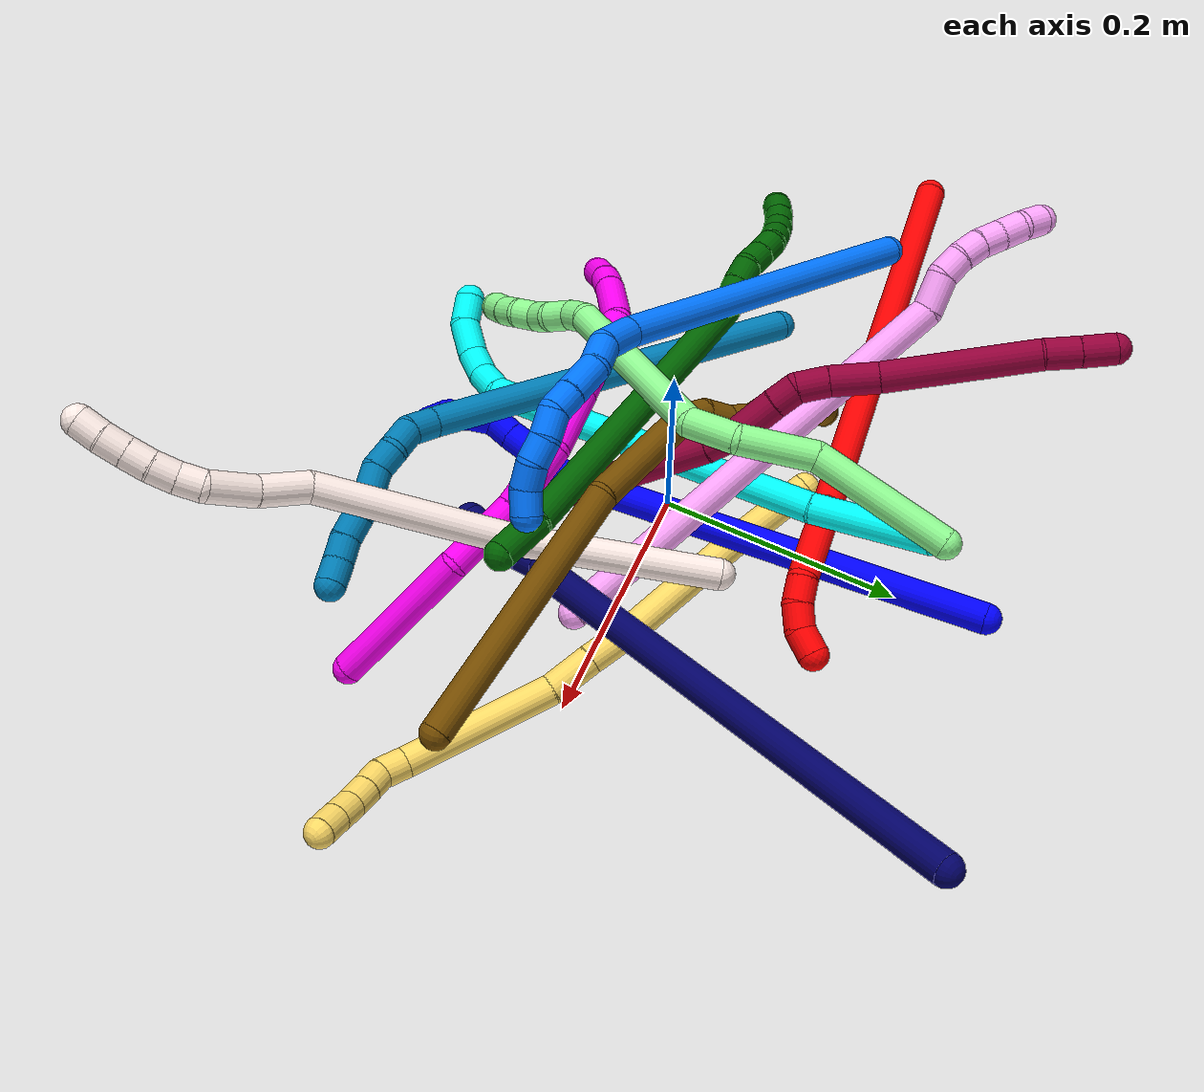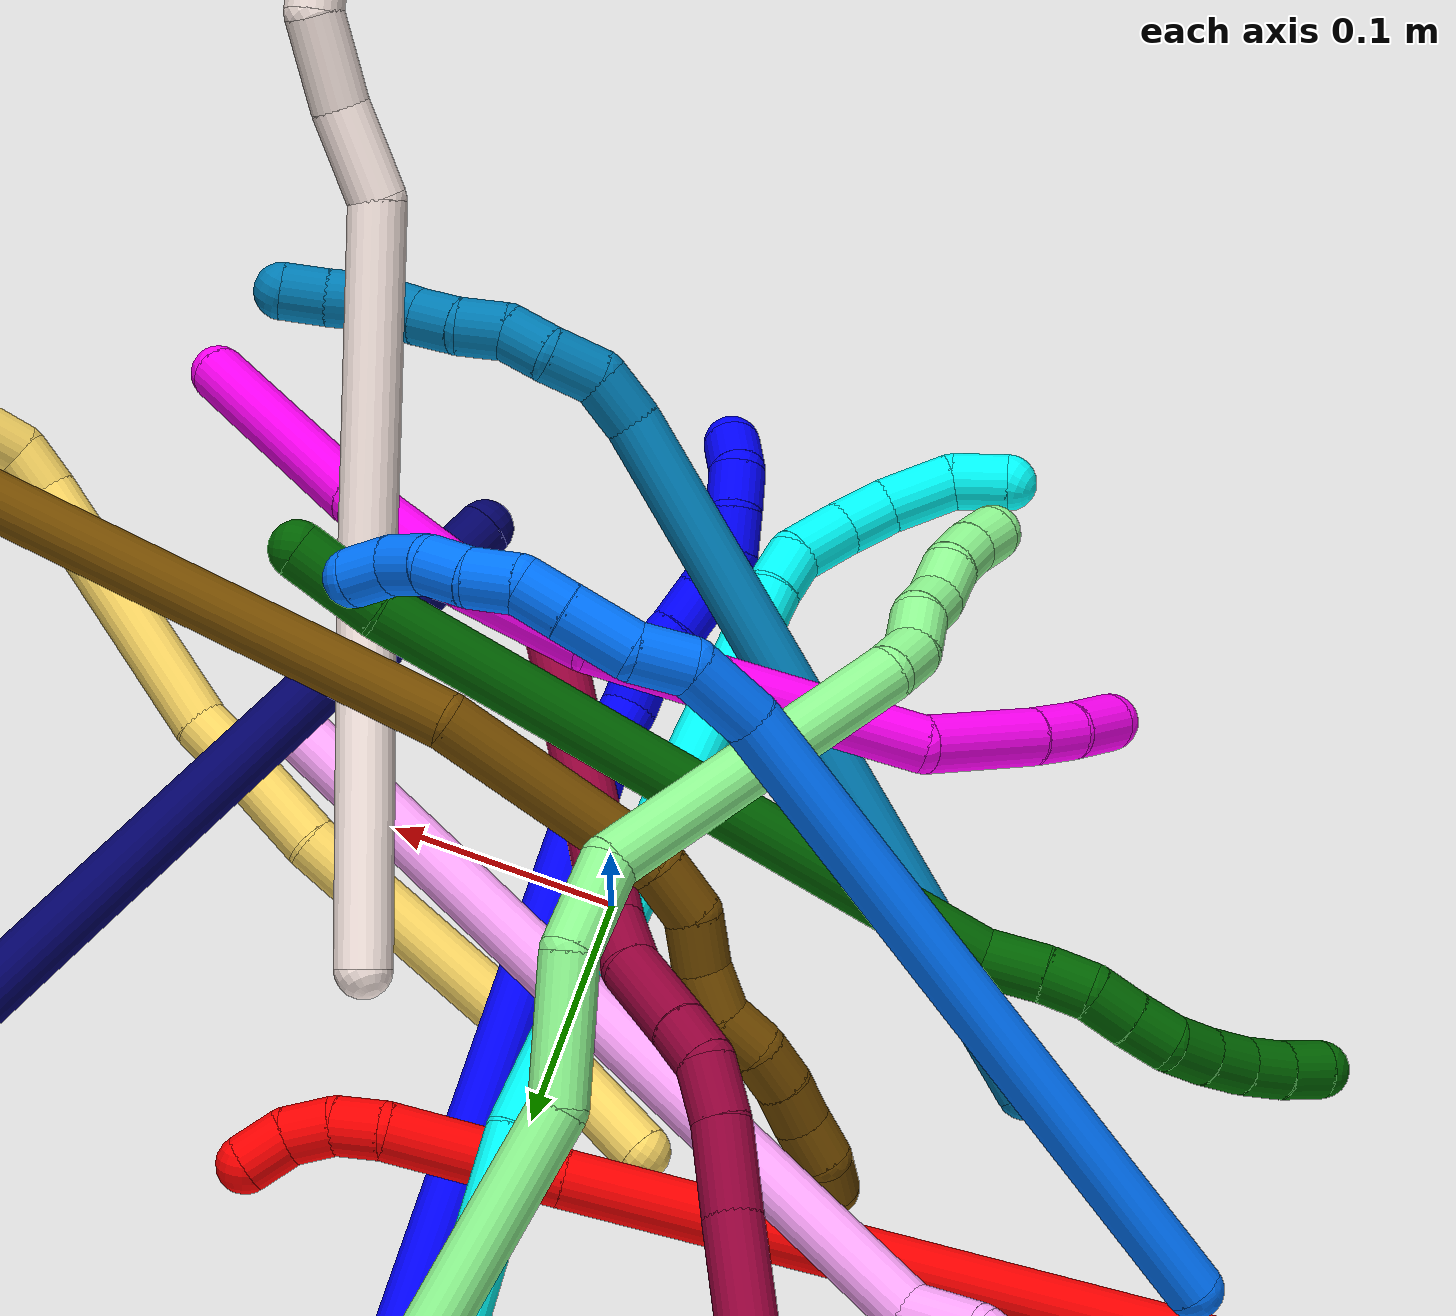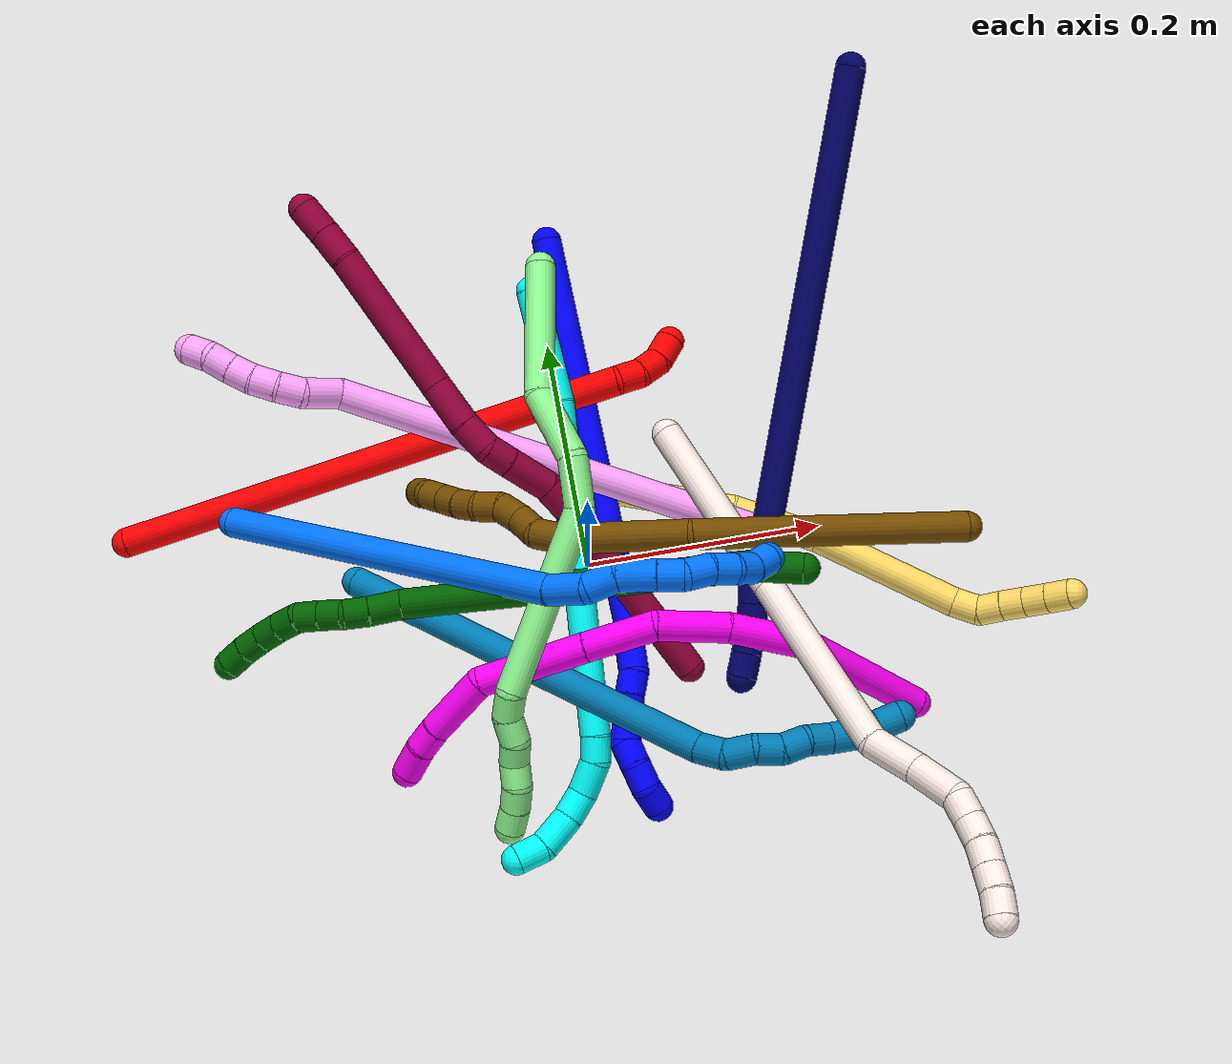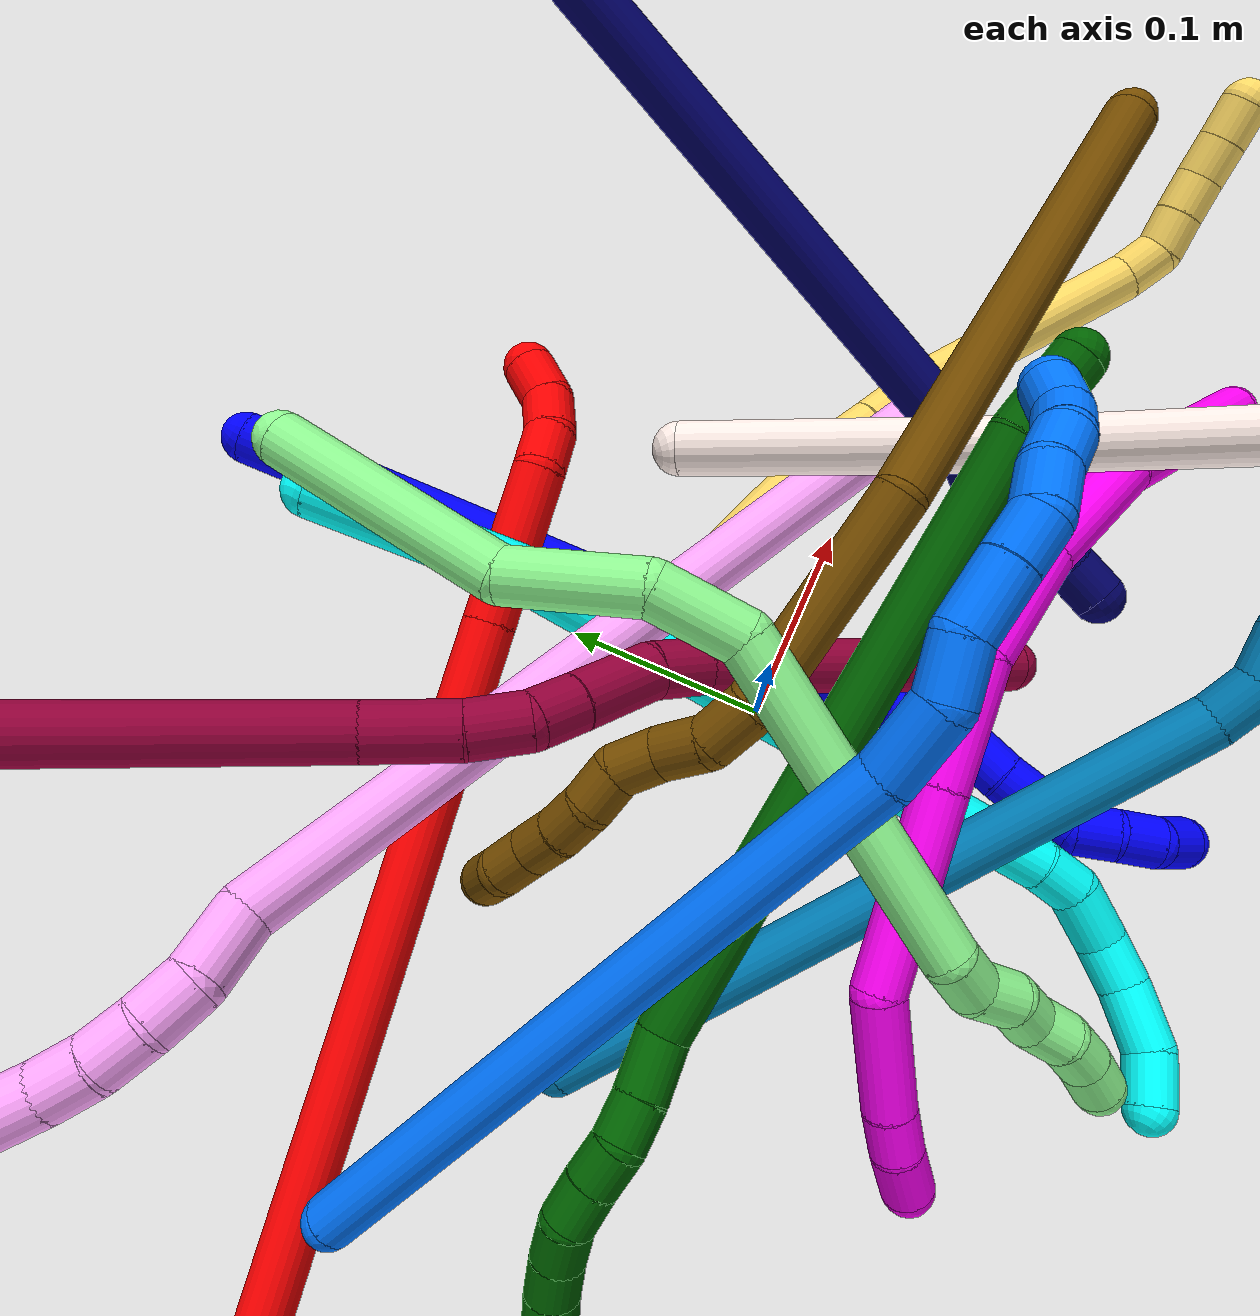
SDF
<sdf version="1.7">
 <world name="default">
  <plugin name="TubeGeneratorPlugin" filename="libtube_generator_plugin.so"/>
  <model name="photoneo_s_sensor">
   <static>1</static>
   <pose>0 0 2 1.57079 1.57079 3.14159</pose>
   <link name="link">
    <inertial><mass>0.1</mass></inertial>
    <sensor name="sensor" type="depth">
     <update_rate>30</update_rate>
     <camera>
      <horizontal_fov>1.22</horizontal_fov>
      <image><width>1920</width><height>1200</height><format>B8G8R8</format></image>
      <clip><near>0.1</near><far>4</far></clip>
      <depth_camera><output>points</output></depth_camera>
     </camera>
     <plugin name="camera_plugin" filename="libgazebo_ros_depth_camera.so">
      <baseline>0.2</baseline>
      <alwaysOn>1</alwaysOn>
      <updateRate>0.0</updateRate>
      <cameraName>camera_ir</cameraName>
      <imageTopicName>/camera/color/image_raw</imageTopicName>
      <cameraInfoTopicName>/camera/color/camera_info</cameraInfoTopicName>
      <depthImageTopicName>/camera/depth/image_raw</depthImageTopicName>
      <depthImageCameraInfoTopicName>/camera/depth/camera_info</depthImageCameraInfoTopicName>
      <pointCloudTopicName>/camera/depth/points</pointCloudTopicName>
      <frameName>fr_optical</frameName>
      <pointCloudCutoff>0.1</pointCloudCutoff>
      <pointCloudCutoffMax>2.0</pointCloudCutoffMax>
      <distortionK1>0</distortionK1>
      <distortionK2>0</distortionK2>
      <distortionK3>0</distortionK3>
      <distortionT1>0</distortionT1>
      <distortionT2>0</distortionT2>
      <CxPrime>0</CxPrime>
      <Cx>0</Cx>
      <Cy>0</Cy>
      <focalLength>0</focalLength>
      <hackBaseline>0</hackBaseline>
     </plugin>
    </sensor>
   </link>
  </model>
  <gravity>0 0 -9.8</gravity>
  <magnetic_field>6e-06 2.3e-05 -4.2e-05</magnetic_field>
  <atmosphere type="adiabatic"/>
  <physics name="default_physics" default="0" type="ode">
   <max_step_size>0.003</max_step_size>
   <real_time_factor>1</real_time_factor>
   <real_time_update_rate>1000</real_time_update_rate>
   <max_contacts>10000</max_contacts>
   <ode>
    <solver>
     <type>quick</type>
     <iters>100</iters>
     <sor>1.3</sor>
     <use_dynamic_moi_rescaling>0</use_dynamic_moi_rescaling>
    </solver>
    <constraints>
     <contact_max_correcting_vel>0</contact_max_correcting_vel>
     <contact_surface_layer>0.001</contact_surface_layer>
     <cfm>0</cfm>
     <erp>0.2</erp>
    </constraints>
   </ode>
  </physics>
  <scene><ambient>0.4 0.4 0.4 1</ambient><background>0.7 0.7 0.7 1</background><shadows>0</shadows></scene>
  <audio><device>default</device></audio>
  <spherical_coordinates>
   <surface_model>EARTH_WGS84</surface_model>
   <latitude_deg>0</latitude_deg>
   <longitude_deg>0</longitude_deg>
   <elevation>0</elevation>
   <heading_deg>0</heading_deg>
  </spherical_coordinates>
  <model name="bin">
   <static>1</static>
   <link name="bottom">
    <collision name="collision-bottom">
     <pose>0 0 -0.01 0 -0 0</pose>
     <geometry><box><size>0.8 0.6 0.02</size></box></geometry>
     <surface>
      <friction><ode><mu>100</mu><mu2>100</mu2></ode></friction>
      <contact><collide_bitmask>65535</collide_bitmask></contact>
     </surface>
    </collision>
   </link>
   <link name="west_wall">
    <collision name="collision-west_wall">
     <pose>-0.41 0 0.1 0 -0 0</pose>
     <geometry><box><size>0.02 0.6 0.2</size></box></geometry>
     <surface>
      <friction><ode><mu>100</mu><mu2>100</mu2></ode></friction>
      <contact><collide_bitmask>65535</collide_bitmask></contact>
     </surface>
    </collision>
   </link>
   <link name="east_wall">
    <collision name="collision-east_wall">
     <pose>0.41 0 0.1 0 -0 0</pose>
     <geometry><box><size>0.02 0.6 0.2</size></box></geometry>
     <surface>
      <friction><ode><mu>100</mu><mu2>100</mu2></ode></friction>
      <contact><collide_bitmask>65535</collide_bitmask></contact>
     </surface>
    </collision>
   </link>
   <link name="south_wall">
    <collision name="collision-south_wall">
     <pose>0 -0.31 0.1 0 -0 0</pose>
     <geometry><box><size>0.8 0.02 0.2</size></box></geometry>
     <surface>
      <friction><ode><mu>100</mu><mu2>100</mu2></ode></friction>
      <contact><collide_bitmask>65535</collide_bitmask></contact>
     </surface>
    </collision>
   </link>
   <link name="north_wall">
    <collision name="collision-north_wall">
     <pose>0 0.31 0.1 0 -0 0</pose>
     <geometry><box><size>0.8 0.02 0.2</size></box></geometry>
     <surface>
      <friction><ode><mu>100</mu><mu2>100</mu2></ode></friction>
      <contact><collide_bitmask>65535</collide_bitmask></contact>
     </surface>
    </collision>
   </link>
  </model>
  <model name="1">
   <static>0</static>
   <link name="1">
    <collision name="collision-cylinder-e_1_1_4">
     <pose>-0.052594 -0.041779 -0.155165 2.87858 -0.31631 -1.75683</pose>
     <geometry><cylinder><radius>0.0125</radius><length>0.338159</length></cylinder></geometry>
     <surface>
      <friction><ode><mu>1.16</mu><mu2>1.16</mu2><slip1>0</slip1><slip2>0</slip2></ode></friction>
      <contact><ode><kp>1e+06</kp><kd>1</kd><max_vel>0</max_vel><min_depth>0.001</min_depth></ode></contact>
     </surface>
    </collision>
    <visual name="visual-cylinder-e_1_1_4">
     <pose>-0.052594 -0.041779 -0.155165 2.87858 -0.31631 -1.75683</pose>
     <geometry><cylinder><radius>0.0125</radius><length>0.338159</length></cylinder></geometry>
     <material><ambient>0 0 1 1</ambient></material>
    </visual>
    <collision name="collision-cylinder-e_2_4_5">
     <pose>-0.107615 -0.083691 -0.320218 3.12805 -0.240643 -3.02969</pose>
     <geometry><cylinder><radius>0.0125</radius><length>0.020364</length></cylinder></geometry>
     <surface>
      <friction><ode><mu>1.16</mu><mu2>1.16</mu2><slip1>0</slip1><slip2>0</slip2></ode></friction>
      <contact><ode><kp>1e+06</kp><kd>1</kd><max_vel>0</max_vel><min_depth>0.001</min_depth></ode></contact>
     </surface>
    </collision>
    <visual name="visual-cylinder-e_2_4_5">
     <pose>-0.107615 -0.083691 -0.320218 3.12805 -0.240643 -3.02969</pose>
     <geometry><cylinder><radius>0.0125</radius><length>0.020364</length></cylinder></geometry>
     <material><ambient>0 0 1 1</ambient></material>
    </visual>
    <collision name="collision-cylinder-e_3_5_6">
     <pose>-0.115919 -0.087348 -0.338239 2.73283 -0.585515 -1.93678</pose>
     <geometry><cylinder><radius>0.0125</radius><length>0.021269</length></cylinder></geometry>
     <surface>
      <friction><ode><mu>1.16</mu><mu2>1.16</mu2><slip1>0</slip1><slip2>0</slip2></ode></friction>
      <contact><ode><kp>1e+06</kp><kd>1</kd><max_vel>0</max_vel><min_depth>0.001</min_depth></ode></contact>
     </surface>
    </collision>
    <visual name="visual-cylinder-e_3_5_6">
     <pose>-0.115919 -0.087348 -0.338239 2.73283 -0.585515 -1.93678</pose>
     <geometry><cylinder><radius>0.0125</radius><length>0.021269</length></cylinder></geometry>
     <material><ambient>0 0 1 1</ambient></material>
    </visual>
    <collision name="collision-cylinder-e_4_6_7">
     <pose>-0.12784 -0.090642 -0.354376 -3.11301 -0.646593 3.05632</pose>
     <geometry><cylinder><radius>0.0125</radius><length>0.020066</length></cylinder></geometry>
     <surface>
      <friction><ode><mu>1.16</mu><mu2>1.16</mu2><slip1>0</slip1><slip2>0</slip2></ode></friction>
      <contact><ode><kp>1e+06</kp><kd>1</kd><max_vel>0</max_vel><min_depth>0.001</min_depth></ode></contact>
     </surface>
    </collision>
    <visual name="visual-cylinder-e_4_6_7">
     <pose>-0.12784 -0.090642 -0.354376 -3.11301 -0.646593 3.05632</pose>
     <geometry><cylinder><radius>0.0125</radius><length>0.020066</length></cylinder></geometry>
     <material><ambient>0 0 1 1</ambient></material>
    </visual>
    <collision name="collision-cylinder-e_5_7_8">
     <pose>-0.139019 -0.090794 -0.37097 3.09725 -0.538369 -2.98118</pose>
     <geometry><cylinder><radius>0.0125</radius><length>0.020027</length></cylinder></geometry>
     <surface>
      <friction><ode><mu>1.16</mu><mu2>1.16</mu2><slip1>0</slip1><slip2>0</slip2></ode></friction>
      <contact><ode><kp>1e+06</kp><kd>1</kd><max_vel>0</max_vel><min_depth>0.001</min_depth></ode></contact>
     </surface>
    </collision>
    <visual name="visual-cylinder-e_5_7_8">
     <pose>-0.139019 -0.090794 -0.37097 3.09725 -0.538369 -2.98118</pose>
     <geometry><cylinder><radius>0.0125</radius><length>0.020027</length></cylinder></geometry>
     <material><ambient>0 0 1 1</ambient></material>
    </visual>
    <collision name="collision-cylinder-e_6_8_9">
     <pose>-0.150489 -0.092326 -0.387231 2.99268 -0.684752 -2.72898</pose>
     <geometry><cylinder><radius>0.0125</radius><length>0.020033</length></cylinder></geometry>
     <surface>
      <friction><ode><mu>1.16</mu><mu2>1.16</mu2><slip1>0</slip1><slip2>0</slip2></ode></friction>
      <contact><ode><kp>1e+06</kp><kd>1</kd><max_vel>0</max_vel><min_depth>0.001</min_depth></ode></contact>
     </surface>
    </collision>
    <visual name="visual-cylinder-e_6_8_9">
     <pose>-0.150489 -0.092326 -0.387231 2.99268 -0.684752 -2.72898</pose>
     <geometry><cylinder><radius>0.0125</radius><length>0.020033</length></cylinder></geometry>
     <material><ambient>0 0 1 1</ambient></material>
    </visual>
    <collision name="collision-cylinder-e_7_9_10">
     <pose>-0.159763 -0.09847 -0.4031 2.59452 -0.297143 -0.980125</pose>
     <geometry><cylinder><radius>0.0125</radius><length>0.020073</length></cylinder></geometry>
     <surface>
      <friction><ode><mu>1.16</mu><mu2>1.16</mu2><slip1>0</slip1><slip2>0</slip2></ode></friction>
      <contact><ode><kp>1e+06</kp><kd>1</kd><max_vel>0</max_vel><min_depth>0.001</min_depth></ode></contact>
     </surface>
    </collision>
    <visual name="visual-cylinder-e_7_9_10">
     <pose>-0.159763 -0.09847 -0.4031 2.59452 -0.297143 -0.980125</pose>
     <geometry><cylinder><radius>0.0125</radius><length>0.020073</length></cylinder></geometry>
     <material><ambient>0 0 1 1</ambient></material>
    </visual>
    <collision name="collision-cylinder-e_8_10_11">
     <pose>-0.163751 -0.107248 -0.420495 2.75112 -0.105118 -0.520004</pose>
     <geometry><cylinder><radius>0.0125</radius><length>0.020006</length></cylinder></geometry>
     <surface>
      <friction><ode><mu>1.16</mu><mu2>1.16</mu2><slip1>0</slip1><slip2>0</slip2></ode></friction>
      <contact><ode><kp>1e+06</kp><kd>1</kd><max_vel>0</max_vel><min_depth>0.001</min_depth></ode></contact>
     </surface>
    </collision>
    <visual name="visual-cylinder-e_8_10_11">
     <pose>-0.163751 -0.107248 -0.420495 2.75112 -0.105118 -0.520004</pose>
     <geometry><cylinder><radius>0.0125</radius><length>0.020006</length></cylinder></geometry>
     <material><ambient>0 0 1 1</ambient></material>
    </visual>
    <collision name="collision-cylinder-e_9_11_2">
     <pose>-0.161542 -0.113195 -0.438899 2.91104 0.33182 1.9316</pose>
     <geometry><cylinder><radius>0.0125</radius><length>0.020002</length></cylinder></geometry>
     <surface>
      <friction><ode><mu>1.16</mu><mu2>1.16</mu2><slip1>0</slip1><slip2>0</slip2></ode></friction>
      <contact><ode><kp>1e+06</kp><kd>1</kd><max_vel>0</max_vel><min_depth>0.001</min_depth></ode></contact>
     </surface>
    </collision>
    <visual name="visual-cylinder-e_9_11_2">
     <pose>-0.161542 -0.113195 -0.438899 2.91104 0.33182 1.9316</pose>
     <geometry><cylinder><radius>0.0125</radius><length>0.020002</length></cylinder></geometry>
     <material><ambient>0 0 1 1</ambient></material>
    </visual>
    <collision name="collision-sphere-2">
     <pose>-0.158284 -0.115356 -0.448105 0 -0 0</pose>
     <geometry><sphere><radius>0.0125</radius></sphere></geometry>
     <surface>
      <friction><ode><mu>1.16</mu><mu2>1.16</mu2><slip1>0</slip1><slip2>0</slip2></ode></friction>
      <contact><ode><kp>1e+06</kp><kd>1</kd><max_vel>0</max_vel><min_depth>0.001</min_depth></ode></contact>
     </surface>
    </collision>
    <visual name="visual-sphere-2">
     <pose>-0.158284 -0.115356 -0.448105 0 -0 0</pose>
     <geometry><sphere><radius>0.0125</radius></sphere></geometry>
     <material><ambient>0 0 1 1</ambient></material>
    </visual>
    <collision name="collision-sphere-11">
     <pose>-0.1648 -0.111035 -0.429694 0 -0 0</pose>
     <geometry><sphere><radius>0.0125</radius></sphere></geometry>
     <surface>
      <friction><ode><mu>1.16</mu><mu2>1.16</mu2><slip1>0</slip1><slip2>0</slip2></ode></friction>
      <contact><ode><kp>1e+06</kp><kd>1</kd><max_vel>0</max_vel><min_depth>0.001</min_depth></ode></contact>
     </surface>
    </collision>
    <visual name="visual-sphere-11">
     <pose>-0.1648 -0.111035 -0.429694 0 -0 0</pose>
     <geometry><sphere><radius>0.0125</radius></sphere></geometry>
     <material><ambient>0 0 1 1</ambient></material>
    </visual>
    <collision name="collision-sphere-10">
     <pose>-0.162701 -0.103462 -0.411296 0 -0 0</pose>
     <geometry><sphere><radius>0.0125</radius></sphere></geometry>
     <surface>
      <friction><ode><mu>1.16</mu><mu2>1.16</mu2><slip1>0</slip1><slip2>0</slip2></ode></friction>
      <contact><ode><kp>1e+06</kp><kd>1</kd><max_vel>0</max_vel><min_depth>0.001</min_depth></ode></contact>
     </surface>
    </collision>
    <visual name="visual-sphere-10">
     <pose>-0.162701 -0.103462 -0.411296 0 -0 0</pose>
     <geometry><sphere><radius>0.0125</radius></sphere></geometry>
     <material><ambient>0 0 1 1</ambient></material>
    </visual>
    <collision name="collision-sphere-9">
     <pose>-0.156824 -0.093477 -0.394903 0 -0 0</pose>
     <geometry><sphere><radius>0.0125</radius></sphere></geometry>
     <surface>
      <friction><ode><mu>1.16</mu><mu2>1.16</mu2><slip1>0</slip1><slip2>0</slip2></ode></friction>
      <contact><ode><kp>1e+06</kp><kd>1</kd><max_vel>0</max_vel><min_depth>0.001</min_depth></ode></contact>
     </surface>
    </collision>
    <visual name="visual-sphere-9">
     <pose>-0.156824 -0.093477 -0.394903 0 -0 0</pose>
     <geometry><sphere><radius>0.0125</radius></sphere></geometry>
     <material><ambient>0 0 1 1</ambient></material>
    </visual>
    <collision name="collision-sphere-4">
     <pose>-0.105188 -0.083557 -0.31033 0 -0 0</pose>
     <geometry><sphere><radius>0.0125</radius></sphere></geometry>
     <surface>
      <friction><ode><mu>1.16</mu><mu2>1.16</mu2><slip1>0</slip1><slip2>0</slip2></ode></friction>
      <contact><ode><kp>1e+06</kp><kd>1</kd><max_vel>0</max_vel><min_depth>0.001</min_depth></ode></contact>
     </surface>
    </collision>
    <visual name="visual-sphere-4">
     <pose>-0.105188 -0.083557 -0.31033 0 -0 0</pose>
     <geometry><sphere><radius>0.0125</radius></sphere></geometry>
     <material><ambient>0 0 1 1</ambient></material>
    </visual>
    <collision name="collision-sphere-1">
     <geometry><sphere><radius>0.0125</radius></sphere></geometry>
     <surface>
      <friction><ode><mu>1.16</mu><mu2>1.16</mu2><slip1>0</slip1><slip2>0</slip2></ode></friction>
      <contact><ode><kp>1e+06</kp><kd>1</kd><max_vel>0</max_vel><min_depth>0.001</min_depth></ode></contact>
     </surface>
    </collision>
    <visual name="visual-sphere-1">
     <geometry><sphere><radius>0.0125</radius></sphere></geometry>
     <material><ambient>0 0 1 1</ambient></material>
    </visual>
    <collision name="collision-sphere-8">
     <pose>-0.144154 -0.091175 -0.379558 0 -0 0</pose>
     <geometry><sphere><radius>0.0125</radius></sphere></geometry>
     <surface>
      <friction><ode><mu>1.16</mu><mu2>1.16</mu2><slip1>0</slip1><slip2>0</slip2></ode></friction>
      <contact><ode><kp>1e+06</kp><kd>1</kd><max_vel>0</max_vel><min_depth>0.001</min_depth></ode></contact>
     </surface>
    </collision>
    <visual name="visual-sphere-8">
     <pose>-0.144154 -0.091175 -0.379558 0 -0 0</pose>
     <geometry><sphere><radius>0.0125</radius></sphere></geometry>
     <material><ambient>0 0 1 1</ambient></material>
    </visual>
    <collision name="collision-sphere-5">
     <pose>-0.110042 -0.083825 -0.330106 0 -0 0</pose>
     <geometry><sphere><radius>0.0125</radius></sphere></geometry>
     <surface>
      <friction><ode><mu>1.16</mu><mu2>1.16</mu2><slip1>0</slip1><slip2>0</slip2></ode></friction>
      <contact><ode><kp>1e+06</kp><kd>1</kd><max_vel>0</max_vel><min_depth>0.001</min_depth></ode></contact>
     </surface>
    </collision>
    <visual name="visual-sphere-5">
     <pose>-0.110042 -0.083825 -0.330106 0 -0 0</pose>
     <geometry><sphere><radius>0.0125</radius></sphere></geometry>
     <material><ambient>0 0 1 1</ambient></material>
    </visual>
    <collision name="collision-sphere-6">
     <pose>-0.121796 -0.090871 -0.346372 0 -0 0</pose>
     <geometry><sphere><radius>0.0125</radius></sphere></geometry>
     <surface>
      <friction><ode><mu>1.16</mu><mu2>1.16</mu2><slip1>0</slip1><slip2>0</slip2></ode></friction>
      <contact><ode><kp>1e+06</kp><kd>1</kd><max_vel>0</max_vel><min_depth>0.001</min_depth></ode></contact>
     </surface>
    </collision>
    <visual name="visual-sphere-6">
     <pose>-0.121796 -0.090871 -0.346372 0 -0 0</pose>
     <geometry><sphere><radius>0.0125</radius></sphere></geometry>
     <material><ambient>0 0 1 1</ambient></material>
    </visual>
    <collision name="collision-sphere-7">
     <pose>-0.133885 -0.090413 -0.362381 0 -0 0</pose>
     <geometry><sphere><radius>0.0125</radius></sphere></geometry>
     <surface>
      <friction><ode><mu>1.16</mu><mu2>1.16</mu2><slip1>0</slip1><slip2>0</slip2></ode></friction>
      <contact><ode><kp>1e+06</kp><kd>1</kd><max_vel>0</max_vel><min_depth>0.001</min_depth></ode></contact>
     </surface>
    </collision>
    <visual name="visual-sphere-7">
     <pose>-0.133885 -0.090413 -0.362381 0 -0 0</pose>
     <geometry><sphere><radius>0.0125</radius></sphere></geometry>
     <material><ambient>0 0 1 1</ambient></material>
    </visual>
    <inertial>
     <pose>-0.081041 -0.059126 -0.227533 0 -0 0</pose>
     <mass>0.5</mass>
     <inertia>
      <ixx>-0.00361</ixx>
      <ixy>0</ixy>
      <ixz>0</ixz>
      <iyy>-0.002193</iyy>
      <iyz>0</iyz>
      <izz>0.001777</izz>
     </inertia>
    </inertial>
   </link>
   <pose>0.013236 0.275223 0.055421 -0.825157 0.786271 0.595279</pose>
  </model>
  <model name="2">
   <static>0</static>
   <link name="2">
    <collision name="collision-cylinder-e_1_1_4">
     <pose>0.142845 0.104999 0.035398 -1.24563 0.911049 -0.676593</pose>
     <geometry><cylinder><radius>0.0125</radius><length>0.361566</length></cylinder></geometry>
     <surface>
      <friction><ode><mu>1.16</mu><mu2>1.16</mu2><slip1>0</slip1><slip2>0</slip2></ode></friction>
      <contact><ode><kp>1e+06</kp><kd>1</kd><max_vel>0</max_vel><min_depth>0.001</min_depth></ode></contact>
     </surface>
    </collision>
    <visual name="visual-cylinder-e_1_1_4">
     <pose>0.142845 0.104999 0.035398 -1.24563 0.911049 -0.676593</pose>
     <geometry><cylinder><radius>0.0125</radius><length>0.361566</length></cylinder></geometry>
     <material><ambient>1 0 0 1</ambient></material>
    </visual>
    <collision name="collision-cylinder-e_2_4_5">
     <pose>0.315069 0.232232 0.078776 -1.22625 0.893564 -0.650235</pose>
     <geometry><cylinder><radius>0.0125</radius><length>0.075396</length></cylinder></geometry>
     <surface>
      <friction><ode><mu>1.16</mu><mu2>1.16</mu2><slip1>0</slip1><slip2>0</slip2></ode></friction>
      <contact><ode><kp>1e+06</kp><kd>1</kd><max_vel>0</max_vel><min_depth>0.001</min_depth></ode></contact>
     </surface>
    </collision>
    <visual name="visual-cylinder-e_2_4_5">
     <pose>0.315069 0.232232 0.078776 -1.22625 0.893564 -0.650235</pose>
     <geometry><cylinder><radius>0.0125</radius><length>0.075396</length></cylinder></geometry>
     <material><ambient>1 0 0 1</ambient></material>
    </visual>
    <collision name="collision-cylinder-e_3_5_6">
     <pose>0.353996 0.258674 0.08609 -1.72761 1.15119 -1.29916</pose>
     <geometry><cylinder><radius>0.0125</radius><length>0.020911</length></cylinder></geometry>
     <surface>
      <friction><ode><mu>1.16</mu><mu2>1.16</mu2><slip1>0</slip1><slip2>0</slip2></ode></friction>
      <contact><ode><kp>1e+06</kp><kd>1</kd><max_vel>0</max_vel><min_depth>0.001</min_depth></ode></contact>
     </surface>
    </collision>
    <visual name="visual-cylinder-e_3_5_6">
     <pose>0.353996 0.258674 0.08609 -1.72761 1.15119 -1.29916</pose>
     <geometry><cylinder><radius>0.0125</radius><length>0.020911</length></cylinder></geometry>
     <material><ambient>1 0 0 1</ambient></material>
    </visual>
    <collision name="collision-cylinder-e_4_6_7">
     <pose>0.372007 0.267823 0.081755 -2.20955 0.9419 -1.58303</pose>
     <geometry><cylinder><radius>0.0125</radius><length>0.020928</length></cylinder></geometry>
     <surface>
      <friction><ode><mu>1.16</mu><mu2>1.16</mu2><slip1>0</slip1><slip2>0</slip2></ode></friction>
      <contact><ode><kp>1e+06</kp><kd>1</kd><max_vel>0</max_vel><min_depth>0.001</min_depth></ode></contact>
     </surface>
    </collision>
    <visual name="visual-cylinder-e_4_6_7">
     <pose>0.372007 0.267823 0.081755 -2.20955 0.9419 -1.58303</pose>
     <geometry><cylinder><radius>0.0125</radius><length>0.020928</length></cylinder></geometry>
     <material><ambient>1 0 0 1</ambient></material>
    </visual>
    <collision name="collision-cylinder-e_5_7_2">
     <pose>0.386103 0.27935 0.071982 -2.31824 0.560413 -1.16548</pose>
     <geometry><cylinder><radius>0.0125</radius><length>0.021198</length></cylinder></geometry>
     <surface>
      <friction><ode><mu>1.16</mu><mu2>1.16</mu2><slip1>0</slip1><slip2>0</slip2></ode></friction>
      <contact><ode><kp>1e+06</kp><kd>1</kd><max_vel>0</max_vel><min_depth>0.001</min_depth></ode></contact>
     </surface>
    </collision>
    <visual name="visual-cylinder-e_5_7_2">
     <pose>0.386103 0.27935 0.071982 -2.31824 0.560413 -1.16548</pose>
     <geometry><cylinder><radius>0.0125</radius><length>0.021198</length></cylinder></geometry>
     <material><ambient>1 0 0 1</ambient></material>
    </visual>
    <collision name="collision-sphere-2">
     <pose>0.391736 0.285934 0.065879 0 -0 0</pose>
     <geometry><sphere><radius>0.0125</radius></sphere></geometry>
     <surface>
      <friction><ode><mu>1.16</mu><mu2>1.16</mu2><slip1>0</slip1><slip2>0</slip2></ode></friction>
      <contact><ode><kp>1e+06</kp><kd>1</kd><max_vel>0</max_vel><min_depth>0.001</min_depth></ode></contact>
     </surface>
    </collision>
    <visual name="visual-sphere-2">
     <pose>0.391736 0.285934 0.065879 0 -0 0</pose>
     <geometry><sphere><radius>0.0125</radius></sphere></geometry>
     <material><ambient>1 0 0 1</ambient></material>
    </visual>
    <collision name="collision-sphere-7">
     <pose>0.380469 0.272765 0.078085 0 -0 0</pose>
     <geometry><sphere><radius>0.0125</radius></sphere></geometry>
     <surface>
      <friction><ode><mu>1.16</mu><mu2>1.16</mu2><slip1>0</slip1><slip2>0</slip2></ode></friction>
      <contact><ode><kp>1e+06</kp><kd>1</kd><max_vel>0</max_vel><min_depth>0.001</min_depth></ode></contact>
     </surface>
    </collision>
    <visual name="visual-sphere-7">
     <pose>0.380469 0.272765 0.078085 0 -0 0</pose>
     <geometry><sphere><radius>0.0125</radius></sphere></geometry>
     <material><ambient>1 0 0 1</ambient></material>
    </visual>
    <collision name="collision-sphere-6">
     <pose>0.363544 0.262881 0.085425 0 -0 0</pose>
     <geometry><sphere><radius>0.0125</radius></sphere></geometry>
     <surface>
      <friction><ode><mu>1.16</mu><mu2>1.16</mu2><slip1>0</slip1><slip2>0</slip2></ode></friction>
      <contact><ode><kp>1e+06</kp><kd>1</kd><max_vel>0</max_vel><min_depth>0.001</min_depth></ode></contact>
     </surface>
    </collision>
    <visual name="visual-sphere-6">
     <pose>0.363544 0.262881 0.085425 0 -0 0</pose>
     <geometry><sphere><radius>0.0125</radius></sphere></geometry>
     <material><ambient>1 0 0 1</ambient></material>
    </visual>
    <collision name="collision-sphere-5">
     <pose>0.344447 0.254466 0.086755 0 -0 0</pose>
     <geometry><sphere><radius>0.0125</radius></sphere></geometry>
     <surface>
      <friction><ode><mu>1.16</mu><mu2>1.16</mu2><slip1>0</slip1><slip2>0</slip2></ode></friction>
      <contact><ode><kp>1e+06</kp><kd>1</kd><max_vel>0</max_vel><min_depth>0.001</min_depth></ode></contact>
     </surface>
    </collision>
    <visual name="visual-sphere-5">
     <pose>0.344447 0.254466 0.086755 0 -0 0</pose>
     <geometry><sphere><radius>0.0125</radius></sphere></geometry>
     <material><ambient>1 0 0 1</ambient></material>
    </visual>
    <collision name="collision-sphere-1">
     <geometry><sphere><radius>0.0125</radius></sphere></geometry>
     <surface>
      <friction><ode><mu>1.16</mu><mu2>1.16</mu2><slip1>0</slip1><slip2>0</slip2></ode></friction>
      <contact><ode><kp>1e+06</kp><kd>1</kd><max_vel>0</max_vel><min_depth>0.001</min_depth></ode></contact>
     </surface>
    </collision>
    <visual name="visual-sphere-1">
     <geometry><sphere><radius>0.0125</radius></sphere></geometry>
     <material><ambient>1 0 0 1</ambient></material>
    </visual>
    <collision name="collision-sphere-4">
     <pose>0.28569 0.209997 0.070797 0 -0 0</pose>
     <geometry><sphere><radius>0.0125</radius></sphere></geometry>
     <surface>
      <friction><ode><mu>1.16</mu><mu2>1.16</mu2><slip1>0</slip1><slip2>0</slip2></ode></friction>
      <contact><ode><kp>1e+06</kp><kd>1</kd><max_vel>0</max_vel><min_depth>0.001</min_depth></ode></contact>
     </surface>
    </collision>
    <visual name="visual-sphere-4">
     <pose>0.28569 0.209997 0.070797 0 -0 0</pose>
     <geometry><sphere><radius>0.0125</radius></sphere></geometry>
     <material><ambient>1 0 0 1</ambient></material>
    </visual>
    <inertial>
     <pose>0.197551 0.144819 0.047551 0 -0 0</pose>
     <mass>0.5</mass>
     <inertia>
      <ixx>0.000405</ixx>
      <ixy>0</ixy>
      <ixz>0</ixz>
      <iyy>0.001356</iyy>
      <iyz>0</iyz>
      <izz>-0.005473</izz>
     </inertia>
    </inertial>
   </link>
   <pose>-0.3805 0.085864 0.011494 0.872684 0.487801 -0.111903</pose>
  </model>
  <model name="3">
   <static>0</static>
   <link name="3">
    <collision name="collision-cylinder-e_1_1_4">
     <pose>-0.018914 -0.043402 -0.010927 1.81744 -0.399836 -0.508665</pose>
     <geometry><cylinder><radius>0.0125</radius><length>0.097177</length></cylinder></geometry>
     <surface>
      <friction><ode><mu>1.16</mu><mu2>1.16</mu2><slip1>0</slip1><slip2>0</slip2></ode></friction>
      <contact><ode><kp>1e+06</kp><kd>1</kd><max_vel>0</max_vel><min_depth>0.001</min_depth></ode></contact>
     </surface>
    </collision>
    <visual name="visual-cylinder-e_1_1_4">
     <pose>-0.018914 -0.043402 -0.010927 1.81744 -0.399836 -0.508665</pose>
     <geometry><cylinder><radius>0.0125</radius><length>0.097177</length></cylinder></geometry>
     <material><ambient>0.003922 1 0.996078 1</ambient></material>
    </visual>
    <collision name="collision-cylinder-e_2_4_5">
     <pose>-0.102553 -0.206801 -0.036201 1.68979 -0.491703 -0.551047</pose>
     <geometry><cylinder><radius>0.0125</radius><length>0.274187</length></cylinder></geometry>
     <surface>
      <friction><ode><mu>1.16</mu><mu2>1.16</mu2><slip1>0</slip1><slip2>0</slip2></ode></friction>
      <contact><ode><kp>1e+06</kp><kd>1</kd><max_vel>0</max_vel><min_depth>0.001</min_depth></ode></contact>
     </surface>
    </collision>
    <visual name="visual-cylinder-e_2_4_5">
     <pose>-0.102553 -0.206801 -0.036201 1.68979 -0.491703 -0.551047</pose>
     <geometry><cylinder><radius>0.0125</radius><length>0.274187</length></cylinder></geometry>
     <material><ambient>0.003922 1 0.996078 1</ambient></material>
    </visual>
    <collision name="collision-cylinder-e_3_5_6">
     <pose>-0.173543 -0.335332 -0.050971 1.62048 -0.632583 -0.662559</pose>
     <geometry><cylinder><radius>0.0125</radius><length>0.021189</length></cylinder></geometry>
     <surface>
      <friction><ode><mu>1.16</mu><mu2>1.16</mu2><slip1>0</slip1><slip2>0</slip2></ode></friction>
      <contact><ode><kp>1e+06</kp><kd>1</kd><max_vel>0</max_vel><min_depth>0.001</min_depth></ode></contact>
     </surface>
    </collision>
    <visual name="visual-cylinder-e_3_5_6">
     <pose>-0.173543 -0.335332 -0.050971 1.62048 -0.632583 -0.662559</pose>
     <geometry><cylinder><radius>0.0125</radius><length>0.021189</length></cylinder></geometry>
     <material><ambient>0.003922 1 0.996078 1</ambient></material>
    </visual>
    <collision name="collision-cylinder-e_4_6_7">
     <pose>-0.189865 -0.353164 -0.04697 1.12654 -0.773652 -0.503578</pose>
     <geometry><cylinder><radius>0.0125</radius><length>0.028791</length></cylinder></geometry>
     <surface>
      <friction><ode><mu>1.16</mu><mu2>1.16</mu2><slip1>0</slip1><slip2>0</slip2></ode></friction>
      <contact><ode><kp>1e+06</kp><kd>1</kd><max_vel>0</max_vel><min_depth>0.001</min_depth></ode></contact>
     </surface>
    </collision>
    <visual name="visual-cylinder-e_4_6_7">
     <pose>-0.189865 -0.353164 -0.04697 1.12654 -0.773652 -0.503578</pose>
     <geometry><cylinder><radius>0.0125</radius><length>0.028791</length></cylinder></geometry>
     <material><ambient>0.003922 1 0.996078 1</ambient></material>
    </visual>
    <collision name="collision-cylinder-e_5_7_8">
     <pose>-0.205227 -0.370879 -0.036502 0.948174 -0.473098 -0.246136</pose>
     <geometry><cylinder><radius>0.0125</radius><length>0.023277</length></cylinder></geometry>
     <surface>
      <friction><ode><mu>1.16</mu><mu2>1.16</mu2><slip1>0</slip1><slip2>0</slip2></ode></friction>
      <contact><ode><kp>1e+06</kp><kd>1</kd><max_vel>0</max_vel><min_depth>0.001</min_depth></ode></contact>
     </surface>
    </collision>
    <visual name="visual-cylinder-e_5_7_8">
     <pose>-0.205227 -0.370879 -0.036502 0.948174 -0.473098 -0.246136</pose>
     <geometry><cylinder><radius>0.0125</radius><length>0.023277</length></cylinder></geometry>
     <material><ambient>0.003922 1 0.996078 1</ambient></material>
    </visual>
    <collision name="collision-cylinder-e_6_8_9">
     <pose>-0.215301 -0.389739 -0.020048 0.786898 -0.312853 -0.130746</pose>
     <geometry><cylinder><radius>0.0125</radius><length>0.031002</length></cylinder></geometry>
     <surface>
      <friction><ode><mu>1.16</mu><mu2>1.16</mu2><slip1>0</slip1><slip2>0</slip2></ode></friction>
      <contact><ode><kp>1e+06</kp><kd>1</kd><max_vel>0</max_vel><min_depth>0.001</min_depth></ode></contact>
     </surface>
    </collision>
    <visual name="visual-cylinder-e_6_8_9">
     <pose>-0.215301 -0.389739 -0.020048 0.786898 -0.312853 -0.130746</pose>
     <geometry><cylinder><radius>0.0125</radius><length>0.031002</length></cylinder></geometry>
     <material><ambient>0.003922 1 0.996078 1</ambient></material>
    </visual>
    <collision name="collision-cylinder-e_7_9_2">
     <pose>-0.222685 -0.404415 0.001494 0.363375 -0.216087 -0.039848</pose>
     <geometry><cylinder><radius>0.0125</radius><length>0.024378</length></cylinder></geometry>
     <surface>
      <friction><ode><mu>1.16</mu><mu2>1.16</mu2><slip1>0</slip1><slip2>0</slip2></ode></friction>
      <contact><ode><kp>1e+06</kp><kd>1</kd><max_vel>0</max_vel><min_depth>0.001</min_depth></ode></contact>
     </surface>
    </collision>
    <visual name="visual-cylinder-e_7_9_2">
     <pose>-0.222685 -0.404415 0.001494 0.363375 -0.216087 -0.039848</pose>
     <geometry><cylinder><radius>0.0125</radius><length>0.024378</length></cylinder></geometry>
     <material><ambient>0.003922 1 0.996078 1</ambient></material>
    </visual>
    <collision name="collision-sphere-2">
     <pose>-0.225298 -0.408647 0.012622 0 -0 0</pose>
     <geometry><sphere><radius>0.0125</radius></sphere></geometry>
     <surface>
      <friction><ode><mu>1.16</mu><mu2>1.16</mu2><slip1>0</slip1><slip2>0</slip2></ode></friction>
      <contact><ode><kp>1e+06</kp><kd>1</kd><max_vel>0</max_vel><min_depth>0.001</min_depth></ode></contact>
     </surface>
    </collision>
    <visual name="visual-sphere-2">
     <pose>-0.225298 -0.408647 0.012622 0 -0 0</pose>
     <geometry><sphere><radius>0.0125</radius></sphere></geometry>
     <material><ambient>0.003922 1 0.996078 1</ambient></material>
    </visual>
    <collision name="collision-sphere-9">
     <pose>-0.220072 -0.400183 -0.009635 0 -0 0</pose>
     <geometry><sphere><radius>0.0125</radius></sphere></geometry>
     <surface>
      <friction><ode><mu>1.16</mu><mu2>1.16</mu2><slip1>0</slip1><slip2>0</slip2></ode></friction>
      <contact><ode><kp>1e+06</kp><kd>1</kd><max_vel>0</max_vel><min_depth>0.001</min_depth></ode></contact>
     </surface>
    </collision>
    <visual name="visual-sphere-9">
     <pose>-0.220072 -0.400183 -0.009635 0 -0 0</pose>
     <geometry><sphere><radius>0.0125</radius></sphere></geometry>
     <material><ambient>0.003922 1 0.996078 1</ambient></material>
    </visual>
    <collision name="collision-sphere-4">
     <pose>-0.037828 -0.086803 -0.021854 0 -0 0</pose>
     <geometry><sphere><radius>0.0125</radius></sphere></geometry>
     <surface>
      <friction><ode><mu>1.16</mu><mu2>1.16</mu2><slip1>0</slip1><slip2>0</slip2></ode></friction>
      <contact><ode><kp>1e+06</kp><kd>1</kd><max_vel>0</max_vel><min_depth>0.001</min_depth></ode></contact>
     </surface>
    </collision>
    <visual name="visual-sphere-4">
     <pose>-0.037828 -0.086803 -0.021854 0 -0 0</pose>
     <geometry><sphere><radius>0.0125</radius></sphere></geometry>
     <material><ambient>0.003922 1 0.996078 1</ambient></material>
    </visual>
    <collision name="collision-sphere-1">
     <geometry><sphere><radius>0.0125</radius></sphere></geometry>
     <surface>
      <friction><ode><mu>1.16</mu><mu2>1.16</mu2><slip1>0</slip1><slip2>0</slip2></ode></friction>
      <contact><ode><kp>1e+06</kp><kd>1</kd><max_vel>0</max_vel><min_depth>0.001</min_depth></ode></contact>
     </surface>
    </collision>
    <visual name="visual-sphere-1">
     <geometry><sphere><radius>0.0125</radius></sphere></geometry>
     <material><ambient>0.003922 1 0.996078 1</ambient></material>
    </visual>
    <collision name="collision-sphere-8">
     <pose>-0.21053 -0.379295 -0.030461 0 -0 0</pose>
     <geometry><sphere><radius>0.0125</radius></sphere></geometry>
     <surface>
      <friction><ode><mu>1.16</mu><mu2>1.16</mu2><slip1>0</slip1><slip2>0</slip2></ode></friction>
      <contact><ode><kp>1e+06</kp><kd>1</kd><max_vel>0</max_vel><min_depth>0.001</min_depth></ode></contact>
     </surface>
    </collision>
    <visual name="visual-sphere-8">
     <pose>-0.21053 -0.379295 -0.030461 0 -0 0</pose>
     <geometry><sphere><radius>0.0125</radius></sphere></geometry>
     <material><ambient>0.003922 1 0.996078 1</ambient></material>
    </visual>
    <collision name="collision-sphere-5">
     <pose>-0.167279 -0.326799 -0.050547 0 -0 0</pose>
     <geometry><sphere><radius>0.0125</radius></sphere></geometry>
     <surface>
      <friction><ode><mu>1.16</mu><mu2>1.16</mu2><slip1>0</slip1><slip2>0</slip2></ode></friction>
      <contact><ode><kp>1e+06</kp><kd>1</kd><max_vel>0</max_vel><min_depth>0.001</min_depth></ode></contact>
     </surface>
    </collision>
    <visual name="visual-sphere-5">
     <pose>-0.167279 -0.326799 -0.050547 0 -0 0</pose>
     <geometry><sphere><radius>0.0125</radius></sphere></geometry>
     <material><ambient>0.003922 1 0.996078 1</ambient></material>
    </visual>
    <collision name="collision-sphere-6">
     <pose>-0.179806 -0.343866 -0.051396 0 -0 0</pose>
     <geometry><sphere><radius>0.0125</radius></sphere></geometry>
     <surface>
      <friction><ode><mu>1.16</mu><mu2>1.16</mu2><slip1>0</slip1><slip2>0</slip2></ode></friction>
      <contact><ode><kp>1e+06</kp><kd>1</kd><max_vel>0</max_vel><min_depth>0.001</min_depth></ode></contact>
     </surface>
    </collision>
    <visual name="visual-sphere-6">
     <pose>-0.179806 -0.343866 -0.051396 0 -0 0</pose>
     <geometry><sphere><radius>0.0125</radius></sphere></geometry>
     <material><ambient>0.003922 1 0.996078 1</ambient></material>
    </visual>
    <collision name="collision-sphere-7">
     <pose>-0.199924 -0.362463 -0.042544 0 -0 0</pose>
     <geometry><sphere><radius>0.0125</radius></sphere></geometry>
     <surface>
      <friction><ode><mu>1.16</mu><mu2>1.16</mu2><slip1>0</slip1><slip2>0</slip2></ode></friction>
      <contact><ode><kp>1e+06</kp><kd>1</kd><max_vel>0</max_vel><min_depth>0.001</min_depth></ode></contact>
     </surface>
    </collision>
    <visual name="visual-sphere-7">
     <pose>-0.199924 -0.362463 -0.042544 0 -0 0</pose>
     <geometry><sphere><radius>0.0125</radius></sphere></geometry>
     <material><ambient>0.003922 1 0.996078 1</ambient></material>
    </visual>
    <inertial>
     <pose>-0.111961 -0.217534 -0.029709 0 -0 0</pose>
     <mass>0.5</mass>
     <inertia>
      <ixx>0.000519</ixx>
      <ixy>0</ixy>
      <ixz>0</ixz>
      <iyy>-0.000613</iyy>
      <iyz>0</iyz>
      <izz>0.002447</izz>
     </inertia>
    </inertial>
   </link>
   <pose>-0.009304 0.215425 0.100309 -0.907575 -1.17972 0.817512</pose>
  </model>
  <model name="4">
   <static>0</static>
   <link name="4">
    <collision name="collision-cylinder-e_1_1_4">
     <pose>-0.067481 0.141291 0.096563 -0.971274 -0.375594 0.199933</pose>
     <geometry><cylinder><radius>0.0125</radius><length>0.367921</length></cylinder></geometry>
     <surface>
      <friction><ode><mu>1.16</mu><mu2>1.16</mu2><slip1>0</slip1><slip2>0</slip2></ode></friction>
      <contact><ode><kp>1e+06</kp><kd>1</kd><max_vel>0</max_vel><min_depth>0.001</min_depth></ode></contact>
     </surface>
    </collision>
    <visual name="visual-cylinder-e_1_1_4">
     <pose>-0.067481 0.141291 0.096563 -0.971274 -0.375594 0.199933</pose>
     <geometry><cylinder><radius>0.0125</radius><length>0.367921</length></cylinder></geometry>
     <material><ambient>1 0.65098 0.996078 1</ambient></material>
    </visual>
    <collision name="collision-cylinder-e_2_4_5">
     <pose>-0.13468 0.292291 0.204896 -0.689724 0.018542 -0.006661</pose>
     <geometry><cylinder><radius>0.0125</radius><length>0.030519</length></cylinder></geometry>
     <surface>
      <friction><ode><mu>1.16</mu><mu2>1.16</mu2><slip1>0</slip1><slip2>0</slip2></ode></friction>
      <contact><ode><kp>1e+06</kp><kd>1</kd><max_vel>0</max_vel><min_depth>0.001</min_depth></ode></contact>
     </surface>
    </collision>
    <visual name="visual-cylinder-e_2_4_5">
     <pose>-0.13468 0.292291 0.204896 -0.689724 0.018542 -0.006661</pose>
     <geometry><cylinder><radius>0.0125</radius><length>0.030519</length></cylinder></geometry>
     <material><ambient>1 0.65098 0.996078 1</ambient></material>
    </visual>
    <collision name="collision-cylinder-e_3_5_6">
     <pose>-0.13774 0.309759 0.22296 -0.889284 -0.32286 0.154871</pose>
     <geometry><cylinder><radius>0.0125</radius><length>0.021073</length></cylinder></geometry>
     <surface>
      <friction><ode><mu>1.16</mu><mu2>1.16</mu2><slip1>0</slip1><slip2>0</slip2></ode></friction>
      <contact><ode><kp>1e+06</kp><kd>1</kd><max_vel>0</max_vel><min_depth>0.001</min_depth></ode></contact>
     </surface>
    </collision>
    <visual name="visual-cylinder-e_3_5_6">
     <pose>-0.13774 0.309759 0.22296 -0.889284 -0.32286 0.154871</pose>
     <geometry><cylinder><radius>0.0125</radius><length>0.021073</length></cylinder></geometry>
     <material><ambient>1 0.65098 0.996078 1</ambient></material>
    </visual>
    <collision name="collision-cylinder-e_4_6_7">
     <pose>-0.146504 0.324524 0.234344 -0.942511 -0.559465 0.290685</pose>
     <geometry><cylinder><radius>0.0125</radius><length>0.02043</length></cylinder></geometry>
     <surface>
      <friction><ode><mu>1.16</mu><mu2>1.16</mu2><slip1>0</slip1><slip2>0</slip2></ode></friction>
      <contact><ode><kp>1e+06</kp><kd>1</kd><max_vel>0</max_vel><min_depth>0.001</min_depth></ode></contact>
     </surface>
    </collision>
    <visual name="visual-cylinder-e_4_6_7">
     <pose>-0.146504 0.324524 0.234344 -0.942511 -0.559465 0.290685</pose>
     <geometry><cylinder><radius>0.0125</radius><length>0.02043</length></cylinder></geometry>
     <material><ambient>1 0.65098 0.996078 1</ambient></material>
    </visual>
    <collision name="collision-cylinder-e_5_7_8">
     <pose>-0.15821 0.338538 0.242812 -1.12159 -0.679365 0.436806</pose>
     <geometry><cylinder><radius>0.0125</radius><length>0.020005</length></cylinder></geometry>
     <surface>
      <friction><ode><mu>1.16</mu><mu2>1.16</mu2><slip1>0</slip1><slip2>0</slip2></ode></friction>
      <contact><ode><kp>1e+06</kp><kd>1</kd><max_vel>0</max_vel><min_depth>0.001</min_depth></ode></contact>
     </surface>
    </collision>
    <visual name="visual-cylinder-e_5_7_8">
     <pose>-0.15821 0.338538 0.242812 -1.12159 -0.679365 0.436806</pose>
     <geometry><cylinder><radius>0.0125</radius><length>0.020005</length></cylinder></geometry>
     <material><ambient>1 0.65098 0.996078 1</ambient></material>
    </visual>
    <collision name="collision-cylinder-e_6_8_9">
     <pose>-0.169867 0.353471 0.249147 -1.21367 -0.565864 0.398311</pose>
     <geometry><cylinder><radius>0.0125</radius><length>0.020039</length></cylinder></geometry>
     <surface>
      <friction><ode><mu>1.16</mu><mu2>1.16</mu2><slip1>0</slip1><slip2>0</slip2></ode></friction>
      <contact><ode><kp>1e+06</kp><kd>1</kd><max_vel>0</max_vel><min_depth>0.001</min_depth></ode></contact>
     </surface>
    </collision>
    <visual name="visual-cylinder-e_6_8_9">
     <pose>-0.169867 0.353471 0.249147 -1.21367 -0.565864 0.398311</pose>
     <geometry><cylinder><radius>0.0125</radius><length>0.020039</length></cylinder></geometry>
     <material><ambient>1 0.65098 0.996078 1</ambient></material>
    </visual>
    <collision name="collision-cylinder-e_7_9_2">
     <pose>-0.183066 0.366584 0.25556 -0.983244 -0.898186 0.505108</pose>
     <geometry><cylinder><radius>0.0125</radius><length>0.020013</length></cylinder></geometry>
     <surface>
      <friction><ode><mu>1.16</mu><mu2>1.16</mu2><slip1>0</slip1><slip2>0</slip2></ode></friction>
      <contact><ode><kp>1e+06</kp><kd>1</kd><max_vel>0</max_vel><min_depth>0.001</min_depth></ode></contact>
     </surface>
    </collision>
    <visual name="visual-cylinder-e_7_9_2">
     <pose>-0.183066 0.366584 0.25556 -0.983244 -0.898186 0.505108</pose>
     <geometry><cylinder><radius>0.0125</radius><length>0.020013</length></cylinder></geometry>
     <material><ambient>1 0.65098 0.996078 1</ambient></material>
    </visual>
    <collision name="collision-sphere-2">
     <pose>-0.190893 0.371773 0.259016 0 -0 0</pose>
     <geometry><sphere><radius>0.0125</radius></sphere></geometry>
     <surface>
      <friction><ode><mu>1.16</mu><mu2>1.16</mu2><slip1>0</slip1><slip2>0</slip2></ode></friction>
      <contact><ode><kp>1e+06</kp><kd>1</kd><max_vel>0</max_vel><min_depth>0.001</min_depth></ode></contact>
     </surface>
    </collision>
    <visual name="visual-sphere-2">
     <pose>-0.190893 0.371773 0.259016 0 -0 0</pose>
     <geometry><sphere><radius>0.0125</radius></sphere></geometry>
     <material><ambient>1 0.65098 0.996078 1</ambient></material>
    </visual>
    <collision name="collision-sphere-9">
     <pose>-0.175239 0.361395 0.252104 0 -0 0</pose>
     <geometry><sphere><radius>0.0125</radius></sphere></geometry>
     <surface>
      <friction><ode><mu>1.16</mu><mu2>1.16</mu2><slip1>0</slip1><slip2>0</slip2></ode></friction>
      <contact><ode><kp>1e+06</kp><kd>1</kd><max_vel>0</max_vel><min_depth>0.001</min_depth></ode></contact>
     </surface>
    </collision>
    <visual name="visual-sphere-9">
     <pose>-0.175239 0.361395 0.252104 0 -0 0</pose>
     <geometry><sphere><radius>0.0125</radius></sphere></geometry>
     <material><ambient>1 0.65098 0.996078 1</ambient></material>
    </visual>
    <collision name="collision-sphere-4">
     <pose>-0.134963 0.282583 0.193127 0 -0 0</pose>
     <geometry><sphere><radius>0.0125</radius></sphere></geometry>
     <surface>
      <friction><ode><mu>1.16</mu><mu2>1.16</mu2><slip1>0</slip1><slip2>0</slip2></ode></friction>
      <contact><ode><kp>1e+06</kp><kd>1</kd><max_vel>0</max_vel><min_depth>0.001</min_depth></ode></contact>
     </surface>
    </collision>
    <visual name="visual-sphere-4">
     <pose>-0.134963 0.282583 0.193127 0 -0 0</pose>
     <geometry><sphere><radius>0.0125</radius></sphere></geometry>
     <material><ambient>1 0.65098 0.996078 1</ambient></material>
    </visual>
    <collision name="collision-sphere-1">
     <geometry><sphere><radius>0.0125</radius></sphere></geometry>
     <surface>
      <friction><ode><mu>1.16</mu><mu2>1.16</mu2><slip1>0</slip1><slip2>0</slip2></ode></friction>
      <contact><ode><kp>1e+06</kp><kd>1</kd><max_vel>0</max_vel><min_depth>0.001</min_depth></ode></contact>
     </surface>
    </collision>
    <visual name="visual-sphere-1">
     <geometry><sphere><radius>0.0125</radius></sphere></geometry>
     <material><ambient>1 0.65098 0.996078 1</ambient></material>
    </visual>
    <collision name="collision-sphere-8">
     <pose>-0.164495 0.345547 0.246191 0 -0 0</pose>
     <geometry><sphere><radius>0.0125</radius></sphere></geometry>
     <surface>
      <friction><ode><mu>1.16</mu><mu2>1.16</mu2><slip1>0</slip1><slip2>0</slip2></ode></friction>
      <contact><ode><kp>1e+06</kp><kd>1</kd><max_vel>0</max_vel><min_depth>0.001</min_depth></ode></contact>
     </surface>
    </collision>
    <visual name="visual-sphere-8">
     <pose>-0.164495 0.345547 0.246191 0 -0 0</pose>
     <geometry><sphere><radius>0.0125</radius></sphere></geometry>
     <material><ambient>1 0.65098 0.996078 1</ambient></material>
    </visual>
    <collision name="collision-sphere-5">
     <pose>-0.134397 0.301999 0.216666 0 -0 0</pose>
     <geometry><sphere><radius>0.0125</radius></sphere></geometry>
     <surface>
      <friction><ode><mu>1.16</mu><mu2>1.16</mu2><slip1>0</slip1><slip2>0</slip2></ode></friction>
      <contact><ode><kp>1e+06</kp><kd>1</kd><max_vel>0</max_vel><min_depth>0.001</min_depth></ode></contact>
     </surface>
    </collision>
    <visual name="visual-sphere-5">
     <pose>-0.134397 0.301999 0.216666 0 -0 0</pose>
     <geometry><sphere><radius>0.0125</radius></sphere></geometry>
     <material><ambient>1 0.65098 0.996078 1</ambient></material>
    </visual>
    <collision name="collision-sphere-6">
     <pose>-0.141083 0.317519 0.229255 0 -0 0</pose>
     <geometry><sphere><radius>0.0125</radius></sphere></geometry>
     <surface>
      <friction><ode><mu>1.16</mu><mu2>1.16</mu2><slip1>0</slip1><slip2>0</slip2></ode></friction>
      <contact><ode><kp>1e+06</kp><kd>1</kd><max_vel>0</max_vel><min_depth>0.001</min_depth></ode></contact>
     </surface>
    </collision>
    <visual name="visual-sphere-6">
     <pose>-0.141083 0.317519 0.229255 0 -0 0</pose>
     <geometry><sphere><radius>0.0125</radius></sphere></geometry>
     <material><ambient>1 0.65098 0.996078 1</ambient></material>
    </visual>
    <collision name="collision-sphere-7">
     <pose>-0.151926 0.331528 0.239432 0 -0 0</pose>
     <geometry><sphere><radius>0.0125</radius></sphere></geometry>
     <surface>
      <friction><ode><mu>1.16</mu><mu2>1.16</mu2><slip1>0</slip1><slip2>0</slip2></ode></friction>
      <contact><ode><kp>1e+06</kp><kd>1</kd><max_vel>0</max_vel><min_depth>0.001</min_depth></ode></contact>
     </surface>
    </collision>
    <visual name="visual-sphere-7">
     <pose>-0.151926 0.331528 0.239432 0 -0 0</pose>
     <geometry><sphere><radius>0.0125</radius></sphere></geometry>
     <material><ambient>1 0.65098 0.996078 1</ambient></material>
    </visual>
    <inertial>
     <pose>-0.090133 0.190508 0.132463 0 -0 0</pose>
     <mass>0.5</mass>
     <inertia>
      <ixx>0.004563</ixx>
      <ixy>0</ixy>
      <ixz>0</ixz>
      <iyy>0.003362</iyy>
      <iyz>0</iyz>
      <izz>-0.001654</izz>
     </inertia>
    </inertial>
   </link>
   <pose>0.148035 -0.014097 0.0631 1.46481 -0.920083 -0.913384</pose>
  </model>
  <model name="5">
   <static>0</static>
   <link name="5">
    <collision name="collision-cylinder-e_1_1_4">
     <pose>0.021154 0.000969 0.030359 -0.031908 0.608337 -0.010017</pose>
     <geometry><cylinder><radius>0.0125</radius><length>0.074031</length></cylinder></geometry>
     <surface>
      <friction><ode><mu>1.16</mu><mu2>1.16</mu2><slip1>0</slip1><slip2>0</slip2></ode></friction>
      <contact><ode><kp>1e+06</kp><kd>1</kd><max_vel>0</max_vel><min_depth>0.001</min_depth></ode></contact>
     </surface>
    </collision>
    <visual name="visual-cylinder-e_1_1_4">
     <pose>0.021154 0.000969 0.030359 -0.031908 0.608337 -0.010017</pose>
     <geometry><cylinder><radius>0.0125</radius><length>0.074031</length></cylinder></geometry>
     <material><ambient>1 0.858824 0.4 1</ambient></material>
    </visual>
    <collision name="collision-cylinder-e_2_4_5">
     <pose>0.06402 0.004048 0.118164 -0.036712 0.361122 -0.006702</pose>
     <geometry><cylinder><radius>0.0125</radius><length>0.122895</length></cylinder></geometry>
     <surface>
      <friction><ode><mu>1.16</mu><mu2>1.16</mu2><slip1>0</slip1><slip2>0</slip2></ode></friction>
      <contact><ode><kp>1e+06</kp><kd>1</kd><max_vel>0</max_vel><min_depth>0.001</min_depth></ode></contact>
     </surface>
    </collision>
    <visual name="visual-cylinder-e_2_4_5">
     <pose>0.06402 0.004048 0.118164 -0.036712 0.361122 -0.006702</pose>
     <geometry><cylinder><radius>0.0125</radius><length>0.122895</length></cylinder></geometry>
     <material><ambient>1 0.858824 0.4 1</ambient></material>
    </visual>
    <collision name="collision-cylinder-e_3_5_6">
     <pose>0.094688 0.005624 0.190845 0.035008 0.531205 0.009524</pose>
     <geometry><cylinder><radius>0.0125</radius><length>0.035364</length></cylinder></geometry>
     <surface>
      <friction><ode><mu>1.16</mu><mu2>1.16</mu2><slip1>0</slip1><slip2>0</slip2></ode></friction>
      <contact><ode><kp>1e+06</kp><kd>1</kd><max_vel>0</max_vel><min_depth>0.001</min_depth></ode></contact>
     </surface>
    </collision>
    <visual name="visual-cylinder-e_3_5_6">
     <pose>0.094688 0.005624 0.190845 0.035008 0.531205 0.009524</pose>
     <geometry><cylinder><radius>0.0125</radius><length>0.035364</length></cylinder></geometry>
     <material><ambient>1 0.858824 0.4 1</ambient></material>
    </visual>
    <collision name="collision-cylinder-e_4_6_7">
     <pose>0.113898 0.005466 0.222348 -0.023069 0.562278 -0.006662</pose>
     <geometry><cylinder><radius>0.0125</radius><length>0.038464</length></cylinder></geometry>
     <surface>
      <friction><ode><mu>1.16</mu><mu2>1.16</mu2><slip1>0</slip1><slip2>0</slip2></ode></friction>
      <contact><ode><kp>1e+06</kp><kd>1</kd><max_vel>0</max_vel><min_depth>0.001</min_depth></ode></contact>
     </surface>
    </collision>
    <visual name="visual-cylinder-e_4_6_7">
     <pose>0.113898 0.005466 0.222348 -0.023069 0.562278 -0.006662</pose>
     <geometry><cylinder><radius>0.0125</radius><length>0.038464</length></cylinder></geometry>
     <material><ambient>1 0.858824 0.4 1</ambient></material>
    </visual>
    <collision name="collision-cylinder-e_5_7_8">
     <pose>0.156095 -0.005595 0.292158 0.210431 0.528155 0.057094</pose>
     <geometry><cylinder><radius>0.0125</radius><length>0.126777</length></cylinder></geometry>
     <surface>
      <friction><ode><mu>1.16</mu><mu2>1.16</mu2><slip1>0</slip1><slip2>0</slip2></ode></friction>
      <contact><ode><kp>1e+06</kp><kd>1</kd><max_vel>0</max_vel><min_depth>0.001</min_depth></ode></contact>
     </surface>
    </collision>
    <visual name="visual-cylinder-e_5_7_8">
     <pose>0.156095 -0.005595 0.292158 0.210431 0.528155 0.057094</pose>
     <geometry><cylinder><radius>0.0125</radius><length>0.126777</length></cylinder></geometry>
     <material><ambient>1 0.858824 0.4 1</ambient></material>
    </visual>
    <collision name="collision-cylinder-e_6_8_9">
     <pose>0.19093 -0.0196 0.35614 0.241231 0.262775 0.032031</pose>
     <geometry><cylinder><radius>0.0125</radius><length>0.022265</length></cylinder></geometry>
     <surface>
      <friction><ode><mu>1.16</mu><mu2>1.16</mu2><slip1>0</slip1><slip2>0</slip2></ode></friction>
      <contact><ode><kp>1e+06</kp><kd>1</kd><max_vel>0</max_vel><min_depth>0.001</min_depth></ode></contact>
     </surface>
    </collision>
    <visual name="visual-cylinder-e_6_8_9">
     <pose>0.19093 -0.0196 0.35614 0.241231 0.262775 0.032031</pose>
     <geometry><cylinder><radius>0.0125</radius><length>0.022265</length></cylinder></geometry>
     <material><ambient>1 0.858824 0.4 1</ambient></material>
    </visual>
    <collision name="collision-cylinder-e_7_9_10">
     <pose>0.192396 -0.021358 0.376547 -0.081142 -0.141667 0.00576</pose>
     <geometry><cylinder><radius>0.0125</radius><length>0.020203</length></cylinder></geometry>
     <surface>
      <friction><ode><mu>1.16</mu><mu2>1.16</mu2><slip1>0</slip1><slip2>0</slip2></ode></friction>
      <contact><ode><kp>1e+06</kp><kd>1</kd><max_vel>0</max_vel><min_depth>0.001</min_depth></ode></contact>
     </surface>
    </collision>
    <visual name="visual-cylinder-e_7_9_10">
     <pose>0.192396 -0.021358 0.376547 -0.081142 -0.141667 0.00576</pose>
     <geometry><cylinder><radius>0.0125</radius><length>0.020203</length></cylinder></geometry>
     <material><ambient>1 0.858824 0.4 1</ambient></material>
    </visual>
    <collision name="collision-cylinder-e_8_10_11">
     <pose>0.189834 -0.020005 0.396435 -0.054563 -0.113804 0.003109</pose>
     <geometry><cylinder><radius>0.0125</radius><length>0.020001</length></cylinder></geometry>
     <surface>
      <friction><ode><mu>1.16</mu><mu2>1.16</mu2><slip1>0</slip1><slip2>0</slip2></ode></friction>
      <contact><ode><kp>1e+06</kp><kd>1</kd><max_vel>0</max_vel><min_depth>0.001</min_depth></ode></contact>
     </surface>
    </collision>
    <visual name="visual-cylinder-e_8_10_11">
     <pose>0.189834 -0.020005 0.396435 -0.054563 -0.113804 0.003109</pose>
     <geometry><cylinder><radius>0.0125</radius><length>0.020001</length></cylinder></geometry>
     <material><ambient>1 0.858824 0.4 1</ambient></material>
    </visual>
    <collision name="collision-cylinder-e_9_11_12">
     <pose>0.186702 -0.019669 0.416153 0.020998 -0.201005 -0.002118</pose>
     <geometry><cylinder><radius>0.0125</radius><length>0.02</length></cylinder></geometry>
     <surface>
      <friction><ode><mu>1.16</mu><mu2>1.16</mu2><slip1>0</slip1><slip2>0</slip2></ode></friction>
      <contact><ode><kp>1e+06</kp><kd>1</kd><max_vel>0</max_vel><min_depth>0.001</min_depth></ode></contact>
     </surface>
    </collision>
    <visual name="visual-cylinder-e_9_11_12">
     <pose>0.186702 -0.019669 0.416153 0.020998 -0.201005 -0.002118</pose>
     <geometry><cylinder><radius>0.0125</radius><length>0.02</length></cylinder></geometry>
     <material><ambient>1 0.858824 0.4 1</ambient></material>
    </visual>
    <collision name="collision-cylinder-e_10_12_2">
     <pose>0.182738 -0.019921 0.435754 0.004745 -0.198017 -0.000471</pose>
     <geometry><cylinder><radius>0.0125</radius><length>0.02</length></cylinder></geometry>
     <surface>
      <friction><ode><mu>1.16</mu><mu2>1.16</mu2><slip1>0</slip1><slip2>0</slip2></ode></friction>
      <contact><ode><kp>1e+06</kp><kd>1</kd><max_vel>0</max_vel><min_depth>0.001</min_depth></ode></contact>
     </surface>
    </collision>
    <visual name="visual-cylinder-e_10_12_2">
     <pose>0.182738 -0.019921 0.435754 0.004745 -0.198017 -0.000471</pose>
     <geometry><cylinder><radius>0.0125</radius><length>0.02</length></cylinder></geometry>
     <material><ambient>1 0.858824 0.4 1</ambient></material>
    </visual>
    <collision name="collision-sphere-2">
     <pose>0.180771 -0.019968 0.445559 0 -0 0</pose>
     <geometry><sphere><radius>0.0125</radius></sphere></geometry>
     <surface>
      <friction><ode><mu>1.16</mu><mu2>1.16</mu2><slip1>0</slip1><slip2>0</slip2></ode></friction>
      <contact><ode><kp>1e+06</kp><kd>1</kd><max_vel>0</max_vel><min_depth>0.001</min_depth></ode></contact>
     </surface>
    </collision>
    <visual name="visual-sphere-2">
     <pose>0.180771 -0.019968 0.445559 0 -0 0</pose>
     <geometry><sphere><radius>0.0125</radius></sphere></geometry>
     <material><ambient>1 0.858824 0.4 1</ambient></material>
    </visual>
    <collision name="collision-sphere-12">
     <pose>0.184705 -0.019875 0.42595 0 -0 0</pose>
     <geometry><sphere><radius>0.0125</radius></sphere></geometry>
     <surface>
      <friction><ode><mu>1.16</mu><mu2>1.16</mu2><slip1>0</slip1><slip2>0</slip2></ode></friction>
      <contact><ode><kp>1e+06</kp><kd>1</kd><max_vel>0</max_vel><min_depth>0.001</min_depth></ode></contact>
     </surface>
    </collision>
    <visual name="visual-sphere-12">
     <pose>0.184705 -0.019875 0.42595 0 -0 0</pose>
     <geometry><sphere><radius>0.0125</radius></sphere></geometry>
     <material><ambient>1 0.858824 0.4 1</ambient></material>
    </visual>
    <collision name="collision-sphere-11">
     <pose>0.188698 -0.019463 0.406356 0 -0 0</pose>
     <geometry><sphere><radius>0.0125</radius></sphere></geometry>
     <surface>
      <friction><ode><mu>1.16</mu><mu2>1.16</mu2><slip1>0</slip1><slip2>0</slip2></ode></friction>
      <contact><ode><kp>1e+06</kp><kd>1</kd><max_vel>0</max_vel><min_depth>0.001</min_depth></ode></contact>
     </surface>
    </collision>
    <visual name="visual-sphere-11">
     <pose>0.188698 -0.019463 0.406356 0 -0 0</pose>
     <geometry><sphere><radius>0.0125</radius></sphere></geometry>
     <material><ambient>1 0.858824 0.4 1</ambient></material>
    </visual>
    <collision name="collision-sphere-10">
     <pose>0.19097 -0.020547 0.386514 0 -0 0</pose>
     <geometry><sphere><radius>0.0125</radius></sphere></geometry>
     <surface>
      <friction><ode><mu>1.16</mu><mu2>1.16</mu2><slip1>0</slip1><slip2>0</slip2></ode></friction>
      <contact><ode><kp>1e+06</kp><kd>1</kd><max_vel>0</max_vel><min_depth>0.001</min_depth></ode></contact>
     </surface>
    </collision>
    <visual name="visual-sphere-10">
     <pose>0.19097 -0.020547 0.386514 0 -0 0</pose>
     <geometry><sphere><radius>0.0125</radius></sphere></geometry>
     <material><ambient>1 0.858824 0.4 1</ambient></material>
    </visual>
    <collision name="collision-sphere-9">
     <pose>0.193822 -0.022168 0.366579 0 -0 0</pose>
     <geometry><sphere><radius>0.0125</radius></sphere></geometry>
     <surface>
      <friction><ode><mu>1.16</mu><mu2>1.16</mu2><slip1>0</slip1><slip2>0</slip2></ode></friction>
      <contact><ode><kp>1e+06</kp><kd>1</kd><max_vel>0</max_vel><min_depth>0.001</min_depth></ode></contact>
     </surface>
    </collision>
    <visual name="visual-sphere-9">
     <pose>0.193822 -0.022168 0.366579 0 -0 0</pose>
     <geometry><sphere><radius>0.0125</radius></sphere></geometry>
     <material><ambient>1 0.858824 0.4 1</ambient></material>
    </visual>
    <collision name="collision-sphere-4">
     <pose>0.042309 0.001938 0.060719 0 -0 0</pose>
     <geometry><sphere><radius>0.0125</radius></sphere></geometry>
     <surface>
      <friction><ode><mu>1.16</mu><mu2>1.16</mu2><slip1>0</slip1><slip2>0</slip2></ode></friction>
      <contact><ode><kp>1e+06</kp><kd>1</kd><max_vel>0</max_vel><min_depth>0.001</min_depth></ode></contact>
     </surface>
    </collision>
    <visual name="visual-sphere-4">
     <pose>0.042309 0.001938 0.060719 0 -0 0</pose>
     <geometry><sphere><radius>0.0125</radius></sphere></geometry>
     <material><ambient>1 0.858824 0.4 1</ambient></material>
    </visual>
    <collision name="collision-sphere-1">
     <geometry><sphere><radius>0.0125</radius></sphere></geometry>
     <surface>
      <friction><ode><mu>1.16</mu><mu2>1.16</mu2><slip1>0</slip1><slip2>0</slip2></ode></friction>
      <contact><ode><kp>1e+06</kp><kd>1</kd><max_vel>0</max_vel><min_depth>0.001</min_depth></ode></contact>
     </surface>
    </collision>
    <visual name="visual-sphere-1">
     <geometry><sphere><radius>0.0125</radius></sphere></geometry>
     <material><ambient>1 0.858824 0.4 1</ambient></material>
    </visual>
    <collision name="collision-sphere-8">
     <pose>0.188039 -0.017032 0.345701 0 -0 0</pose>
     <geometry><sphere><radius>0.0125</radius></sphere></geometry>
     <surface>
      <friction><ode><mu>1.16</mu><mu2>1.16</mu2><slip1>0</slip1><slip2>0</slip2></ode></friction>
      <contact><ode><kp>1e+06</kp><kd>1</kd><max_vel>0</max_vel><min_depth>0.001</min_depth></ode></contact>
     </surface>
    </collision>
    <visual name="visual-sphere-8">
     <pose>0.188039 -0.017032 0.345701 0 -0 0</pose>
     <geometry><sphere><radius>0.0125</radius></sphere></geometry>
     <material><ambient>1 0.858824 0.4 1</ambient></material>
    </visual>
    <collision name="collision-sphere-5">
     <pose>0.085731 0.006158 0.175609 0 -0 0</pose>
     <geometry><sphere><radius>0.0125</radius></sphere></geometry>
     <surface>
      <friction><ode><mu>1.16</mu><mu2>1.16</mu2><slip1>0</slip1><slip2>0</slip2></ode></friction>
      <contact><ode><kp>1e+06</kp><kd>1</kd><max_vel>0</max_vel><min_depth>0.001</min_depth></ode></contact>
     </surface>
    </collision>
    <visual name="visual-sphere-5">
     <pose>0.085731 0.006158 0.175609 0 -0 0</pose>
     <geometry><sphere><radius>0.0125</radius></sphere></geometry>
     <material><ambient>1 0.858824 0.4 1</ambient></material>
    </visual>
    <collision name="collision-sphere-6">
     <pose>0.103645 0.005091 0.206081 0 -0 0</pose>
     <geometry><sphere><radius>0.0125</radius></sphere></geometry>
     <surface>
      <friction><ode><mu>1.16</mu><mu2>1.16</mu2><slip1>0</slip1><slip2>0</slip2></ode></friction>
      <contact><ode><kp>1e+06</kp><kd>1</kd><max_vel>0</max_vel><min_depth>0.001</min_depth></ode></contact>
     </surface>
    </collision>
    <visual name="visual-sphere-6">
     <pose>0.103645 0.005091 0.206081 0 -0 0</pose>
     <geometry><sphere><radius>0.0125</radius></sphere></geometry>
     <material><ambient>1 0.858824 0.4 1</ambient></material>
    </visual>
    <collision name="collision-sphere-7">
     <pose>0.124151 0.005841 0.238615 0 -0 0</pose>
     <geometry><sphere><radius>0.0125</radius></sphere></geometry>
     <surface>
      <friction><ode><mu>1.16</mu><mu2>1.16</mu2><slip1>0</slip1><slip2>0</slip2></ode></friction>
      <contact><ode><kp>1e+06</kp><kd>1</kd><max_vel>0</max_vel><min_depth>0.001</min_depth></ode></contact>
     </surface>
    </collision>
    <visual name="visual-sphere-7">
     <pose>0.124151 0.005841 0.238615 0 -0 0</pose>
     <geometry><sphere><radius>0.0125</radius></sphere></geometry>
     <material><ambient>1 0.858824 0.4 1</ambient></material>
    </visual>
    <inertial>
     <pose>0.112553 -0.003582 0.219228 0 -0 0</pose>
     <mass>0.5</mass>
     <inertia>
      <ixx>0.000369</ixx>
      <ixy>0</ixy>
      <ixz>0</ixz>
      <iyy>0.000392</iyy>
      <iyz>0</iyz>
      <izz>-0.000111</izz>
     </inertia>
    </inertial>
   </link>
   <pose>-0.049904 0.099592 0.023044 -0.848221 0.944113 -1.17793</pose>
  </model>
  <model name="6">
   <static>0</static>
   <link name="6">
    <collision name="collision-cylinder-e_1_1_4">
     <pose>-0.003329 -0.010603 -0.01772 2.60238 -0.159858 -0.564267</pose>
     <geometry><cylinder><radius>0.0125</radius><length>0.041833</length></cylinder></geometry>
     <surface>
      <friction><ode><mu>1.16</mu><mu2>1.16</mu2><slip1>0</slip1><slip2>0</slip2></ode></friction>
      <contact><ode><kp>1e+06</kp><kd>1</kd><max_vel>0</max_vel><min_depth>0.001</min_depth></ode></contact>
     </surface>
    </collision>
    <visual name="visual-cylinder-e_1_1_4">
     <pose>-0.003329 -0.010603 -0.01772 2.60238 -0.159858 -0.564267</pose>
     <geometry><cylinder><radius>0.0125</radius><length>0.041833</length></cylinder></geometry>
     <material><ambient>0 0.392157 0.003922 1</ambient></material>
    </visual>
    <collision name="collision-cylinder-e_2_4_5">
     <pose>-0.049836 -0.081201 -0.160317 2.69372 -0.302114 -1.1783</pose>
     <geometry><cylinder><radius>0.0125</radius><length>0.290227</length></cylinder></geometry>
     <surface>
      <friction><ode><mu>1.16</mu><mu2>1.16</mu2><slip1>0</slip1><slip2>0</slip2></ode></friction>
      <contact><ode><kp>1e+06</kp><kd>1</kd><max_vel>0</max_vel><min_depth>0.001</min_depth></ode></contact>
     </surface>
    </collision>
    <visual name="visual-cylinder-e_2_4_5">
     <pose>-0.049836 -0.081201 -0.160317 2.69372 -0.302114 -1.1783</pose>
     <geometry><cylinder><radius>0.0125</radius><length>0.290227</length></cylinder></geometry>
     <material><ambient>0 0.392157 0.003922 1</ambient></material>
    </visual>
    <collision name="collision-cylinder-e_3_5_6">
     <pose>-0.094036 -0.143172 -0.298865 2.99809 -0.073921 -0.95028</pose>
     <geometry><cylinder><radius>0.0125</radius><length>0.027702</length></cylinder></geometry>
     <surface>
      <friction><ode><mu>1.16</mu><mu2>1.16</mu2><slip1>0</slip1><slip2>0</slip2></ode></friction>
      <contact><ode><kp>1e+06</kp><kd>1</kd><max_vel>0</max_vel><min_depth>0.001</min_depth></ode></contact>
     </surface>
    </collision>
    <visual name="visual-cylinder-e_3_5_6">
     <pose>-0.094036 -0.143172 -0.298865 2.99809 -0.073921 -0.95028</pose>
     <geometry><cylinder><radius>0.0125</radius><length>0.027702</length></cylinder></geometry>
     <material><ambient>0 0.392157 0.003922 1</ambient></material>
    </visual>
    <collision name="collision-cylinder-e_4_6_7">
     <pose>-0.095685 -0.147588 -0.322265 2.89585 -0.062396 -0.49505</pose>
     <geometry><cylinder><radius>0.0125</radius><length>0.020098</length></cylinder></geometry>
     <surface>
      <friction><ode><mu>1.16</mu><mu2>1.16</mu2><slip1>0</slip1><slip2>0</slip2></ode></friction>
      <contact><ode><kp>1e+06</kp><kd>1</kd><max_vel>0</max_vel><min_depth>0.001</min_depth></ode></contact>
     </surface>
    </collision>
    <visual name="visual-cylinder-e_4_6_7">
     <pose>-0.095685 -0.147588 -0.322265 2.89585 -0.062396 -0.49505</pose>
     <geometry><cylinder><radius>0.0125</radius><length>0.020098</length></cylinder></geometry>
     <material><ambient>0 0.392157 0.003922 1</ambient></material>
    </visual>
    <collision name="collision-cylinder-e_5_7_8">
     <pose>-0.099272 -0.1549 -0.34027 2.60959 -0.298965 -1.00992</pose>
     <geometry><cylinder><radius>0.0125</radius><length>0.020101</length></cylinder></geometry>
     <surface>
      <friction><ode><mu>1.16</mu><mu2>1.16</mu2><slip1>0</slip1><slip2>0</slip2></ode></friction>
      <contact><ode><kp>1e+06</kp><kd>1</kd><max_vel>0</max_vel><min_depth>0.001</min_depth></ode></contact>
     </surface>
    </collision>
    <visual name="visual-cylinder-e_5_7_8">
     <pose>-0.099272 -0.1549 -0.34027 2.60959 -0.298965 -1.00992</pose>
     <geometry><cylinder><radius>0.0125</radius><length>0.020101</length></cylinder></geometry>
     <material><ambient>0 0.392157 0.003922 1</ambient></material>
    </visual>
    <collision name="collision-cylinder-e_6_8_9">
     <pose>-0.105362 -0.164146 -0.357 2.66408 -0.317673 -1.16413</pose>
     <geometry><cylinder><radius>0.0125</radius><length>0.020037</length></cylinder></geometry>
     <surface>
      <friction><ode><mu>1.16</mu><mu2>1.16</mu2><slip1>0</slip1><slip2>0</slip2></ode></friction>
      <contact><ode><kp>1e+06</kp><kd>1</kd><max_vel>0</max_vel><min_depth>0.001</min_depth></ode></contact>
     </surface>
    </collision>
    <visual name="visual-cylinder-e_6_8_9">
     <pose>-0.105362 -0.164146 -0.357 2.66408 -0.317673 -1.16413</pose>
     <geometry><cylinder><radius>0.0125</radius><length>0.020037</length></cylinder></geometry>
     <material><ambient>0 0.392157 0.003922 1</ambient></material>
    </visual>
    <collision name="collision-cylinder-e_7_9_10">
     <pose>-0.114953 -0.17128 -0.372568 2.77153 -0.702509 -2.19714</pose>
     <geometry><cylinder><radius>0.0125</radius><length>0.02</length></cylinder></geometry>
     <surface>
      <friction><ode><mu>1.16</mu><mu2>1.16</mu2><slip1>0</slip1><slip2>0</slip2></ode></friction>
      <contact><ode><kp>1e+06</kp><kd>1</kd><max_vel>0</max_vel><min_depth>0.001</min_depth></ode></contact>
     </surface>
    </collision>
    <visual name="visual-cylinder-e_7_9_10">
     <pose>-0.114953 -0.17128 -0.372568 2.77153 -0.702509 -2.19714</pose>
     <geometry><cylinder><radius>0.0125</radius><length>0.02</length></cylinder></geometry>
     <material><ambient>0 0.392157 0.003922 1</ambient></material>
    </visual>
    <collision name="collision-cylinder-e_8_10_11">
     <pose>-0.127974 -0.17597 -0.386981 2.88303 -0.715556 -2.47229</pose>
     <geometry><cylinder><radius>0.0125</radius><length>0.02</length></cylinder></geometry>
     <surface>
      <friction><ode><mu>1.16</mu><mu2>1.16</mu2><slip1>0</slip1><slip2>0</slip2></ode></friction>
      <contact><ode><kp>1e+06</kp><kd>1</kd><max_vel>0</max_vel><min_depth>0.001</min_depth></ode></contact>
     </surface>
    </collision>
    <visual name="visual-cylinder-e_8_10_11">
     <pose>-0.127974 -0.17597 -0.386981 2.88303 -0.715556 -2.47229</pose>
     <geometry><cylinder><radius>0.0125</radius><length>0.02</length></cylinder></geometry>
     <material><ambient>0 0.392157 0.003922 1</ambient></material>
    </visual>
    <collision name="collision-cylinder-e_9_11_12">
     <pose>-0.140781 -0.178687 -0.402047 3.04062 -0.674609 -2.8554</pose>
     <geometry><cylinder><radius>0.0125</radius><length>0.02</length></cylinder></geometry>
     <surface>
      <friction><ode><mu>1.16</mu><mu2>1.16</mu2><slip1>0</slip1><slip2>0</slip2></ode></friction>
      <contact><ode><kp>1e+06</kp><kd>1</kd><max_vel>0</max_vel><min_depth>0.001</min_depth></ode></contact>
     </surface>
    </collision>
    <visual name="visual-cylinder-e_9_11_12">
     <pose>-0.140781 -0.178687 -0.402047 3.04062 -0.674609 -2.8554</pose>
     <geometry><cylinder><radius>0.0125</radius><length>0.02</length></cylinder></geometry>
     <material><ambient>0 0.392157 0.003922 1</ambient></material>
    </visual>
    <collision name="collision-cylinder-e_10_12_2">
     <pose>-0.153416 -0.179161 -0.417503 -3.10088 -0.693047 3.02894</pose>
     <geometry><cylinder><radius>0.0125</radius><length>0.02</length></cylinder></geometry>
     <surface>
      <friction><ode><mu>1.16</mu><mu2>1.16</mu2><slip1>0</slip1><slip2>0</slip2></ode></friction>
      <contact><ode><kp>1e+06</kp><kd>1</kd><max_vel>0</max_vel><min_depth>0.001</min_depth></ode></contact>
     </surface>
    </collision>
    <visual name="visual-cylinder-e_10_12_2">
     <pose>-0.153416 -0.179161 -0.417503 -3.10088 -0.693047 3.02894</pose>
     <geometry><cylinder><radius>0.0125</radius><length>0.02</length></cylinder></geometry>
     <material><ambient>0 0.392157 0.003922 1</ambient></material>
    </visual>
    <collision name="collision-sphere-2">
     <pose>-0.159805 -0.178848 -0.42519 0 -0 0</pose>
     <geometry><sphere><radius>0.0125</radius></sphere></geometry>
     <surface>
      <friction><ode><mu>1.16</mu><mu2>1.16</mu2><slip1>0</slip1><slip2>0</slip2></ode></friction>
      <contact><ode><kp>1e+06</kp><kd>1</kd><max_vel>0</max_vel><min_depth>0.001</min_depth></ode></contact>
     </surface>
    </collision>
    <visual name="visual-sphere-2">
     <pose>-0.159805 -0.178848 -0.42519 0 -0 0</pose>
     <geometry><sphere><radius>0.0125</radius></sphere></geometry>
     <material><ambient>0 0.392157 0.003922 1</ambient></material>
    </visual>
    <collision name="collision-sphere-12">
     <pose>-0.147027 -0.179475 -0.409817 0 -0 0</pose>
     <geometry><sphere><radius>0.0125</radius></sphere></geometry>
     <surface>
      <friction><ode><mu>1.16</mu><mu2>1.16</mu2><slip1>0</slip1><slip2>0</slip2></ode></friction>
      <contact><ode><kp>1e+06</kp><kd>1</kd><max_vel>0</max_vel><min_depth>0.001</min_depth></ode></contact>
     </surface>
    </collision>
    <visual name="visual-sphere-12">
     <pose>-0.147027 -0.179475 -0.409817 0 -0 0</pose>
     <geometry><sphere><radius>0.0125</radius></sphere></geometry>
     <material><ambient>0 0.392157 0.003922 1</ambient></material>
    </visual>
    <collision name="collision-sphere-11">
     <pose>-0.134535 -0.1779 -0.394277 0 -0 0</pose>
     <geometry><sphere><radius>0.0125</radius></sphere></geometry>
     <surface>
      <friction><ode><mu>1.16</mu><mu2>1.16</mu2><slip1>0</slip1><slip2>0</slip2></ode></friction>
      <contact><ode><kp>1e+06</kp><kd>1</kd><max_vel>0</max_vel><min_depth>0.001</min_depth></ode></contact>
     </surface>
    </collision>
    <visual name="visual-sphere-11">
     <pose>-0.134535 -0.1779 -0.394277 0 -0 0</pose>
     <geometry><sphere><radius>0.0125</radius></sphere></geometry>
     <material><ambient>0 0.392157 0.003922 1</ambient></material>
    </visual>
    <collision name="collision-sphere-10">
     <pose>-0.121414 -0.17404 -0.379684 0 -0 0</pose>
     <geometry><sphere><radius>0.0125</radius></sphere></geometry>
     <surface>
      <friction><ode><mu>1.16</mu><mu2>1.16</mu2><slip1>0</slip1><slip2>0</slip2></ode></friction>
      <contact><ode><kp>1e+06</kp><kd>1</kd><max_vel>0</max_vel><min_depth>0.001</min_depth></ode></contact>
     </surface>
    </collision>
    <visual name="visual-sphere-10">
     <pose>-0.121414 -0.17404 -0.379684 0 -0 0</pose>
     <geometry><sphere><radius>0.0125</radius></sphere></geometry>
     <material><ambient>0 0.392157 0.003922 1</ambient></material>
    </visual>
    <collision name="collision-sphere-9">
     <pose>-0.108491 -0.16852 -0.365453 0 -0 0</pose>
     <geometry><sphere><radius>0.0125</radius></sphere></geometry>
     <surface>
      <friction><ode><mu>1.16</mu><mu2>1.16</mu2><slip1>0</slip1><slip2>0</slip2></ode></friction>
      <contact><ode><kp>1e+06</kp><kd>1</kd><max_vel>0</max_vel><min_depth>0.001</min_depth></ode></contact>
     </surface>
    </collision>
    <visual name="visual-sphere-9">
     <pose>-0.108491 -0.16852 -0.365453 0 -0 0</pose>
     <geometry><sphere><radius>0.0125</radius></sphere></geometry>
     <material><ambient>0 0.392157 0.003922 1</ambient></material>
    </visual>
    <collision name="collision-sphere-4">
     <pose>-0.006659 -0.021206 -0.03544 0 -0 0</pose>
     <geometry><sphere><radius>0.0125</radius></sphere></geometry>
     <surface>
      <friction><ode><mu>1.16</mu><mu2>1.16</mu2><slip1>0</slip1><slip2>0</slip2></ode></friction>
      <contact><ode><kp>1e+06</kp><kd>1</kd><max_vel>0</max_vel><min_depth>0.001</min_depth></ode></contact>
     </surface>
    </collision>
    <visual name="visual-sphere-4">
     <pose>-0.006659 -0.021206 -0.03544 0 -0 0</pose>
     <geometry><sphere><radius>0.0125</radius></sphere></geometry>
     <material><ambient>0 0.392157 0.003922 1</ambient></material>
    </visual>
    <collision name="collision-sphere-1">
     <geometry><sphere><radius>0.0125</radius></sphere></geometry>
     <surface>
      <friction><ode><mu>1.16</mu><mu2>1.16</mu2><slip1>0</slip1><slip2>0</slip2></ode></friction>
      <contact><ode><kp>1e+06</kp><kd>1</kd><max_vel>0</max_vel><min_depth>0.001</min_depth></ode></contact>
     </surface>
    </collision>
    <visual name="visual-sphere-1">
     <geometry><sphere><radius>0.0125</radius></sphere></geometry>
     <material><ambient>0 0.392157 0.003922 1</ambient></material>
    </visual>
    <collision name="collision-sphere-8">
     <pose>-0.102232 -0.159772 -0.348547 0 -0 0</pose>
     <geometry><sphere><radius>0.0125</radius></sphere></geometry>
     <surface>
      <friction><ode><mu>1.16</mu><mu2>1.16</mu2><slip1>0</slip1><slip2>0</slip2></ode></friction>
      <contact><ode><kp>1e+06</kp><kd>1</kd><max_vel>0</max_vel><min_depth>0.001</min_depth></ode></contact>
     </surface>
    </collision>
    <visual name="visual-sphere-8">
     <pose>-0.102232 -0.159772 -0.348547 0 -0 0</pose>
     <geometry><sphere><radius>0.0125</radius></sphere></geometry>
     <material><ambient>0 0.392157 0.003922 1</ambient></material>
    </visual>
    <collision name="collision-sphere-5">
     <pose>-0.093013 -0.141197 -0.285194 0 -0 0</pose>
     <geometry><sphere><radius>0.0125</radius></sphere></geometry>
     <surface>
      <friction><ode><mu>1.16</mu><mu2>1.16</mu2><slip1>0</slip1><slip2>0</slip2></ode></friction>
      <contact><ode><kp>1e+06</kp><kd>1</kd><max_vel>0</max_vel><min_depth>0.001</min_depth></ode></contact>
     </surface>
    </collision>
    <visual name="visual-sphere-5">
     <pose>-0.093013 -0.141197 -0.285194 0 -0 0</pose>
     <geometry><sphere><radius>0.0125</radius></sphere></geometry>
     <material><ambient>0 0.392157 0.003922 1</ambient></material>
    </visual>
    <collision name="collision-sphere-6">
     <pose>-0.095059 -0.145148 -0.312537 0 -0 0</pose>
     <geometry><sphere><radius>0.0125</radius></sphere></geometry>
     <surface>
      <friction><ode><mu>1.16</mu><mu2>1.16</mu2><slip1>0</slip1><slip2>0</slip2></ode></friction>
      <contact><ode><kp>1e+06</kp><kd>1</kd><max_vel>0</max_vel><min_depth>0.001</min_depth></ode></contact>
     </surface>
    </collision>
    <visual name="visual-sphere-6">
     <pose>-0.095059 -0.145148 -0.312537 0 -0 0</pose>
     <geometry><sphere><radius>0.0125</radius></sphere></geometry>
     <material><ambient>0 0.392157 0.003922 1</ambient></material>
    </visual>
    <collision name="collision-sphere-7">
     <pose>-0.096312 -0.150028 -0.331993 0 -0 0</pose>
     <geometry><sphere><radius>0.0125</radius></sphere></geometry>
     <surface>
      <friction><ode><mu>1.16</mu><mu2>1.16</mu2><slip1>0</slip1><slip2>0</slip2></ode></friction>
      <contact><ode><kp>1e+06</kp><kd>1</kd><max_vel>0</max_vel><min_depth>0.001</min_depth></ode></contact>
     </surface>
    </collision>
    <visual name="visual-sphere-7">
     <pose>-0.096312 -0.150028 -0.331993 0 -0 0</pose>
     <geometry><sphere><radius>0.0125</radius></sphere></geometry>
     <material><ambient>0 0.392157 0.003922 1</ambient></material>
    </visual>
    <inertial>
     <pose>-0.067961 -0.102895 -0.215202 0 -0 0</pose>
     <mass>0.5</mass>
     <inertia>
      <ixx>-0.001076</ixx>
      <ixy>0</ixy>
      <ixz>0</ixz>
      <iyy>-0.002298</iyy>
      <iyz>0</iyz>
      <izz>0.001436</izz>
     </inertia>
    </inertial>
   </link>
   <pose>0.160338 -0.067012 0.142835 2.0609 -1.16943 1.2824</pose>
  </model>
  <model name="7">
   <static>0</static>
   <link name="7">
    <collision name="collision-cylinder-e_1_1_4">
     <pose>-0.011817 -0.032322 -0.195333 2.97761 -0.059614 -0.696103</pose>
     <geometry><cylinder><radius>0.0125</radius><length>0.396682</length></cylinder></geometry>
     <surface>
      <friction><ode><mu>1.16</mu><mu2>1.16</mu2><slip1>0</slip1><slip2>0</slip2></ode></friction>
      <contact><ode><kp>1e+06</kp><kd>1</kd><max_vel>0</max_vel><min_depth>0.001</min_depth></ode></contact>
     </surface>
    </collision>
    <visual name="visual-cylinder-e_1_1_4">
     <pose>-0.011817 -0.032322 -0.195333 2.97761 -0.059614 -0.696103</pose>
     <geometry><cylinder><radius>0.0125</radius><length>0.396682</length></cylinder></geometry>
     <material><ambient>0.003922 0 0.403922 1</ambient></material>
    </visual>
    <collision name="collision-cylinder-e_2_4_5">
     <pose>-0.025435 -0.063615 -0.401284 -3.04502 -0.167289 2.09584</pose>
     <geometry><cylinder><radius>0.0125</radius><length>0.02164</length></cylinder></geometry>
     <surface>
      <friction><ode><mu>1.16</mu><mu2>1.16</mu2><slip1>0</slip1><slip2>0</slip2></ode></friction>
      <contact><ode><kp>1e+06</kp><kd>1</kd><max_vel>0</max_vel><min_depth>0.001</min_depth></ode></contact>
     </surface>
    </collision>
    <visual name="visual-cylinder-e_2_4_5">
     <pose>-0.025435 -0.063615 -0.401284 -3.04502 -0.167289 2.09584</pose>
     <geometry><cylinder><radius>0.0125</radius><length>0.02164</length></cylinder></geometry>
     <material><ambient>0.003922 0 0.403922 1</ambient></material>
    </visual>
    <collision name="collision-cylinder-e_3_5_6">
     <pose>-0.026113 -0.065459 -0.421438 2.84894 0.112342 0.728977</pose>
     <geometry><cylinder><radius>0.0125</radius><length>0.020041</length></cylinder></geometry>
     <surface>
      <friction><ode><mu>1.16</mu><mu2>1.16</mu2><slip1>0</slip1><slip2>0</slip2></ode></friction>
      <contact><ode><kp>1e+06</kp><kd>1</kd><max_vel>0</max_vel><min_depth>0.001</min_depth></ode></contact>
     </surface>
    </collision>
    <visual name="visual-cylinder-e_3_5_6">
     <pose>-0.026113 -0.065459 -0.421438 2.84894 0.112342 0.728977</pose>
     <geometry><cylinder><radius>0.0125</radius><length>0.020041</length></cylinder></geometry>
     <material><ambient>0.003922 0 0.403922 1</ambient></material>
    </visual>
    <collision name="collision-cylinder-e_4_6_7">
     <pose>-0.024965 -0.070396 -0.4414 2.94618 0.002327 0.023739</pose>
     <geometry><cylinder><radius>0.0125</radius><length>0.021261</length></cylinder></geometry>
     <surface>
      <friction><ode><mu>1.16</mu><mu2>1.16</mu2><slip1>0</slip1><slip2>0</slip2></ode></friction>
      <contact><ode><kp>1e+06</kp><kd>1</kd><max_vel>0</max_vel><min_depth>0.001</min_depth></ode></contact>
     </surface>
    </collision>
    <visual name="visual-cylinder-e_4_6_7">
     <pose>-0.024965 -0.070396 -0.4414 2.94618 0.002327 0.023739</pose>
     <geometry><cylinder><radius>0.0125</radius><length>0.021261</length></cylinder></geometry>
     <material><ambient>0.003922 0 0.403922 1</ambient></material>
    </visual>
    <collision name="collision-cylinder-e_5_7_8">
     <pose>-0.025369 -0.074212 -0.461741 2.96669 -0.042506 -0.475694</pose>
     <geometry><cylinder><radius>0.0125</radius><length>0.020152</length></cylinder></geometry>
     <surface>
      <friction><ode><mu>1.16</mu><mu2>1.16</mu2><slip1>0</slip1><slip2>0</slip2></ode></friction>
      <contact><ode><kp>1e+06</kp><kd>1</kd><max_vel>0</max_vel><min_depth>0.001</min_depth></ode></contact>
     </surface>
    </collision>
    <visual name="visual-cylinder-e_5_7_8">
     <pose>-0.025369 -0.074212 -0.461741 2.96669 -0.042506 -0.475694</pose>
     <geometry><cylinder><radius>0.0125</radius><length>0.020152</length></cylinder></geometry>
     <material><ambient>0.003922 0 0.403922 1</ambient></material>
    </visual>
    <collision name="collision-cylinder-e_6_8_2">
     <pose>-0.027146 -0.079083 -0.481178 2.82509 -0.133768 -0.794808</pose>
     <geometry><cylinder><radius>0.0125</radius><length>0.020225</length></cylinder></geometry>
     <surface>
      <friction><ode><mu>1.16</mu><mu2>1.16</mu2><slip1>0</slip1><slip2>0</slip2></ode></friction>
      <contact><ode><kp>1e+06</kp><kd>1</kd><max_vel>0</max_vel><min_depth>0.001</min_depth></ode></contact>
     </surface>
    </collision>
    <visual name="visual-cylinder-e_6_8_2">
     <pose>-0.027146 -0.079083 -0.481178 2.82509 -0.133768 -0.794808</pose>
     <geometry><cylinder><radius>0.0125</radius><length>0.020225</length></cylinder></geometry>
     <material><ambient>0.003922 0 0.403922 1</ambient></material>
    </visual>
    <collision name="collision-sphere-2">
     <pose>-0.028494 -0.082202 -0.490702 0 -0 0</pose>
     <geometry><sphere><radius>0.0125</radius></sphere></geometry>
     <surface>
      <friction><ode><mu>1.16</mu><mu2>1.16</mu2><slip1>0</slip1><slip2>0</slip2></ode></friction>
      <contact><ode><kp>1e+06</kp><kd>1</kd><max_vel>0</max_vel><min_depth>0.001</min_depth></ode></contact>
     </surface>
    </collision>
    <visual name="visual-sphere-2">
     <pose>-0.028494 -0.082202 -0.490702 0 -0 0</pose>
     <geometry><sphere><radius>0.0125</radius></sphere></geometry>
     <material><ambient>0.003922 0 0.403922 1</ambient></material>
    </visual>
    <collision name="collision-sphere-4">
     <pose>-0.023634 -0.064644 -0.390665 0 -0 0</pose>
     <geometry><sphere><radius>0.0125</radius></sphere></geometry>
     <surface>
      <friction><ode><mu>1.16</mu><mu2>1.16</mu2><slip1>0</slip1><slip2>0</slip2></ode></friction>
      <contact><ode><kp>1e+06</kp><kd>1</kd><max_vel>0</max_vel><min_depth>0.001</min_depth></ode></contact>
     </surface>
    </collision>
    <visual name="visual-sphere-4">
     <pose>-0.023634 -0.064644 -0.390665 0 -0 0</pose>
     <geometry><sphere><radius>0.0125</radius></sphere></geometry>
     <material><ambient>0.003922 0 0.403922 1</ambient></material>
    </visual>
    <collision name="collision-sphere-1">
     <geometry><sphere><radius>0.0125</radius></sphere></geometry>
     <surface>
      <friction><ode><mu>1.16</mu><mu2>1.16</mu2><slip1>0</slip1><slip2>0</slip2></ode></friction>
      <contact><ode><kp>1e+06</kp><kd>1</kd><max_vel>0</max_vel><min_depth>0.001</min_depth></ode></contact>
     </surface>
    </collision>
    <visual name="visual-sphere-1">
     <geometry><sphere><radius>0.0125</radius></sphere></geometry>
     <material><ambient>0.003922 0 0.403922 1</ambient></material>
    </visual>
    <collision name="collision-sphere-8">
     <pose>-0.025797 -0.075963 -0.471654 0 -0 0</pose>
     <geometry><sphere><radius>0.0125</radius></sphere></geometry>
     <surface>
      <friction><ode><mu>1.16</mu><mu2>1.16</mu2><slip1>0</slip1><slip2>0</slip2></ode></friction>
      <contact><ode><kp>1e+06</kp><kd>1</kd><max_vel>0</max_vel><min_depth>0.001</min_depth></ode></contact>
     </surface>
    </collision>
    <visual name="visual-sphere-8">
     <pose>-0.025797 -0.075963 -0.471654 0 -0 0</pose>
     <geometry><sphere><radius>0.0125</radius></sphere></geometry>
     <material><ambient>0.003922 0 0.403922 1</ambient></material>
    </visual>
    <collision name="collision-sphere-5">
     <pose>-0.027237 -0.062586 -0.411903 0 -0 0</pose>
     <geometry><sphere><radius>0.0125</radius></sphere></geometry>
     <surface>
      <friction><ode><mu>1.16</mu><mu2>1.16</mu2><slip1>0</slip1><slip2>0</slip2></ode></friction>
      <contact><ode><kp>1e+06</kp><kd>1</kd><max_vel>0</max_vel><min_depth>0.001</min_depth></ode></contact>
     </surface>
    </collision>
    <visual name="visual-sphere-5">
     <pose>-0.027237 -0.062586 -0.411903 0 -0 0</pose>
     <geometry><sphere><radius>0.0125</radius></sphere></geometry>
     <material><ambient>0.003922 0 0.403922 1</ambient></material>
    </visual>
    <collision name="collision-sphere-6">
     <pose>-0.02499 -0.068332 -0.430972 0 -0 0</pose>
     <geometry><sphere><radius>0.0125</radius></sphere></geometry>
     <surface>
      <friction><ode><mu>1.16</mu><mu2>1.16</mu2><slip1>0</slip1><slip2>0</slip2></ode></friction>
      <contact><ode><kp>1e+06</kp><kd>1</kd><max_vel>0</max_vel><min_depth>0.001</min_depth></ode></contact>
     </surface>
    </collision>
    <visual name="visual-sphere-6">
     <pose>-0.02499 -0.068332 -0.430972 0 -0 0</pose>
     <geometry><sphere><radius>0.0125</radius></sphere></geometry>
     <material><ambient>0.003922 0 0.403922 1</ambient></material>
    </visual>
    <collision name="collision-sphere-7">
     <pose>-0.024941 -0.07246 -0.451827 0 -0 0</pose>
     <geometry><sphere><radius>0.0125</radius></sphere></geometry>
     <surface>
      <friction><ode><mu>1.16</mu><mu2>1.16</mu2><slip1>0</slip1><slip2>0</slip2></ode></friction>
      <contact><ode><kp>1e+06</kp><kd>1</kd><max_vel>0</max_vel><min_depth>0.001</min_depth></ode></contact>
     </surface>
    </collision>
    <visual name="visual-sphere-7">
     <pose>-0.024941 -0.07246 -0.451827 0 -0 0</pose>
     <geometry><sphere><radius>0.0125</radius></sphere></geometry>
     <material><ambient>0.003922 0 0.403922 1</ambient></material>
    </visual>
    <inertial>
     <pose>-0.014705 -0.040203 -0.246071 0 -0 0</pose>
     <mass>0.5</mass>
     <inertia>
      <ixx>0.000659</ixx>
      <ixy>0</ixy>
      <ixz>0</ixz>
      <iyy>-0.007266</iyy>
      <iyz>0</iyz>
      <izz>0.001124</izz>
     </inertia>
    </inertial>
   </link>
   <pose>0.269892 0.313518 0.217353 -1.04551 0.222373 -0.218702</pose>
  </model>
  <model name="8">
   <static>0</static>
   <link name="8">
    <collision name="collision-cylinder-e_1_1_4">
     <pose>-0.046412 0.035783 0.06191 -0.524074 -0.575716 0.158488</pose>
     <geometry><cylinder><radius>0.0125</radius><length>0.170498</length></cylinder></geometry>
     <surface>
      <friction><ode><mu>1.16</mu><mu2>1.16</mu2><slip1>0</slip1><slip2>0</slip2></ode></friction>
      <contact><ode><kp>1e+06</kp><kd>1</kd><max_vel>0</max_vel><min_depth>0.001</min_depth></ode></contact>
     </surface>
    </collision>
    <visual name="visual-cylinder-e_1_1_4">
     <pose>-0.046412 0.035783 0.06191 -0.524074 -0.575716 0.158488</pose>
     <geometry><cylinder><radius>0.0125</radius><length>0.170498</length></cylinder></geometry>
     <material><ambient>0.584314 0 0.227451 1</ambient></material>
    </visual>
    <collision name="collision-cylinder-e_2_4_5">
     <pose>-0.09827 0.077132 0.133666 -0.514473 -0.448624 0.119893</pose>
     <geometry><cylinder><radius>0.0125</radius><length>0.025106</length></cylinder></geometry>
     <surface>
      <friction><ode><mu>1.16</mu><mu2>1.16</mu2><slip1>0</slip1><slip2>0</slip2></ode></friction>
      <contact><ode><kp>1e+06</kp><kd>1</kd><max_vel>0</max_vel><min_depth>0.001</min_depth></ode></contact>
     </surface>
    </collision>
    <visual name="visual-cylinder-e_2_4_5">
     <pose>-0.09827 0.077132 0.133666 -0.514473 -0.448624 0.119893</pose>
     <geometry><cylinder><radius>0.0125</radius><length>0.025106</length></cylinder></geometry>
     <material><ambient>0.584314 0 0.227451 1</ambient></material>
    </visual>
    <collision name="collision-cylinder-e_3_5_6">
     <pose>-0.108489 0.088831 0.161389 -0.330537 -0.247467 0.041481</pose>
     <geometry><cylinder><radius>0.0125</radius><length>0.038986</length></cylinder></geometry>
     <surface>
      <friction><ode><mu>1.16</mu><mu2>1.16</mu2><slip1>0</slip1><slip2>0</slip2></ode></friction>
      <contact><ode><kp>1e+06</kp><kd>1</kd><max_vel>0</max_vel><min_depth>0.001</min_depth></ode></contact>
     </surface>
    </collision>
    <visual name="visual-cylinder-e_3_5_6">
     <pose>-0.108489 0.088831 0.161389 -0.330537 -0.247467 0.041481</pose>
     <geometry><cylinder><radius>0.0125</radius><length>0.038986</length></cylinder></geometry>
     <material><ambient>0.584314 0 0.227451 1</ambient></material>
    </visual>
    <collision name="collision-cylinder-e_4_6_7">
     <pose>-0.116274 0.097921 0.188805 -0.300492 -0.292763 0.044632</pose>
     <geometry><cylinder><radius>0.0125</radius><length>0.020862</length></cylinder></geometry>
     <surface>
      <friction><ode><mu>1.16</mu><mu2>1.16</mu2><slip1>0</slip1><slip2>0</slip2></ode></friction>
      <contact><ode><kp>1e+06</kp><kd>1</kd><max_vel>0</max_vel><min_depth>0.001</min_depth></ode></contact>
     </surface>
    </collision>
    <visual name="visual-cylinder-e_4_6_7">
     <pose>-0.116274 0.097921 0.188805 -0.300492 -0.292763 0.044632</pose>
     <geometry><cylinder><radius>0.0125</radius><length>0.020862</length></cylinder></geometry>
     <material><ambient>0.584314 0 0.227451 1</ambient></material>
    </visual>
    <collision name="collision-cylinder-e_5_7_8">
     <pose>-0.127831 0.102587 0.207986 -0.175522 -0.71761 0.065973</pose>
     <geometry><cylinder><radius>0.0125</radius><length>0.025994</length></cylinder></geometry>
     <surface>
      <friction><ode><mu>1.16</mu><mu2>1.16</mu2><slip1>0</slip1><slip2>0</slip2></ode></friction>
      <contact><ode><kp>1e+06</kp><kd>1</kd><max_vel>0</max_vel><min_depth>0.001</min_depth></ode></contact>
     </surface>
    </collision>
    <visual name="visual-cylinder-e_5_7_8">
     <pose>-0.127831 0.102587 0.207986 -0.175522 -0.71761 0.065973</pose>
     <geometry><cylinder><radius>0.0125</radius><length>0.025994</length></cylinder></geometry>
     <material><ambient>0.584314 0 0.227451 1</ambient></material>
    </visual>
    <collision name="collision-cylinder-e_6_8_9">
     <pose>-0.151126 0.107424 0.230263 -0.242575 -0.847676 0.109875</pose>
     <geometry><cylinder><radius>0.0125</radius><length>0.039342</length></cylinder></geometry>
     <surface>
      <friction><ode><mu>1.16</mu><mu2>1.16</mu2><slip1>0</slip1><slip2>0</slip2></ode></friction>
      <contact><ode><kp>1e+06</kp><kd>1</kd><max_vel>0</max_vel><min_depth>0.001</min_depth></ode></contact>
     </surface>
    </collision>
    <visual name="visual-cylinder-e_6_8_9">
     <pose>-0.151126 0.107424 0.230263 -0.242575 -0.847676 0.109875</pose>
     <geometry><cylinder><radius>0.0125</radius><length>0.039342</length></cylinder></geometry>
     <material><ambient>0.584314 0 0.227451 1</ambient></material>
    </visual>
    <collision name="collision-cylinder-e_7_9_10">
     <pose>-0.209073 0.126572 0.284397 -0.368447 -0.770746 0.15089</pose>
     <geometry><cylinder><radius>0.0125</radius><length>0.124015</length></cylinder></geometry>
     <surface>
      <friction><ode><mu>1.16</mu><mu2>1.16</mu2><slip1>0</slip1><slip2>0</slip2></ode></friction>
      <contact><ode><kp>1e+06</kp><kd>1</kd><max_vel>0</max_vel><min_depth>0.001</min_depth></ode></contact>
     </surface>
    </collision>
    <visual name="visual-cylinder-e_7_9_10">
     <pose>-0.209073 0.126572 0.284397 -0.368447 -0.770746 0.15089</pose>
     <geometry><cylinder><radius>0.0125</radius><length>0.124015</length></cylinder></geometry>
     <material><ambient>0.584314 0 0.227451 1</ambient></material>
    </visual>
    <collision name="collision-cylinder-e_8_10_11">
     <pose>-0.26277 0.143627 0.334898 -0.114322 -0.858699 0.052385</pose>
     <geometry><cylinder><radius>0.0125</radius><length>0.027736</length></cylinder></geometry>
     <surface>
      <friction><ode><mu>1.16</mu><mu2>1.16</mu2><slip1>0</slip1><slip2>0</slip2></ode></friction>
      <contact><ode><kp>1e+06</kp><kd>1</kd><max_vel>0</max_vel><min_depth>0.001</min_depth></ode></contact>
     </surface>
    </collision>
    <visual name="visual-cylinder-e_8_10_11">
     <pose>-0.26277 0.143627 0.334898 -0.114322 -0.858699 0.052385</pose>
     <geometry><cylinder><radius>0.0125</radius><length>0.027736</length></cylinder></geometry>
     <material><ambient>0.584314 0 0.227451 1</ambient></material>
    </visual>
    <collision name="collision-cylinder-e_9_11_2">
     <pose>-0.283396 0.14562 0.353122 -0.103638 -0.82954 0.045666</pose>
     <geometry><cylinder><radius>0.0125</radius><length>0.027461</length></cylinder></geometry>
     <surface>
      <friction><ode><mu>1.16</mu><mu2>1.16</mu2><slip1>0</slip1><slip2>0</slip2></ode></friction>
      <contact><ode><kp>1e+06</kp><kd>1</kd><max_vel>0</max_vel><min_depth>0.001</min_depth></ode></contact>
     </surface>
    </collision>
    <visual name="visual-cylinder-e_9_11_2">
     <pose>-0.283396 0.14562 0.353122 -0.103638 -0.82954 0.045666</pose>
     <geometry><cylinder><radius>0.0125</radius><length>0.027461</length></cylinder></geometry>
     <material><ambient>0.584314 0 0.227451 1</ambient></material>
    </visual>
    <collision name="collision-sphere-2">
     <pose>-0.293523 0.146579 0.362343 0 -0 0</pose>
     <geometry><sphere><radius>0.0125</radius></sphere></geometry>
     <surface>
      <friction><ode><mu>1.16</mu><mu2>1.16</mu2><slip1>0</slip1><slip2>0</slip2></ode></friction>
      <contact><ode><kp>1e+06</kp><kd>1</kd><max_vel>0</max_vel><min_depth>0.001</min_depth></ode></contact>
     </surface>
    </collision>
    <visual name="visual-sphere-2">
     <pose>-0.293523 0.146579 0.362343 0 -0 0</pose>
     <geometry><sphere><radius>0.0125</radius></sphere></geometry>
     <material><ambient>0.584314 0 0.227451 1</ambient></material>
    </visual>
    <collision name="collision-sphere-11">
     <pose>-0.273268 0.144661 0.3439 0 -0 0</pose>
     <geometry><sphere><radius>0.0125</radius></sphere></geometry>
     <surface>
      <friction><ode><mu>1.16</mu><mu2>1.16</mu2><slip1>0</slip1><slip2>0</slip2></ode></friction>
      <contact><ode><kp>1e+06</kp><kd>1</kd><max_vel>0</max_vel><min_depth>0.001</min_depth></ode></contact>
     </surface>
    </collision>
    <visual name="visual-sphere-11">
     <pose>-0.273268 0.144661 0.3439 0 -0 0</pose>
     <geometry><sphere><radius>0.0125</radius></sphere></geometry>
     <material><ambient>0.584314 0 0.227451 1</ambient></material>
    </visual>
    <collision name="collision-sphere-10">
     <pose>-0.252272 0.142593 0.325896 0 -0 0</pose>
     <geometry><sphere><radius>0.0125</radius></sphere></geometry>
     <surface>
      <friction><ode><mu>1.16</mu><mu2>1.16</mu2><slip1>0</slip1><slip2>0</slip2></ode></friction>
      <contact><ode><kp>1e+06</kp><kd>1</kd><max_vel>0</max_vel><min_depth>0.001</min_depth></ode></contact>
     </surface>
    </collision>
    <visual name="visual-sphere-10">
     <pose>-0.252272 0.142593 0.325896 0 -0 0</pose>
     <geometry><sphere><radius>0.0125</radius></sphere></geometry>
     <material><ambient>0.584314 0 0.227451 1</ambient></material>
    </visual>
    <collision name="collision-sphere-9">
     <pose>-0.165875 0.11055 0.242899 0 -0 0</pose>
     <geometry><sphere><radius>0.0125</radius></sphere></geometry>
     <surface>
      <friction><ode><mu>1.16</mu><mu2>1.16</mu2><slip1>0</slip1><slip2>0</slip2></ode></friction>
      <contact><ode><kp>1e+06</kp><kd>1</kd><max_vel>0</max_vel><min_depth>0.001</min_depth></ode></contact>
     </surface>
    </collision>
    <visual name="visual-sphere-9">
     <pose>-0.165875 0.11055 0.242899 0 -0 0</pose>
     <geometry><sphere><radius>0.0125</radius></sphere></geometry>
     <material><ambient>0.584314 0 0.227451 1</ambient></material>
    </visual>
    <collision name="collision-sphere-4">
     <pose>-0.092825 0.071566 0.12382 0 -0 0</pose>
     <geometry><sphere><radius>0.0125</radius></sphere></geometry>
     <surface>
      <friction><ode><mu>1.16</mu><mu2>1.16</mu2><slip1>0</slip1><slip2>0</slip2></ode></friction>
      <contact><ode><kp>1e+06</kp><kd>1</kd><max_vel>0</max_vel><min_depth>0.001</min_depth></ode></contact>
     </surface>
    </collision>
    <visual name="visual-sphere-4">
     <pose>-0.092825 0.071566 0.12382 0 -0 0</pose>
     <geometry><sphere><radius>0.0125</radius></sphere></geometry>
     <material><ambient>0.584314 0 0.227451 1</ambient></material>
    </visual>
    <collision name="collision-sphere-1">
     <geometry><sphere><radius>0.0125</radius></sphere></geometry>
     <surface>
      <friction><ode><mu>1.16</mu><mu2>1.16</mu2><slip1>0</slip1><slip2>0</slip2></ode></friction>
      <contact><ode><kp>1e+06</kp><kd>1</kd><max_vel>0</max_vel><min_depth>0.001</min_depth></ode></contact>
     </surface>
    </collision>
    <visual name="visual-sphere-1">
     <geometry><sphere><radius>0.0125</radius></sphere></geometry>
     <material><ambient>0.584314 0 0.227451 1</ambient></material>
    </visual>
    <collision name="collision-sphere-8">
     <pose>-0.136378 0.104297 0.217628 0 -0 0</pose>
     <geometry><sphere><radius>0.0125</radius></sphere></geometry>
     <surface>
      <friction><ode><mu>1.16</mu><mu2>1.16</mu2><slip1>0</slip1><slip2>0</slip2></ode></friction>
      <contact><ode><kp>1e+06</kp><kd>1</kd><max_vel>0</max_vel><min_depth>0.001</min_depth></ode></contact>
     </surface>
    </collision>
    <visual name="visual-sphere-8">
     <pose>-0.136378 0.104297 0.217628 0 -0 0</pose>
     <geometry><sphere><radius>0.0125</radius></sphere></geometry>
     <material><ambient>0.584314 0 0.227451 1</ambient></material>
    </visual>
    <collision name="collision-sphere-5">
     <pose>-0.103714 0.082697 0.143513 0 -0 0</pose>
     <geometry><sphere><radius>0.0125</radius></sphere></geometry>
     <surface>
      <friction><ode><mu>1.16</mu><mu2>1.16</mu2><slip1>0</slip1><slip2>0</slip2></ode></friction>
      <contact><ode><kp>1e+06</kp><kd>1</kd><max_vel>0</max_vel><min_depth>0.001</min_depth></ode></contact>
     </surface>
    </collision>
    <visual name="visual-sphere-5">
     <pose>-0.103714 0.082697 0.143513 0 -0 0</pose>
     <geometry><sphere><radius>0.0125</radius></sphere></geometry>
     <material><ambient>0.584314 0 0.227451 1</ambient></material>
    </visual>
    <collision name="collision-sphere-6">
     <pose>-0.113264 0.094965 0.179265 0 -0 0</pose>
     <geometry><sphere><radius>0.0125</radius></sphere></geometry>
     <surface>
      <friction><ode><mu>1.16</mu><mu2>1.16</mu2><slip1>0</slip1><slip2>0</slip2></ode></friction>
      <contact><ode><kp>1e+06</kp><kd>1</kd><max_vel>0</max_vel><min_depth>0.001</min_depth></ode></contact>
     </surface>
    </collision>
    <visual name="visual-sphere-6">
     <pose>-0.113264 0.094965 0.179265 0 -0 0</pose>
     <geometry><sphere><radius>0.0125</radius></sphere></geometry>
     <material><ambient>0.584314 0 0.227451 1</ambient></material>
    </visual>
    <collision name="collision-sphere-7">
     <pose>-0.119285 0.100877 0.198345 0 -0 0</pose>
     <geometry><sphere><radius>0.0125</radius></sphere></geometry>
     <surface>
      <friction><ode><mu>1.16</mu><mu2>1.16</mu2><slip1>0</slip1><slip2>0</slip2></ode></friction>
      <contact><ode><kp>1e+06</kp><kd>1</kd><max_vel>0</max_vel><min_depth>0.001</min_depth></ode></contact>
     </surface>
    </collision>
    <visual name="visual-sphere-7">
     <pose>-0.119285 0.100877 0.198345 0 -0 0</pose>
     <geometry><sphere><radius>0.0125</radius></sphere></geometry>
     <material><ambient>0.584314 0 0.227451 1</ambient></material>
    </visual>
    <inertial>
     <pose>-0.134606 0.088231 0.185726 0 -0 0</pose>
     <mass>0.5</mass>
     <inertia>
      <ixx>0.000535</ixx>
      <ixy>0</ixy>
      <ixz>0</ixz>
      <iyy>0.000644</iyy>
      <iyz>0</iyz>
      <izz>0.000161</izz>
     </inertia>
    </inertial>
   </link>
   <pose>0.066624 -0.105129 0.022585 1.27787 -0.279563 -1.72611</pose>
  </model>
  <model name="9">
   <static>0</static>
   <link name="9">
    <collision name="collision-cylinder-e_1_1_4">
     <pose>0.113981 -0.069468 0.096795 0.622491 0.763258 0.256779</pose>
     <geometry><cylinder><radius>0.0125</radius><length>0.329768</length></cylinder></geometry>
     <surface>
      <friction><ode><mu>1.16</mu><mu2>1.16</mu2><slip1>0</slip1><slip2>0</slip2></ode></friction>
      <contact><ode><kp>1e+06</kp><kd>1</kd><max_vel>0</max_vel><min_depth>0.001</min_depth></ode></contact>
     </surface>
    </collision>
    <visual name="visual-cylinder-e_1_1_4">
     <pose>0.113981 -0.069468 0.096795 0.622491 0.763258 0.256779</pose>
     <geometry><cylinder><radius>0.0125</radius><length>0.329768</length></cylinder></geometry>
     <material><ambient>0 0.490196 0.709804 1</ambient></material>
    </visual>
    <collision name="collision-cylinder-e_2_4_5">
     <pose>0.237687 -0.141552 0.200281 0.372869 0.934545 0.189766</pose>
     <geometry><cylinder><radius>0.0125</radius><length>0.024181</length></cylinder></geometry>
     <surface>
      <friction><ode><mu>1.16</mu><mu2>1.16</mu2><slip1>0</slip1><slip2>0</slip2></ode></friction>
      <contact><ode><kp>1e+06</kp><kd>1</kd><max_vel>0</max_vel><min_depth>0.001</min_depth></ode></contact>
     </surface>
    </collision>
    <visual name="visual-cylinder-e_2_4_5">
     <pose>0.237687 -0.141552 0.200281 0.372869 0.934545 0.189766</pose>
     <geometry><cylinder><radius>0.0125</radius><length>0.024181</length></cylinder></geometry>
     <material><ambient>0 0.490196 0.709804 1</ambient></material>
    </visual>
    <collision name="collision-cylinder-e_3_5_6">
     <pose>0.25929 -0.145544 0.208539 0.71961 1.39703 0.611955</pose>
     <geometry><cylinder><radius>0.0125</radius><length>0.02412</length></cylinder></geometry>
     <surface>
      <friction><ode><mu>1.16</mu><mu2>1.16</mu2><slip1>0</slip1><slip2>0</slip2></ode></friction>
      <contact><ode><kp>1e+06</kp><kd>1</kd><max_vel>0</max_vel><min_depth>0.001</min_depth></ode></contact>
     </surface>
    </collision>
    <visual name="visual-cylinder-e_3_5_6">
     <pose>0.25929 -0.145544 0.208539 0.71961 1.39703 0.611955</pose>
     <geometry><cylinder><radius>0.0125</radius><length>0.02412</length></cylinder></geometry>
     <material><ambient>0 0.490196 0.709804 1</ambient></material>
    </visual>
    <collision name="collision-cylinder-e_4_6_7">
     <pose>0.279998 -0.151936 0.210644 1.46429 1.05154 0.961429</pose>
     <geometry><cylinder><radius>0.0125</radius><length>0.020341</length></cylinder></geometry>
     <surface>
      <friction><ode><mu>1.16</mu><mu2>1.16</mu2><slip1>0</slip1><slip2>0</slip2></ode></friction>
      <contact><ode><kp>1e+06</kp><kd>1</kd><max_vel>0</max_vel><min_depth>0.001</min_depth></ode></contact>
     </surface>
    </collision>
    <visual name="visual-cylinder-e_4_6_7">
     <pose>0.279998 -0.151936 0.210644 1.46429 1.05154 0.961429</pose>
     <geometry><cylinder><radius>0.0125</radius><length>0.020341</length></cylinder></geometry>
     <material><ambient>0 0.490196 0.709804 1</ambient></material>
    </visual>
    <collision name="collision-cylinder-e_5_7_8">
     <pose>0.298469 -0.15981 0.20847 2.33028 1.1831 2.00398</pose>
     <geometry><cylinder><radius>0.0125</radius><length>0.020828</length></cylinder></geometry>
     <surface>
      <friction><ode><mu>1.16</mu><mu2>1.16</mu2><slip1>0</slip1><slip2>0</slip2></ode></friction>
      <contact><ode><kp>1e+06</kp><kd>1</kd><max_vel>0</max_vel><min_depth>0.001</min_depth></ode></contact>
     </surface>
    </collision>
    <visual name="visual-cylinder-e_5_7_8">
     <pose>0.298469 -0.15981 0.20847 2.33028 1.1831 2.00398</pose>
     <geometry><cylinder><radius>0.0125</radius><length>0.020828</length></cylinder></geometry>
     <material><ambient>0 0.490196 0.709804 1</ambient></material>
    </visual>
    <collision name="collision-cylinder-e_6_8_9">
     <pose>0.316053 -0.168621 0.203335 1.95728 0.890185 1.23365</pose>
     <geometry><cylinder><radius>0.0125</radius><length>0.020439</length></cylinder></geometry>
     <surface>
      <friction><ode><mu>1.16</mu><mu2>1.16</mu2><slip1>0</slip1><slip2>0</slip2></ode></friction>
      <contact><ode><kp>1e+06</kp><kd>1</kd><max_vel>0</max_vel><min_depth>0.001</min_depth></ode></contact>
     </surface>
    </collision>
    <visual name="visual-cylinder-e_6_8_9">
     <pose>0.316053 -0.168621 0.203335 1.95728 0.890185 1.23365</pose>
     <geometry><cylinder><radius>0.0125</radius><length>0.020439</length></cylinder></geometry>
     <material><ambient>0 0.490196 0.709804 1</ambient></material>
    </visual>
    <collision name="collision-cylinder-e_7_9_10">
     <pose>0.333285 -0.17845 0.199909 1.82395 1.16426 1.40919</pose>
     <geometry><cylinder><radius>0.0125</radius><length>0.020227</length></cylinder></geometry>
     <surface>
      <friction><ode><mu>1.16</mu><mu2>1.16</mu2><slip1>0</slip1><slip2>0</slip2></ode></friction>
      <contact><ode><kp>1e+06</kp><kd>1</kd><max_vel>0</max_vel><min_depth>0.001</min_depth></ode></contact>
     </surface>
    </collision>
    <visual name="visual-cylinder-e_7_9_10">
     <pose>0.333285 -0.17845 0.199909 1.82395 1.16426 1.40919</pose>
     <geometry><cylinder><radius>0.0125</radius><length>0.020227</length></cylinder></geometry>
     <material><ambient>0 0.490196 0.709804 1</ambient></material>
    </visual>
    <collision name="collision-cylinder-e_8_10_11">
     <pose>0.351861 -0.184963 0.196241 2.36081 1.18668 2.04585</pose>
     <geometry><cylinder><radius>0.0125</radius><length>0.020034</length></cylinder></geometry>
     <surface>
      <friction><ode><mu>1.16</mu><mu2>1.16</mu2><slip1>0</slip1><slip2>0</slip2></ode></friction>
      <contact><ode><kp>1e+06</kp><kd>1</kd><max_vel>0</max_vel><min_depth>0.001</min_depth></ode></contact>
     </surface>
    </collision>
    <visual name="visual-cylinder-e_8_10_11">
     <pose>0.351861 -0.184963 0.196241 2.36081 1.18668 2.04585</pose>
     <geometry><cylinder><radius>0.0125</radius><length>0.020034</length></cylinder></geometry>
     <material><ambient>0 0.490196 0.709804 1</ambient></material>
    </visual>
    <collision name="collision-cylinder-e_9_11_2">
     <pose>0.370803 -0.189442 0.191571 2.39965 1.29642 2.19268</pose>
     <geometry><cylinder><radius>0.0125</radius><length>0.020062</length></cylinder></geometry>
     <surface>
      <friction><ode><mu>1.16</mu><mu2>1.16</mu2><slip1>0</slip1><slip2>0</slip2></ode></friction>
      <contact><ode><kp>1e+06</kp><kd>1</kd><max_vel>0</max_vel><min_depth>0.001</min_depth></ode></contact>
     </surface>
    </collision>
    <visual name="visual-cylinder-e_9_11_2">
     <pose>0.370803 -0.189442 0.191571 2.39965 1.29642 2.19268</pose>
     <geometry><cylinder><radius>0.0125</radius><length>0.020062</length></cylinder></geometry>
     <material><ambient>0 0.490196 0.709804 1</ambient></material>
    </visual>
    <collision name="collision-sphere-2">
     <pose>0.380459 -0.191278 0.189567 0 -0 0</pose>
     <geometry><sphere><radius>0.0125</radius></sphere></geometry>
     <surface>
      <friction><ode><mu>1.16</mu><mu2>1.16</mu2><slip1>0</slip1><slip2>0</slip2></ode></friction>
      <contact><ode><kp>1e+06</kp><kd>1</kd><max_vel>0</max_vel><min_depth>0.001</min_depth></ode></contact>
     </surface>
    </collision>
    <visual name="visual-sphere-2">
     <pose>0.380459 -0.191278 0.189567 0 -0 0</pose>
     <geometry><sphere><radius>0.0125</radius></sphere></geometry>
     <material><ambient>0 0.490196 0.709804 1</ambient></material>
    </visual>
    <collision name="collision-sphere-11">
     <pose>0.361148 -0.187605 0.193574 0 -0 0</pose>
     <geometry><sphere><radius>0.0125</radius></sphere></geometry>
     <surface>
      <friction><ode><mu>1.16</mu><mu2>1.16</mu2><slip1>0</slip1><slip2>0</slip2></ode></friction>
      <contact><ode><kp>1e+06</kp><kd>1</kd><max_vel>0</max_vel><min_depth>0.001</min_depth></ode></contact>
     </surface>
    </collision>
    <visual name="visual-sphere-11">
     <pose>0.361148 -0.187605 0.193574 0 -0 0</pose>
     <geometry><sphere><radius>0.0125</radius></sphere></geometry>
     <material><ambient>0 0.490196 0.709804 1</ambient></material>
    </visual>
    <collision name="collision-sphere-10">
     <pose>0.342574 -0.182322 0.198907 0 -0 0</pose>
     <geometry><sphere><radius>0.0125</radius></sphere></geometry>
     <surface>
      <friction><ode><mu>1.16</mu><mu2>1.16</mu2><slip1>0</slip1><slip2>0</slip2></ode></friction>
      <contact><ode><kp>1e+06</kp><kd>1</kd><max_vel>0</max_vel><min_depth>0.001</min_depth></ode></contact>
     </surface>
    </collision>
    <visual name="visual-sphere-10">
     <pose>0.342574 -0.182322 0.198907 0 -0 0</pose>
     <geometry><sphere><radius>0.0125</radius></sphere></geometry>
     <material><ambient>0 0.490196 0.709804 1</ambient></material>
    </visual>
    <collision name="collision-sphere-9">
     <pose>0.323995 -0.174578 0.200911 0 -0 0</pose>
     <geometry><sphere><radius>0.0125</radius></sphere></geometry>
     <surface>
      <friction><ode><mu>1.16</mu><mu2>1.16</mu2><slip1>0</slip1><slip2>0</slip2></ode></friction>
      <contact><ode><kp>1e+06</kp><kd>1</kd><max_vel>0</max_vel><min_depth>0.001</min_depth></ode></contact>
     </surface>
    </collision>
    <visual name="visual-sphere-9">
     <pose>0.323995 -0.174578 0.200911 0 -0 0</pose>
     <geometry><sphere><radius>0.0125</radius></sphere></geometry>
     <material><ambient>0 0.490196 0.709804 1</ambient></material>
    </visual>
    <collision name="collision-sphere-4">
     <pose>0.227962 -0.138935 0.193591 0 -0 0</pose>
     <geometry><sphere><radius>0.0125</radius></sphere></geometry>
     <surface>
      <friction><ode><mu>1.16</mu><mu2>1.16</mu2><slip1>0</slip1><slip2>0</slip2></ode></friction>
      <contact><ode><kp>1e+06</kp><kd>1</kd><max_vel>0</max_vel><min_depth>0.001</min_depth></ode></contact>
     </surface>
    </collision>
    <visual name="visual-sphere-4">
     <pose>0.227962 -0.138935 0.193591 0 -0 0</pose>
     <geometry><sphere><radius>0.0125</radius></sphere></geometry>
     <material><ambient>0 0.490196 0.709804 1</ambient></material>
    </visual>
    <collision name="collision-sphere-1">
     <geometry><sphere><radius>0.0125</radius></sphere></geometry>
     <surface>
      <friction><ode><mu>1.16</mu><mu2>1.16</mu2><slip1>0</slip1><slip2>0</slip2></ode></friction>
      <contact><ode><kp>1e+06</kp><kd>1</kd><max_vel>0</max_vel><min_depth>0.001</min_depth></ode></contact>
     </surface>
    </collision>
    <visual name="visual-sphere-1">
     <geometry><sphere><radius>0.0125</radius></sphere></geometry>
     <material><ambient>0 0.490196 0.709804 1</ambient></material>
    </visual>
    <collision name="collision-sphere-8">
     <pose>0.30811 -0.162665 0.205759 0 -0 0</pose>
     <geometry><sphere><radius>0.0125</radius></sphere></geometry>
     <surface>
      <friction><ode><mu>1.16</mu><mu2>1.16</mu2><slip1>0</slip1><slip2>0</slip2></ode></friction>
      <contact><ode><kp>1e+06</kp><kd>1</kd><max_vel>0</max_vel><min_depth>0.001</min_depth></ode></contact>
     </surface>
    </collision>
    <visual name="visual-sphere-8">
     <pose>0.30811 -0.162665 0.205759 0 -0 0</pose>
     <geometry><sphere><radius>0.0125</radius></sphere></geometry>
     <material><ambient>0 0.490196 0.709804 1</ambient></material>
    </visual>
    <collision name="collision-sphere-5">
     <pose>0.247411 -0.144169 0.206971 0 -0 0</pose>
     <geometry><sphere><radius>0.0125</radius></sphere></geometry>
     <surface>
      <friction><ode><mu>1.16</mu><mu2>1.16</mu2><slip1>0</slip1><slip2>0</slip2></ode></friction>
      <contact><ode><kp>1e+06</kp><kd>1</kd><max_vel>0</max_vel><min_depth>0.001</min_depth></ode></contact>
     </surface>
    </collision>
    <visual name="visual-sphere-5">
     <pose>0.247411 -0.144169 0.206971 0 -0 0</pose>
     <geometry><sphere><radius>0.0125</radius></sphere></geometry>
     <material><ambient>0 0.490196 0.709804 1</ambient></material>
    </visual>
    <collision name="collision-sphere-6">
     <pose>0.271168 -0.146918 0.210108 0 -0 0</pose>
     <geometry><sphere><radius>0.0125</radius></sphere></geometry>
     <surface>
      <friction><ode><mu>1.16</mu><mu2>1.16</mu2><slip1>0</slip1><slip2>0</slip2></ode></friction>
      <contact><ode><kp>1e+06</kp><kd>1</kd><max_vel>0</max_vel><min_depth>0.001</min_depth></ode></contact>
     </surface>
    </collision>
    <visual name="visual-sphere-6">
     <pose>0.271168 -0.146918 0.210108 0 -0 0</pose>
     <geometry><sphere><radius>0.0125</radius></sphere></geometry>
     <material><ambient>0 0.490196 0.709804 1</ambient></material>
    </visual>
    <collision name="collision-sphere-7">
     <pose>0.288828 -0.156955 0.211181 0 -0 0</pose>
     <geometry><sphere><radius>0.0125</radius></sphere></geometry>
     <surface>
      <friction><ode><mu>1.16</mu><mu2>1.16</mu2><slip1>0</slip1><slip2>0</slip2></ode></friction>
      <contact><ode><kp>1e+06</kp><kd>1</kd><max_vel>0</max_vel><min_depth>0.001</min_depth></ode></contact>
     </surface>
    </collision>
    <visual name="visual-sphere-7">
     <pose>0.288828 -0.156955 0.211181 0 -0 0</pose>
     <geometry><sphere><radius>0.0125</radius></sphere></geometry>
     <material><ambient>0 0.490196 0.709804 1</ambient></material>
    </visual>
    <inertial>
     <pose>0.17838 -0.101645 0.132788 0 -0 0</pose>
     <mass>0.5</mass>
     <inertia>
      <ixx>0.002684</ixx>
      <ixy>0</ixy>
      <ixz>0</ixz>
      <iyy>0.003217</iyy>
      <iyz>0</iyz>
      <izz>-0.000803</izz>
     </inertia>
    </inertial>
   </link>
   <pose>-0.193953 0.017898 0.011491 0.897745 -0.292451 0.161513</pose>
  </model>
  <model name="10">
   <static>0</static>
   <link name="10">
    <collision name="collision-cylinder-e_1_1_4">
     <pose>-0.034121 0.04815 0.018748 -1.19949 -0.583619 0.405147</pose>
     <geometry><cylinder><radius>0.0125</radius><length>0.123841</length></cylinder></geometry>
     <surface>
      <friction><ode><mu>1.16</mu><mu2>1.16</mu2><slip1>0</slip1><slip2>0</slip2></ode></friction>
      <contact><ode><kp>1e+06</kp><kd>1</kd><max_vel>0</max_vel><min_depth>0.001</min_depth></ode></contact>
     </surface>
    </collision>
    <visual name="visual-cylinder-e_1_1_4">
     <pose>-0.034121 0.04815 0.018748 -1.19949 -0.583619 0.405147</pose>
     <geometry><cylinder><radius>0.0125</radius><length>0.123841</length></cylinder></geometry>
     <material><ambient>1 0 0.964706 1</ambient></material>
    </visual>
    <collision name="collision-cylinder-e_2_4_5">
     <pose>-0.09192 0.116662 0.036258 -1.63151 -0.85961 0.906542</pose>
     <geometry><cylinder><radius>0.0125</radius><length>0.062508</length></cylinder></geometry>
     <surface>
      <friction><ode><mu>1.16</mu><mu2>1.16</mu2><slip1>0</slip1><slip2>0</slip2></ode></friction>
      <contact><ode><kp>1e+06</kp><kd>1</kd><max_vel>0</max_vel><min_depth>0.001</min_depth></ode></contact>
     </surface>
    </collision>
    <visual name="visual-cylinder-e_2_4_5">
     <pose>-0.09192 0.116662 0.036258 -1.63151 -0.85961 0.906542</pose>
     <geometry><cylinder><radius>0.0125</radius><length>0.062508</length></cylinder></geometry>
     <material><ambient>1 0 0.964706 1</ambient></material>
    </visual>
    <collision name="collision-cylinder-e_3_5_6">
     <pose>-0.141111 0.15205 0.033783 -1.65297 -1.0371 1.10937</pose>
     <geometry><cylinder><radius>0.0125</radius><length>0.059268</length></cylinder></geometry>
     <surface>
      <friction><ode><mu>1.16</mu><mu2>1.16</mu2><slip1>0</slip1><slip2>0</slip2></ode></friction>
      <contact><ode><kp>1e+06</kp><kd>1</kd><max_vel>0</max_vel><min_depth>0.001</min_depth></ode></contact>
     </surface>
    </collision>
    <visual name="visual-cylinder-e_3_5_6">
     <pose>-0.141111 0.15205 0.033783 -1.65297 -1.0371 1.10937</pose>
     <geometry><cylinder><radius>0.0125</radius><length>0.059268</length></cylinder></geometry>
     <material><ambient>1 0 0.964706 1</ambient></material>
    </visual>
    <collision name="collision-cylinder-e_4_6_7">
     <pose>-0.194546 0.172376 0.024398 -2.56474 -1.23578 2.35066</pose>
     <geometry><cylinder><radius>0.0125</radius><length>0.059133</length></cylinder></geometry>
     <surface>
      <friction><ode><mu>1.16</mu><mu2>1.16</mu2><slip1>0</slip1><slip2>0</slip2></ode></friction>
      <contact><ode><kp>1e+06</kp><kd>1</kd><max_vel>0</max_vel><min_depth>0.001</min_depth></ode></contact>
     </surface>
    </collision>
    <visual name="visual-cylinder-e_4_6_7">
     <pose>-0.194546 0.172376 0.024398 -2.56474 -1.23578 2.35066</pose>
     <geometry><cylinder><radius>0.0125</radius><length>0.059133</length></cylinder></geometry>
     <material><ambient>1 0 0.964706 1</ambient></material>
    </visual>
    <collision name="collision-cylinder-e_5_7_8">
     <pose>-0.265042 0.184875 0.003284 -2.63486 -1.23561 2.44273</pose>
     <geometry><cylinder><radius>0.0125</radius><length>0.090164</length></cylinder></geometry>
     <surface>
      <friction><ode><mu>1.16</mu><mu2>1.16</mu2><slip1>0</slip1><slip2>0</slip2></ode></friction>
      <contact><ode><kp>1e+06</kp><kd>1</kd><max_vel>0</max_vel><min_depth>0.001</min_depth></ode></contact>
     </surface>
    </collision>
    <visual name="visual-cylinder-e_5_7_8">
     <pose>-0.265042 0.184875 0.003284 -2.63486 -1.23561 2.44273</pose>
     <geometry><cylinder><radius>0.0125</radius><length>0.090164</length></cylinder></geometry>
     <material><ambient>1 0 0.964706 1</ambient></material>
    </visual>
    <collision name="collision-cylinder-e_6_8_9">
     <pose>-0.331475 0.182838 -0.0217 2.4864 -1.00489 -2.0338</pose>
     <geometry><cylinder><radius>0.0125</radius><length>0.056532</length></cylinder></geometry>
     <surface>
      <friction><ode><mu>1.16</mu><mu2>1.16</mu2><slip1>0</slip1><slip2>0</slip2></ode></friction>
      <contact><ode><kp>1e+06</kp><kd>1</kd><max_vel>0</max_vel><min_depth>0.001</min_depth></ode></contact>
     </surface>
    </collision>
    <visual name="visual-cylinder-e_6_8_9">
     <pose>-0.331475 0.182838 -0.0217 2.4864 -1.00489 -2.0338</pose>
     <geometry><cylinder><radius>0.0125</radius><length>0.056532</length></cylinder></geometry>
     <material><ambient>1 0 0.964706 1</ambient></material>
    </visual>
    <collision name="collision-cylinder-e_7_9_10">
     <pose>-0.364146 0.169132 -0.038636 2.40383 -0.924546 -1.82195</pose>
     <geometry><cylinder><radius>0.0125</radius><length>0.022076</length></cylinder></geometry>
     <surface>
      <friction><ode><mu>1.16</mu><mu2>1.16</mu2><slip1>0</slip1><slip2>0</slip2></ode></friction>
      <contact><ode><kp>1e+06</kp><kd>1</kd><max_vel>0</max_vel><min_depth>0.001</min_depth></ode></contact>
     </surface>
    </collision>
    <visual name="visual-cylinder-e_7_9_10">
     <pose>-0.364146 0.169132 -0.038636 2.40383 -0.924546 -1.82195</pose>
     <geometry><cylinder><radius>0.0125</radius><length>0.022076</length></cylinder></geometry>
     <material><ambient>1 0 0.964706 1</ambient></material>
    </visual>
    <collision name="collision-cylinder-e_8_10_2">
     <pose>-0.381944 0.158039 -0.050673 2.39231 -0.74599 -1.56595</pose>
     <geometry><cylinder><radius>0.0125</radius><length>0.026478</length></cylinder></geometry>
     <surface>
      <friction><ode><mu>1.16</mu><mu2>1.16</mu2><slip1>0</slip1><slip2>0</slip2></ode></friction>
      <contact><ode><kp>1e+06</kp><kd>1</kd><max_vel>0</max_vel><min_depth>0.001</min_depth></ode></contact>
     </surface>
    </collision>
    <visual name="visual-cylinder-e_8_10_2">
     <pose>-0.381944 0.158039 -0.050673 2.39231 -0.74599 -1.56595</pose>
     <geometry><cylinder><radius>0.0125</radius><length>0.026478</length></cylinder></geometry>
     <material><ambient>1 0 0.964706 1</ambient></material>
    </visual>
    <collision name="collision-sphere-2">
     <pose>-0.390929 0.151416 -0.057792 0 -0 0</pose>
     <geometry><sphere><radius>0.0125</radius></sphere></geometry>
     <surface>
      <friction><ode><mu>1.16</mu><mu2>1.16</mu2><slip1>0</slip1><slip2>0</slip2></ode></friction>
      <contact><ode><kp>1e+06</kp><kd>1</kd><max_vel>0</max_vel><min_depth>0.001</min_depth></ode></contact>
     </surface>
    </collision>
    <visual name="visual-sphere-2">
     <pose>-0.390929 0.151416 -0.057792 0 -0 0</pose>
     <geometry><sphere><radius>0.0125</radius></sphere></geometry>
     <material><ambient>1 0 0.964706 1</ambient></material>
    </visual>
    <collision name="collision-sphere-10">
     <pose>-0.372958 0.164661 -0.043554 0 -0 0</pose>
     <geometry><sphere><radius>0.0125</radius></sphere></geometry>
     <surface>
      <friction><ode><mu>1.16</mu><mu2>1.16</mu2><slip1>0</slip1><slip2>0</slip2></ode></friction>
      <contact><ode><kp>1e+06</kp><kd>1</kd><max_vel>0</max_vel><min_depth>0.001</min_depth></ode></contact>
     </surface>
    </collision>
    <visual name="visual-sphere-10">
     <pose>-0.372958 0.164661 -0.043554 0 -0 0</pose>
     <geometry><sphere><radius>0.0125</radius></sphere></geometry>
     <material><ambient>1 0 0.964706 1</ambient></material>
    </visual>
    <collision name="collision-sphere-9">
     <pose>-0.355334 0.173603 -0.033717 0 -0 0</pose>
     <geometry><sphere><radius>0.0125</radius></sphere></geometry>
     <surface>
      <friction><ode><mu>1.16</mu><mu2>1.16</mu2><slip1>0</slip1><slip2>0</slip2></ode></friction>
      <contact><ode><kp>1e+06</kp><kd>1</kd><max_vel>0</max_vel><min_depth>0.001</min_depth></ode></contact>
     </surface>
    </collision>
    <visual name="visual-sphere-9">
     <pose>-0.355334 0.173603 -0.033717 0 -0 0</pose>
     <geometry><sphere><radius>0.0125</radius></sphere></geometry>
     <material><ambient>1 0 0.964706 1</ambient></material>
    </visual>
    <collision name="collision-sphere-4">
     <pose>-0.068242 0.096299 0.037496 0 -0 0</pose>
     <geometry><sphere><radius>0.0125</radius></sphere></geometry>
     <surface>
      <friction><ode><mu>1.16</mu><mu2>1.16</mu2><slip1>0</slip1><slip2>0</slip2></ode></friction>
      <contact><ode><kp>1e+06</kp><kd>1</kd><max_vel>0</max_vel><min_depth>0.001</min_depth></ode></contact>
     </surface>
    </collision>
    <visual name="visual-sphere-4">
     <pose>-0.068242 0.096299 0.037496 0 -0 0</pose>
     <geometry><sphere><radius>0.0125</radius></sphere></geometry>
     <material><ambient>1 0 0.964706 1</ambient></material>
    </visual>
    <collision name="collision-sphere-1">
     <geometry><sphere><radius>0.0125</radius></sphere></geometry>
     <surface>
      <friction><ode><mu>1.16</mu><mu2>1.16</mu2><slip1>0</slip1><slip2>0</slip2></ode></friction>
      <contact><ode><kp>1e+06</kp><kd>1</kd><max_vel>0</max_vel><min_depth>0.001</min_depth></ode></contact>
     </surface>
    </collision>
    <visual name="visual-sphere-1">
     <geometry><sphere><radius>0.0125</radius></sphere></geometry>
     <material><ambient>1 0 0.964706 1</ambient></material>
    </visual>
    <collision name="collision-sphere-8">
     <pose>-0.307615 0.192072 -0.009682 0 -0 0</pose>
     <geometry><sphere><radius>0.0125</radius></sphere></geometry>
     <surface>
      <friction><ode><mu>1.16</mu><mu2>1.16</mu2><slip1>0</slip1><slip2>0</slip2></ode></friction>
      <contact><ode><kp>1e+06</kp><kd>1</kd><max_vel>0</max_vel><min_depth>0.001</min_depth></ode></contact>
     </surface>
    </collision>
    <visual name="visual-sphere-8">
     <pose>-0.307615 0.192072 -0.009682 0 -0 0</pose>
     <geometry><sphere><radius>0.0125</radius></sphere></geometry>
     <material><ambient>1 0 0.964706 1</ambient></material>
    </visual>
    <collision name="collision-sphere-5">
     <pose>-0.115598 0.137025 0.035021 0 -0 0</pose>
     <geometry><sphere><radius>0.0125</radius></sphere></geometry>
     <surface>
      <friction><ode><mu>1.16</mu><mu2>1.16</mu2><slip1>0</slip1><slip2>0</slip2></ode></friction>
      <contact><ode><kp>1e+06</kp><kd>1</kd><max_vel>0</max_vel><min_depth>0.001</min_depth></ode></contact>
     </surface>
    </collision>
    <visual name="visual-sphere-5">
     <pose>-0.115598 0.137025 0.035021 0 -0 0</pose>
     <geometry><sphere><radius>0.0125</radius></sphere></geometry>
     <material><ambient>1 0 0.964706 1</ambient></material>
    </visual>
    <collision name="collision-sphere-6">
     <pose>-0.166624 0.167074 0.032546 0 -0 0</pose>
     <geometry><sphere><radius>0.0125</radius></sphere></geometry>
     <surface>
      <friction><ode><mu>1.16</mu><mu2>1.16</mu2><slip1>0</slip1><slip2>0</slip2></ode></friction>
      <contact><ode><kp>1e+06</kp><kd>1</kd><max_vel>0</max_vel><min_depth>0.001</min_depth></ode></contact>
     </surface>
    </collision>
    <visual name="visual-sphere-6">
     <pose>-0.166624 0.167074 0.032546 0 -0 0</pose>
     <geometry><sphere><radius>0.0125</radius></sphere></geometry>
     <material><ambient>1 0 0.964706 1</ambient></material>
    </visual>
    <collision name="collision-sphere-7">
     <pose>-0.222469 0.177678 0.01625 0 -0 0</pose>
     <geometry><sphere><radius>0.0125</radius></sphere></geometry>
     <surface>
      <friction><ode><mu>1.16</mu><mu2>1.16</mu2><slip1>0</slip1><slip2>0</slip2></ode></friction>
      <contact><ode><kp>1e+06</kp><kd>1</kd><max_vel>0</max_vel><min_depth>0.001</min_depth></ode></contact>
     </surface>
    </collision>
    <visual name="visual-sphere-7">
     <pose>-0.222469 0.177678 0.01625 0 -0 0</pose>
     <geometry><sphere><radius>0.0125</radius></sphere></geometry>
     <material><ambient>1 0 0.964706 1</ambient></material>
    </visual>
    <inertial>
     <pose>-0.181254 0.134767 0.009816 0 -0 0</pose>
     <mass>0.5</mass>
     <inertia>
      <ixx>0.000164</ixx>
      <ixy>0</ixy>
      <ixz>0</ixz>
      <iyy>0.000305</iyy>
      <iyz>0</iyz>
      <izz>5.9e-05</izz>
     </inertia>
    </inertial>
   </link>
   <pose>0.246223 -0.165311 0.011491 0.307342 0.026272 0.351796</pose>
  </model>
  <model name="11">
   <static>0</static>
   <link name="11">
    <collision name="collision-cylinder-e_1_1_4">
     <pose>0.013582 -0.034928 0.070485 0.460072 0.170977 0.040132</pose>
     <geometry><cylinder><radius>0.0125</radius><length>0.159657</length></cylinder></geometry>
     <surface>
      <friction><ode><mu>1.16</mu><mu2>1.16</mu2><slip1>0</slip1><slip2>0</slip2></ode></friction>
      <contact><ode><kp>1e+06</kp><kd>1</kd><max_vel>0</max_vel><min_depth>0.001</min_depth></ode></contact>
     </surface>
    </collision>
    <visual name="visual-cylinder-e_1_1_4">
     <pose>0.013582 -0.034928 0.070485 0.460072 0.170977 0.040132</pose>
     <geometry><cylinder><radius>0.0125</radius><length>0.159657</length></cylinder></geometry>
     <material><ambient>1 0.933333 0.909804 1</ambient></material>
    </visual>
    <collision name="collision-cylinder-e_2_4_5">
     <pose>0.0379 -0.113987 0.205869 0.597176 0.135947 0.041902</pose>
     <geometry><cylinder><radius>0.0125</radius><length>0.158425</length></cylinder></geometry>
     <surface>
      <friction><ode><mu>1.16</mu><mu2>1.16</mu2><slip1>0</slip1><slip2>0</slip2></ode></friction>
      <contact><ode><kp>1e+06</kp><kd>1</kd><max_vel>0</max_vel><min_depth>0.001</min_depth></ode></contact>
     </surface>
    </collision>
    <visual name="visual-cylinder-e_2_4_5">
     <pose>0.0379 -0.113987 0.205869 0.597176 0.135947 0.041902</pose>
     <geometry><cylinder><radius>0.0125</radius><length>0.158425</length></cylinder></geometry>
     <material><ambient>1 0.933333 0.909804 1</ambient></material>
    </visual>
    <collision name="collision-cylinder-e_3_5_6">
     <pose>0.043287 -0.167425 0.288245 0.489318 -0.263808 -0.066223</pose>
     <geometry><cylinder><radius>0.0125</radius><length>0.041022</length></cylinder></geometry>
     <surface>
      <friction><ode><mu>1.16</mu><mu2>1.16</mu2><slip1>0</slip1><slip2>0</slip2></ode></friction>
      <contact><ode><kp>1e+06</kp><kd>1</kd><max_vel>0</max_vel><min_depth>0.001</min_depth></ode></contact>
     </surface>
    </collision>
    <visual name="visual-cylinder-e_3_5_6">
     <pose>0.043287 -0.167425 0.288245 0.489318 -0.263808 -0.066223</pose>
     <geometry><cylinder><radius>0.0125</radius><length>0.041022</length></cylinder></geometry>
     <material><ambient>1 0.933333 0.909804 1</ambient></material>
    </visual>
    <collision name="collision-cylinder-e_4_6_7">
     <pose>0.033384 -0.189227 0.320989 0.68591 -0.226929 -0.081333</pose>
     <geometry><cylinder><radius>0.0125</radius><length>0.040493</length></cylinder></geometry>
     <surface>
      <friction><ode><mu>1.16</mu><mu2>1.16</mu2><slip1>0</slip1><slip2>0</slip2></ode></friction>
      <contact><ode><kp>1e+06</kp><kd>1</kd><max_vel>0</max_vel><min_depth>0.001</min_depth></ode></contact>
     </surface>
    </collision>
    <visual name="visual-cylinder-e_4_6_7">
     <pose>0.033384 -0.189227 0.320989 0.68591 -0.226929 -0.081333</pose>
     <geometry><cylinder><radius>0.0125</radius><length>0.040493</length></cylinder></geometry>
     <material><ambient>1 0.933333 0.909804 1</ambient></material>
    </visual>
    <collision name="collision-cylinder-e_5_7_8">
     <pose>0.031235 -0.207113 0.344394 0.585016 0.241674 0.073103</pose>
     <geometry><cylinder><radius>0.0125</radius><length>0.020109</length></cylinder></geometry>
     <surface>
      <friction><ode><mu>1.16</mu><mu2>1.16</mu2><slip1>0</slip1><slip2>0</slip2></ode></friction>
      <contact><ode><kp>1e+06</kp><kd>1</kd><max_vel>0</max_vel><min_depth>0.001</min_depth></ode></contact>
     </surface>
    </collision>
    <visual name="visual-cylinder-e_5_7_8">
     <pose>0.031235 -0.207113 0.344394 0.585016 0.241674 0.073103</pose>
     <geometry><cylinder><radius>0.0125</radius><length>0.020109</length></cylinder></geometry>
     <material><ambient>1 0.933333 0.909804 1</ambient></material>
    </visual>
    <collision name="collision-cylinder-e_6_8_9">
     <pose>0.035892 -0.219162 0.359822 0.740221 0.224163 0.087284</pose>
     <geometry><cylinder><radius>0.0125</radius><length>0.020251</length></cylinder></geometry>
     <surface>
      <friction><ode><mu>1.16</mu><mu2>1.16</mu2><slip1>0</slip1><slip2>0</slip2></ode></friction>
      <contact><ode><kp>1e+06</kp><kd>1</kd><max_vel>0</max_vel><min_depth>0.001</min_depth></ode></contact>
     </surface>
    </collision>
    <visual name="visual-cylinder-e_6_8_9">
     <pose>0.035892 -0.219162 0.359822 0.740221 0.224163 0.087284</pose>
     <geometry><cylinder><radius>0.0125</radius><length>0.020251</length></cylinder></geometry>
     <material><ambient>1 0.933333 0.909804 1</ambient></material>
    </visual>
    <collision name="collision-cylinder-e_7_9_10">
     <pose>0.041774 -0.232239 0.373871 0.75946 0.371447 0.149692</pose>
     <geometry><cylinder><radius>0.0125</radius><length>0.020008</length></cylinder></geometry>
     <surface>
      <friction><ode><mu>1.16</mu><mu2>1.16</mu2><slip1>0</slip1><slip2>0</slip2></ode></friction>
      <contact><ode><kp>1e+06</kp><kd>1</kd><max_vel>0</max_vel><min_depth>0.001</min_depth></ode></contact>
     </surface>
    </collision>
    <visual name="visual-cylinder-e_7_9_10">
     <pose>0.041774 -0.232239 0.373871 0.75946 0.371447 0.149692</pose>
     <geometry><cylinder><radius>0.0125</radius><length>0.020008</length></cylinder></geometry>
     <material><ambient>1 0.933333 0.909804 1</ambient></material>
    </visual>
    <collision name="collision-cylinder-e_8_10_11">
     <pose>0.048948 -0.245456 0.387069 0.812649 0.361733 0.157038</pose>
     <geometry><cylinder><radius>0.0125</radius><length>0.020022</length></cylinder></geometry>
     <surface>
      <friction><ode><mu>1.16</mu><mu2>1.16</mu2><slip1>0</slip1><slip2>0</slip2></ode></friction>
      <contact><ode><kp>1e+06</kp><kd>1</kd><max_vel>0</max_vel><min_depth>0.001</min_depth></ode></contact>
     </surface>
    </collision>
    <visual name="visual-cylinder-e_8_10_11">
     <pose>0.048948 -0.245456 0.387069 0.812649 0.361733 0.157038</pose>
     <geometry><cylinder><radius>0.0125</radius><length>0.020022</length></cylinder></geometry>
     <material><ambient>1 0.933333 0.909804 1</ambient></material>
    </visual>
    <collision name="collision-cylinder-e_9_11_2">
     <pose>0.057349 -0.258588 0.39954 0.809642 0.506989 0.221109</pose>
     <geometry><cylinder><radius>0.0125</radius><length>0.020012</length></cylinder></geometry>
     <surface>
      <friction><ode><mu>1.16</mu><mu2>1.16</mu2><slip1>0</slip1><slip2>0</slip2></ode></friction>
      <contact><ode><kp>1e+06</kp><kd>1</kd><max_vel>0</max_vel><min_depth>0.001</min_depth></ode></contact>
     </surface>
    </collision>
    <visual name="visual-cylinder-e_9_11_2">
     <pose>0.057349 -0.258588 0.39954 0.809642 0.506989 0.221109</pose>
     <geometry><cylinder><radius>0.0125</radius><length>0.020012</length></cylinder></geometry>
     <material><ambient>1 0.933333 0.909804 1</ambient></material>
    </visual>
    <collision name="collision-sphere-2">
     <pose>0.062208 -0.264922 0.405574 0 -0 0</pose>
     <geometry><sphere><radius>0.0125</radius></sphere></geometry>
     <surface>
      <friction><ode><mu>1.16</mu><mu2>1.16</mu2><slip1>0</slip1><slip2>0</slip2></ode></friction>
      <contact><ode><kp>1e+06</kp><kd>1</kd><max_vel>0</max_vel><min_depth>0.001</min_depth></ode></contact>
     </surface>
    </collision>
    <visual name="visual-sphere-2">
     <pose>0.062208 -0.264922 0.405574 0 -0 0</pose>
     <geometry><sphere><radius>0.0125</radius></sphere></geometry>
     <material><ambient>1 0.933333 0.909804 1</ambient></material>
    </visual>
    <collision name="collision-sphere-11">
     <pose>0.052491 -0.252255 0.393507 0 -0 0</pose>
     <geometry><sphere><radius>0.0125</radius></sphere></geometry>
     <surface>
      <friction><ode><mu>1.16</mu><mu2>1.16</mu2><slip1>0</slip1><slip2>0</slip2></ode></friction>
      <contact><ode><kp>1e+06</kp><kd>1</kd><max_vel>0</max_vel><min_depth>0.001</min_depth></ode></contact>
     </surface>
    </collision>
    <visual name="visual-sphere-11">
     <pose>0.052491 -0.252255 0.393507 0 -0 0</pose>
     <geometry><sphere><radius>0.0125</radius></sphere></geometry>
     <material><ambient>1 0.933333 0.909804 1</ambient></material>
    </visual>
    <collision name="collision-sphere-10">
     <pose>0.045405 -0.238658 0.380631 0 -0 0</pose>
     <geometry><sphere><radius>0.0125</radius></sphere></geometry>
     <surface>
      <friction><ode><mu>1.16</mu><mu2>1.16</mu2><slip1>0</slip1><slip2>0</slip2></ode></friction>
      <contact><ode><kp>1e+06</kp><kd>1</kd><max_vel>0</max_vel><min_depth>0.001</min_depth></ode></contact>
     </surface>
    </collision>
    <visual name="visual-sphere-10">
     <pose>0.045405 -0.238658 0.380631 0 -0 0</pose>
     <geometry><sphere><radius>0.0125</radius></sphere></geometry>
     <material><ambient>1 0.933333 0.909804 1</ambient></material>
    </visual>
    <collision name="collision-sphere-9">
     <pose>0.038143 -0.225821 0.36711 0 -0 0</pose>
     <geometry><sphere><radius>0.0125</radius></sphere></geometry>
     <surface>
      <friction><ode><mu>1.16</mu><mu2>1.16</mu2><slip1>0</slip1><slip2>0</slip2></ode></friction>
      <contact><ode><kp>1e+06</kp><kd>1</kd><max_vel>0</max_vel><min_depth>0.001</min_depth></ode></contact>
     </surface>
    </collision>
    <visual name="visual-sphere-9">
     <pose>0.038143 -0.225821 0.36711 0 -0 0</pose>
     <geometry><sphere><radius>0.0125</radius></sphere></geometry>
     <material><ambient>1 0.933333 0.909804 1</ambient></material>
    </visual>
    <collision name="collision-sphere-4">
     <pose>0.027165 -0.069856 0.14097 0 -0 0</pose>
     <geometry><sphere><radius>0.0125</radius></sphere></geometry>
     <surface>
      <friction><ode><mu>1.16</mu><mu2>1.16</mu2><slip1>0</slip1><slip2>0</slip2></ode></friction>
      <contact><ode><kp>1e+06</kp><kd>1</kd><max_vel>0</max_vel><min_depth>0.001</min_depth></ode></contact>
     </surface>
    </collision>
    <visual name="visual-sphere-4">
     <pose>0.027165 -0.069856 0.14097 0 -0 0</pose>
     <geometry><sphere><radius>0.0125</radius></sphere></geometry>
     <material><ambient>1 0.933333 0.909804 1</ambient></material>
    </visual>
    <collision name="collision-sphere-1">
     <geometry><sphere><radius>0.0125</radius></sphere></geometry>
     <surface>
      <friction><ode><mu>1.16</mu><mu2>1.16</mu2><slip1>0</slip1><slip2>0</slip2></ode></friction>
      <contact><ode><kp>1e+06</kp><kd>1</kd><max_vel>0</max_vel><min_depth>0.001</min_depth></ode></contact>
     </surface>
    </collision>
    <visual name="visual-sphere-1">
     <geometry><sphere><radius>0.0125</radius></sphere></geometry>
     <material><ambient>1 0.933333 0.909804 1</ambient></material>
    </visual>
    <collision name="collision-sphere-8">
     <pose>0.033641 -0.212504 0.352533 0 -0 0</pose>
     <geometry><sphere><radius>0.0125</radius></sphere></geometry>
     <surface>
      <friction><ode><mu>1.16</mu><mu2>1.16</mu2><slip1>0</slip1><slip2>0</slip2></ode></friction>
      <contact><ode><kp>1e+06</kp><kd>1</kd><max_vel>0</max_vel><min_depth>0.001</min_depth></ode></contact>
     </surface>
    </collision>
    <visual name="visual-sphere-8">
     <pose>0.033641 -0.212504 0.352533 0 -0 0</pose>
     <geometry><sphere><radius>0.0125</radius></sphere></geometry>
     <material><ambient>1 0.933333 0.909804 1</ambient></material>
    </visual>
    <collision name="collision-sphere-5">
     <pose>0.048636 -0.158118 0.270767 0 -0 0</pose>
     <geometry><sphere><radius>0.0125</radius></sphere></geometry>
     <surface>
      <friction><ode><mu>1.16</mu><mu2>1.16</mu2><slip1>0</slip1><slip2>0</slip2></ode></friction>
      <contact><ode><kp>1e+06</kp><kd>1</kd><max_vel>0</max_vel><min_depth>0.001</min_depth></ode></contact>
     </surface>
    </collision>
    <visual name="visual-sphere-5">
     <pose>0.048636 -0.158118 0.270767 0 -0 0</pose>
     <geometry><sphere><radius>0.0125</radius></sphere></geometry>
     <material><ambient>1 0.933333 0.909804 1</ambient></material>
    </visual>
    <collision name="collision-sphere-6">
     <pose>0.037939 -0.176732 0.305723 0 -0 0</pose>
     <geometry><sphere><radius>0.0125</radius></sphere></geometry>
     <surface>
      <friction><ode><mu>1.16</mu><mu2>1.16</mu2><slip1>0</slip1><slip2>0</slip2></ode></friction>
      <contact><ode><kp>1e+06</kp><kd>1</kd><max_vel>0</max_vel><min_depth>0.001</min_depth></ode></contact>
     </surface>
    </collision>
    <visual name="visual-sphere-6">
     <pose>0.037939 -0.176732 0.305723 0 -0 0</pose>
     <geometry><sphere><radius>0.0125</radius></sphere></geometry>
     <material><ambient>1 0.933333 0.909804 1</ambient></material>
    </visual>
    <collision name="collision-sphere-7">
     <pose>0.028829 -0.201722 0.336255 0 -0 0</pose>
     <geometry><sphere><radius>0.0125</radius></sphere></geometry>
     <surface>
      <friction><ode><mu>1.16</mu><mu2>1.16</mu2><slip1>0</slip1><slip2>0</slip2></ode></friction>
      <contact><ode><kp>1e+06</kp><kd>1</kd><max_vel>0</max_vel><min_depth>0.001</min_depth></ode></contact>
     </surface>
    </collision>
    <visual name="visual-sphere-7">
     <pose>0.028829 -0.201722 0.336255 0 -0 0</pose>
     <geometry><sphere><radius>0.0125</radius></sphere></geometry>
     <material><ambient>1 0.933333 0.909804 1</ambient></material>
    </visual>
    <inertial>
     <pose>0.031238 -0.123009 0.212258 0 -0 0</pose>
     <mass>0.5</mass>
     <inertia>
      <ixx>0.000727</ixx>
      <ixy>0</ixy>
      <ixz>0</ixz>
      <iyy>0.000615</iyy>
      <iyz>0</iyz>
      <izz>0.00028</izz>
     </inertia>
    </inertial>
   </link>
   <pose>0.080093 0.077504 0.085592 -1.75081 0.394848 -2.52658</pose>
  </model>
  <model name="12">
   <static>0</static>
   <link name="12">
    <collision name="collision-cylinder-e_1_1_4">
     <pose>-0.05421 0.058693 -0.07644 -2.48678 -0.512383 1.31396</pose>
     <geometry><cylinder><radius>0.0125</radius><length>0.221148</length></cylinder></geometry>
     <surface>
      <friction><ode><mu>1.16</mu><mu2>1.16</mu2><slip1>0</slip1><slip2>0</slip2></ode></friction>
      <contact><ode><kp>1e+06</kp><kd>1</kd><max_vel>0</max_vel><min_depth>0.001</min_depth></ode></contact>
     </surface>
    </collision>
    <visual name="visual-cylinder-e_1_1_4">
     <pose>-0.05421 0.058693 -0.07644 -2.48678 -0.512383 1.31396</pose>
     <geometry><cylinder><radius>0.0125</radius><length>0.221148</length></cylinder></geometry>
     <material><ambient>0.466667 0.301961 0 1</ambient></material>
    </visual>
    <collision name="collision-cylinder-e_2_4_5">
     <pose>-0.142177 0.151809 -0.174429 -2.13009 -0.693489 1.15624</pose>
     <geometry><cylinder><radius>0.0125</radius><length>0.10562</length></cylinder></geometry>
     <surface>
      <friction><ode><mu>1.16</mu><mu2>1.16</mu2><slip1>0</slip1><slip2>0</slip2></ode></friction>
      <contact><ode><kp>1e+06</kp><kd>1</kd><max_vel>0</max_vel><min_depth>0.001</min_depth></ode></contact>
     </surface>
    </collision>
    <visual name="visual-cylinder-e_2_4_5">
     <pose>-0.142177 0.151809 -0.174429 -2.13009 -0.693489 1.15624</pose>
     <geometry><cylinder><radius>0.0125</radius><length>0.10562</length></cylinder></geometry>
     <material><ambient>0.466667 0.301961 0 1</ambient></material>
    </visual>
    <collision name="collision-cylinder-e_3_5_6">
     <pose>-0.186511 0.192977 -0.197794 -1.83386 -0.987184 1.22422</pose>
     <geometry><cylinder><radius>0.0125</radius><length>0.025349</length></cylinder></geometry>
     <surface>
      <friction><ode><mu>1.16</mu><mu2>1.16</mu2><slip1>0</slip1><slip2>0</slip2></ode></friction>
      <contact><ode><kp>1e+06</kp><kd>1</kd><max_vel>0</max_vel><min_depth>0.001</min_depth></ode></contact>
     </surface>
    </collision>
    <visual name="visual-cylinder-e_3_5_6">
     <pose>-0.186511 0.192977 -0.197794 -1.83386 -0.987184 1.22422</pose>
     <geometry><cylinder><radius>0.0125</radius><length>0.025349</length></cylinder></geometry>
     <material><ambient>0.466667 0.301961 0 1</ambient></material>
    </visual>
    <collision name="collision-cylinder-e_4_6_7">
     <pose>-0.208769 0.202464 -0.197575 -0.932637 -1.28637 0.721498</pose>
     <geometry><cylinder><radius>0.0125</radius><length>0.02434</length></cylinder></geometry>
     <surface>
      <friction><ode><mu>1.16</mu><mu2>1.16</mu2><slip1>0</slip1><slip2>0</slip2></ode></friction>
      <contact><ode><kp>1e+06</kp><kd>1</kd><max_vel>0</max_vel><min_depth>0.001</min_depth></ode></contact>
     </surface>
    </collision>
    <visual name="visual-cylinder-e_4_6_7">
     <pose>-0.208769 0.202464 -0.197575 -0.932637 -1.28637 0.721498</pose>
     <geometry><cylinder><radius>0.0125</radius><length>0.02434</length></cylinder></geometry>
     <material><ambient>0.466667 0.301961 0 1</ambient></material>
    </visual>
    <collision name="collision-cylinder-e_5_7_8">
     <pose>-0.231203 0.207987 -0.196868 -2.01605 -1.29181 1.74792</pose>
     <geometry><cylinder><radius>0.0125</radius><length>0.022372</length></cylinder></geometry>
     <surface>
      <friction><ode><mu>1.16</mu><mu2>1.16</mu2><slip1>0</slip1><slip2>0</slip2></ode></friction>
      <contact><ode><kp>1e+06</kp><kd>1</kd><max_vel>0</max_vel><min_depth>0.001</min_depth></ode></contact>
     </surface>
    </collision>
    <visual name="visual-cylinder-e_5_7_8">
     <pose>-0.231203 0.207987 -0.196868 -2.01605 -1.29181 1.74792</pose>
     <geometry><cylinder><radius>0.0125</radius><length>0.022372</length></cylinder></geometry>
     <material><ambient>0.466667 0.301961 0 1</ambient></material>
    </visual>
    <collision name="collision-cylinder-e_6_8_9">
     <pose>-0.249442 0.217314 -0.201258 -2.00849 -0.802897 1.17694</pose>
     <geometry><cylinder><radius>0.0125</radius><length>0.020811</length></cylinder></geometry>
     <surface>
      <friction><ode><mu>1.16</mu><mu2>1.16</mu2><slip1>0</slip1><slip2>0</slip2></ode></friction>
      <contact><ode><kp>1e+06</kp><kd>1</kd><max_vel>0</max_vel><min_depth>0.001</min_depth></ode></contact>
     </surface>
    </collision>
    <visual name="visual-cylinder-e_6_8_9">
     <pose>-0.249442 0.217314 -0.201258 -2.00849 -0.802897 1.17694</pose>
     <geometry><cylinder><radius>0.0125</radius><length>0.020811</length></cylinder></geometry>
     <material><ambient>0.466667 0.301961 0 1</ambient></material>
    </visual>
    <collision name="collision-cylinder-e_7_9_10">
     <pose>-0.265183 0.229815 -0.204388 -1.58203 -0.945869 0.955006</pose>
     <geometry><cylinder><radius>0.0125</radius><length>0.020358</length></cylinder></geometry>
     <surface>
      <friction><ode><mu>1.16</mu><mu2>1.16</mu2><slip1>0</slip1><slip2>0</slip2></ode></friction>
      <contact><ode><kp>1e+06</kp><kd>1</kd><max_vel>0</max_vel><min_depth>0.001</min_depth></ode></contact>
     </surface>
    </collision>
    <visual name="visual-cylinder-e_7_9_10">
     <pose>-0.265183 0.229815 -0.204388 -1.58203 -0.945869 0.955006</pose>
     <geometry><cylinder><radius>0.0125</radius><length>0.020358</length></cylinder></geometry>
     <material><ambient>0.466667 0.301961 0 1</ambient></material>
    </visual>
    <collision name="collision-cylinder-e_8_10_11">
     <pose>-0.282095 0.2407 -0.203585 -1.39609 -1.04645 0.901453</pose>
     <geometry><cylinder><radius>0.0125</radius><length>0.02</length></cylinder></geometry>
     <surface>
      <friction><ode><mu>1.16</mu><mu2>1.16</mu2><slip1>0</slip1><slip2>0</slip2></ode></friction>
      <contact><ode><kp>1e+06</kp><kd>1</kd><max_vel>0</max_vel><min_depth>0.001</min_depth></ode></contact>
     </surface>
    </collision>
    <visual name="visual-cylinder-e_8_10_11">
     <pose>-0.282095 0.2407 -0.203585 -1.39609 -1.04645 0.901453</pose>
     <geometry><cylinder><radius>0.0125</radius><length>0.02</length></cylinder></geometry>
     <material><ambient>0.466667 0.301961 0 1</ambient></material>
    </visual>
    <collision name="collision-cylinder-e_9_11_12">
     <pose>-0.299501 0.250463 -0.203024 -1.63464 -1.06528 1.12202</pose>
     <geometry><cylinder><radius>0.0125</radius><length>0.02</length></cylinder></geometry>
     <surface>
      <friction><ode><mu>1.16</mu><mu2>1.16</mu2><slip1>0</slip1><slip2>0</slip2></ode></friction>
      <contact><ode><kp>1e+06</kp><kd>1</kd><max_vel>0</max_vel><min_depth>0.001</min_depth></ode></contact>
     </surface>
    </collision>
    <visual name="visual-cylinder-e_9_11_12">
     <pose>-0.299501 0.250463 -0.203024 -1.63464 -1.06528 1.12202</pose>
     <geometry><cylinder><radius>0.0125</radius><length>0.02</length></cylinder></geometry>
     <material><ambient>0.466667 0.301961 0 1</ambient></material>
    </visual>
    <collision name="collision-cylinder-e_10_12_2">
     <pose>-0.315584 0.260436 -0.198883 -0.857232 -0.823326 0.393844</pose>
     <geometry><cylinder><radius>0.0125</radius><length>0.020001</length></cylinder></geometry>
     <surface>
      <friction><ode><mu>1.16</mu><mu2>1.16</mu2><slip1>0</slip1><slip2>0</slip2></ode></friction>
      <contact><ode><kp>1e+06</kp><kd>1</kd><max_vel>0</max_vel><min_depth>0.001</min_depth></ode></contact>
     </surface>
    </collision>
    <visual name="visual-cylinder-e_10_12_2">
     <pose>-0.315584 0.260436 -0.198883 -0.857232 -0.823326 0.393844</pose>
     <geometry><cylinder><radius>0.0125</radius><length>0.020001</length></cylinder></geometry>
     <material><ambient>0.466667 0.301961 0 1</ambient></material>
    </visual>
    <collision name="collision-sphere-2">
     <pose>-0.322919 0.265575 -0.194434 0 -0 0</pose>
     <geometry><sphere><radius>0.0125</radius></sphere></geometry>
     <surface>
      <friction><ode><mu>1.16</mu><mu2>1.16</mu2><slip1>0</slip1><slip2>0</slip2></ode></friction>
      <contact><ode><kp>1e+06</kp><kd>1</kd><max_vel>0</max_vel><min_depth>0.001</min_depth></ode></contact>
     </surface>
    </collision>
    <visual name="visual-sphere-2">
     <pose>-0.322919 0.265575 -0.194434 0 -0 0</pose>
     <geometry><sphere><radius>0.0125</radius></sphere></geometry>
     <material><ambient>0.466667 0.301961 0 1</ambient></material>
    </visual>
    <collision name="collision-sphere-12">
     <pose>-0.30825 0.255296 -0.203333 0 -0 0</pose>
     <geometry><sphere><radius>0.0125</radius></sphere></geometry>
     <surface>
      <friction><ode><mu>1.16</mu><mu2>1.16</mu2><slip1>0</slip1><slip2>0</slip2></ode></friction>
      <contact><ode><kp>1e+06</kp><kd>1</kd><max_vel>0</max_vel><min_depth>0.001</min_depth></ode></contact>
     </surface>
    </collision>
    <visual name="visual-sphere-12">
     <pose>-0.30825 0.255296 -0.203333 0 -0 0</pose>
     <geometry><sphere><radius>0.0125</radius></sphere></geometry>
     <material><ambient>0.466667 0.301961 0 1</ambient></material>
    </visual>
    <collision name="collision-sphere-11">
     <pose>-0.290751 0.245631 -0.202715 0 -0 0</pose>
     <geometry><sphere><radius>0.0125</radius></sphere></geometry>
     <surface>
      <friction><ode><mu>1.16</mu><mu2>1.16</mu2><slip1>0</slip1><slip2>0</slip2></ode></friction>
      <contact><ode><kp>1e+06</kp><kd>1</kd><max_vel>0</max_vel><min_depth>0.001</min_depth></ode></contact>
     </surface>
    </collision>
    <visual name="visual-sphere-11">
     <pose>-0.290751 0.245631 -0.202715 0 -0 0</pose>
     <geometry><sphere><radius>0.0125</radius></sphere></geometry>
     <material><ambient>0.466667 0.301961 0 1</ambient></material>
    </visual>
    <collision name="collision-sphere-10">
     <pose>-0.273438 0.23577 -0.204455 0 -0 0</pose>
     <geometry><sphere><radius>0.0125</radius></sphere></geometry>
     <surface>
      <friction><ode><mu>1.16</mu><mu2>1.16</mu2><slip1>0</slip1><slip2>0</slip2></ode></friction>
      <contact><ode><kp>1e+06</kp><kd>1</kd><max_vel>0</max_vel><min_depth>0.001</min_depth></ode></contact>
     </surface>
    </collision>
    <visual name="visual-sphere-10">
     <pose>-0.273438 0.23577 -0.204455 0 -0 0</pose>
     <geometry><sphere><radius>0.0125</radius></sphere></geometry>
     <material><ambient>0.466667 0.301961 0 1</ambient></material>
    </visual>
    <collision name="collision-sphere-9">
     <pose>-0.256928 0.22386 -0.204322 0 -0 0</pose>
     <geometry><sphere><radius>0.0125</radius></sphere></geometry>
     <surface>
      <friction><ode><mu>1.16</mu><mu2>1.16</mu2><slip1>0</slip1><slip2>0</slip2></ode></friction>
      <contact><ode><kp>1e+06</kp><kd>1</kd><max_vel>0</max_vel><min_depth>0.001</min_depth></ode></contact>
     </surface>
    </collision>
    <visual name="visual-sphere-9">
     <pose>-0.256928 0.22386 -0.204322 0 -0 0</pose>
     <geometry><sphere><radius>0.0125</radius></sphere></geometry>
     <material><ambient>0.466667 0.301961 0 1</ambient></material>
    </visual>
    <collision name="collision-sphere-4">
     <pose>-0.108419 0.117385 -0.152881 0 -0 0</pose>
     <geometry><sphere><radius>0.0125</radius></sphere></geometry>
     <surface>
      <friction><ode><mu>1.16</mu><mu2>1.16</mu2><slip1>0</slip1><slip2>0</slip2></ode></friction>
      <contact><ode><kp>1e+06</kp><kd>1</kd><max_vel>0</max_vel><min_depth>0.001</min_depth></ode></contact>
     </surface>
    </collision>
    <visual name="visual-sphere-4">
     <pose>-0.108419 0.117385 -0.152881 0 -0 0</pose>
     <geometry><sphere><radius>0.0125</radius></sphere></geometry>
     <material><ambient>0.466667 0.301961 0 1</ambient></material>
    </visual>
    <collision name="collision-sphere-1">
     <geometry><sphere><radius>0.0125</radius></sphere></geometry>
     <surface>
      <friction><ode><mu>1.16</mu><mu2>1.16</mu2><slip1>0</slip1><slip2>0</slip2></ode></friction>
      <contact><ode><kp>1e+06</kp><kd>1</kd><max_vel>0</max_vel><min_depth>0.001</min_depth></ode></contact>
     </surface>
    </collision>
    <visual name="visual-sphere-1">
     <geometry><sphere><radius>0.0125</radius></sphere></geometry>
     <material><ambient>0.466667 0.301961 0 1</ambient></material>
    </visual>
    <collision name="collision-sphere-8">
     <pose>-0.241957 0.210767 -0.198194 0 -0 0</pose>
     <geometry><sphere><radius>0.0125</radius></sphere></geometry>
     <surface>
      <friction><ode><mu>1.16</mu><mu2>1.16</mu2><slip1>0</slip1><slip2>0</slip2></ode></friction>
      <contact><ode><kp>1e+06</kp><kd>1</kd><max_vel>0</max_vel><min_depth>0.001</min_depth></ode></contact>
     </surface>
    </collision>
    <visual name="visual-sphere-8">
     <pose>-0.241957 0.210767 -0.198194 0 -0 0</pose>
     <geometry><sphere><radius>0.0125</radius></sphere></geometry>
     <material><ambient>0.466667 0.301961 0 1</ambient></material>
    </visual>
    <collision name="collision-sphere-5">
     <pose>-0.175934 0.186233 -0.195977 0 -0 0</pose>
     <geometry><sphere><radius>0.0125</radius></sphere></geometry>
     <surface>
      <friction><ode><mu>1.16</mu><mu2>1.16</mu2><slip1>0</slip1><slip2>0</slip2></ode></friction>
      <contact><ode><kp>1e+06</kp><kd>1</kd><max_vel>0</max_vel><min_depth>0.001</min_depth></ode></contact>
     </surface>
    </collision>
    <visual name="visual-sphere-5">
     <pose>-0.175934 0.186233 -0.195977 0 -0 0</pose>
     <geometry><sphere><radius>0.0125</radius></sphere></geometry>
     <material><ambient>0.466667 0.301961 0 1</ambient></material>
    </visual>
    <collision name="collision-sphere-6">
     <pose>-0.197088 0.199721 -0.19961 0 -0 0</pose>
     <geometry><sphere><radius>0.0125</radius></sphere></geometry>
     <surface>
      <friction><ode><mu>1.16</mu><mu2>1.16</mu2><slip1>0</slip1><slip2>0</slip2></ode></friction>
      <contact><ode><kp>1e+06</kp><kd>1</kd><max_vel>0</max_vel><min_depth>0.001</min_depth></ode></contact>
     </surface>
    </collision>
    <visual name="visual-sphere-6">
     <pose>-0.197088 0.199721 -0.19961 0 -0 0</pose>
     <geometry><sphere><radius>0.0125</radius></sphere></geometry>
     <material><ambient>0.466667 0.301961 0 1</ambient></material>
    </visual>
    <collision name="collision-sphere-7">
     <pose>-0.22045 0.205207 -0.195541 0 -0 0</pose>
     <geometry><sphere><radius>0.0125</radius></sphere></geometry>
     <surface>
      <friction><ode><mu>1.16</mu><mu2>1.16</mu2><slip1>0</slip1><slip2>0</slip2></ode></friction>
      <contact><ode><kp>1e+06</kp><kd>1</kd><max_vel>0</max_vel><min_depth>0.001</min_depth></ode></contact>
     </surface>
    </collision>
    <visual name="visual-sphere-7">
     <pose>-0.22045 0.205207 -0.195541 0 -0 0</pose>
     <geometry><sphere><radius>0.0125</radius></sphere></geometry>
     <material><ambient>0.466667 0.301961 0 1</ambient></material>
    </visual>
    <inertial>
     <pose>-0.141041 0.13544 -0.140029 0 -0 0</pose>
     <mass>0.5</mass>
     <inertia>
      <ixx>0.001056</ixx>
      <ixy>0</ixy>
      <ixz>0</ixz>
      <iyy>0.000984</iyy>
      <iyz>0</iyz>
      <izz>-4.8e-05</izz>
     </inertia>
    </inertial>
   </link>
   <pose>0.297767 -0.050764 0.119811 -2.4934 -0.322166 -1.13208</pose>
  </model>
  <model name="13">
   <static>0</static>
   <link name="13">
    <collision name="collision-cylinder-e_1_1_4">
     <pose>-0.047947 -0.02076 0.026124 0.671489 -0.962802 -0.360625</pose>
     <geometry><cylinder><radius>0.0125</radius><length>0.11683</length></cylinder></geometry>
     <surface>
      <friction><ode><mu>1.16</mu><mu2>1.16</mu2><slip1>0</slip1><slip2>0</slip2></ode></friction>
      <contact><ode><kp>1e+06</kp><kd>1</kd><max_vel>0</max_vel><min_depth>0.001</min_depth></ode></contact>
     </surface>
    </collision>
    <visual name="visual-cylinder-e_1_1_4">
     <pose>-0.047947 -0.02076 0.026124 0.671489 -0.962802 -0.360625</pose>
     <geometry><cylinder><radius>0.0125</radius><length>0.11683</length></cylinder></geometry>
     <material><ambient>0.564706 0.984314 0.572549 1</ambient></material>
    </visual>
    <collision name="collision-cylinder-e_2_4_5">
     <pose>-0.121203 -0.039263 0.07027 -0.124599 -0.948312 0.064006</pose>
     <geometry><cylinder><radius>0.0125</radius><length>0.062305</length></cylinder></geometry>
     <surface>
      <friction><ode><mu>1.16</mu><mu2>1.16</mu2><slip1>0</slip1><slip2>0</slip2></ode></friction>
      <contact><ode><kp>1e+06</kp><kd>1</kd><max_vel>0</max_vel><min_depth>0.001</min_depth></ode></contact>
     </surface>
    </collision>
    <visual name="visual-cylinder-e_2_4_5">
     <pose>-0.121203 -0.039263 0.07027 -0.124599 -0.948312 0.064006</pose>
     <geometry><cylinder><radius>0.0125</radius><length>0.062305</length></cylinder></geometry>
     <material><ambient>0.564706 0.984314 0.572549 1</ambient></material>
    </visual>
    <collision name="collision-cylinder-e_3_5_6">
     <pose>-0.159666 -0.04383 0.103127 0.431172 -0.678135 -0.154164</pose>
     <geometry><cylinder><radius>0.0125</radius><length>0.041935</length></cylinder></geometry>
     <surface>
      <friction><ode><mu>1.16</mu><mu2>1.16</mu2><slip1>0</slip1><slip2>0</slip2></ode></friction>
      <contact><ode><kp>1e+06</kp><kd>1</kd><max_vel>0</max_vel><min_depth>0.001</min_depth></ode></contact>
     </surface>
    </collision>
    <visual name="visual-cylinder-e_3_5_6">
     <pose>-0.159666 -0.04383 0.103127 0.431172 -0.678135 -0.154164</pose>
     <geometry><cylinder><radius>0.0125</radius><length>0.041935</length></cylinder></geometry>
     <material><ambient>0.564706 0.984314 0.572549 1</ambient></material>
    </visual>
    <collision name="collision-cylinder-e_4_6_7">
     <pose>-0.206499 -0.108208 0.156872 0.976306 -0.451396 -0.242656</pose>
     <geometry><cylinder><radius>0.0125</radius><length>0.154413</length></cylinder></geometry>
     <surface>
      <friction><ode><mu>1.16</mu><mu2>1.16</mu2><slip1>0</slip1><slip2>0</slip2></ode></friction>
      <contact><ode><kp>1e+06</kp><kd>1</kd><max_vel>0</max_vel><min_depth>0.001</min_depth></ode></contact>
     </surface>
    </collision>
    <visual name="visual-cylinder-e_4_6_7">
     <pose>-0.206499 -0.108208 0.156872 0.976306 -0.451396 -0.242656</pose>
     <geometry><cylinder><radius>0.0125</radius><length>0.154413</length></cylinder></geometry>
     <material><ambient>0.564706 0.984314 0.572549 1</ambient></material>
    </visual>
    <collision name="collision-cylinder-e_5_7_8">
     <pose>-0.241541 -0.172724 0.204539 0.671738 -0.121186 -0.042351</pose>
     <geometry><cylinder><radius>0.0125</radius><length>0.022538</length></cylinder></geometry>
     <surface>
      <friction><ode><mu>1.16</mu><mu2>1.16</mu2><slip1>0</slip1><slip2>0</slip2></ode></friction>
      <contact><ode><kp>1e+06</kp><kd>1</kd><max_vel>0</max_vel><min_depth>0.001</min_depth></ode></contact>
     </surface>
    </collision>
    <visual name="visual-cylinder-e_5_7_8">
     <pose>-0.241541 -0.172724 0.204539 0.671738 -0.121186 -0.042351</pose>
     <geometry><cylinder><radius>0.0125</radius><length>0.022538</length></cylinder></geometry>
     <material><ambient>0.564706 0.984314 0.572549 1</ambient></material>
    </visual>
    <collision name="collision-cylinder-e_6_8_9">
     <pose>-0.246357 -0.182249 0.223364 0.249289 -0.320907 -0.040551</pose>
     <geometry><cylinder><radius>0.0125</radius><length>0.021897</length></cylinder></geometry>
     <surface>
      <friction><ode><mu>1.16</mu><mu2>1.16</mu2><slip1>0</slip1><slip2>0</slip2></ode></friction>
      <contact><ode><kp>1e+06</kp><kd>1</kd><max_vel>0</max_vel><min_depth>0.001</min_depth></ode></contact>
     </surface>
    </collision>
    <visual name="visual-cylinder-e_6_8_9">
     <pose>-0.246357 -0.182249 0.223364 0.249289 -0.320907 -0.040551</pose>
     <geometry><cylinder><radius>0.0125</radius><length>0.021897</length></cylinder></geometry>
     <material><ambient>0.564706 0.984314 0.572549 1</ambient></material>
    </visual>
    <collision name="collision-cylinder-e_7_9_10">
     <pose>-0.250435 -0.190225 0.241834 0.572333 -0.062448 -0.01838</pose>
     <geometry><cylinder><radius>0.0125</radius><length>0.020027</length></cylinder></geometry>
     <surface>
      <friction><ode><mu>1.16</mu><mu2>1.16</mu2><slip1>0</slip1><slip2>0</slip2></ode></friction>
      <contact><ode><kp>1e+06</kp><kd>1</kd><max_vel>0</max_vel><min_depth>0.001</min_depth></ode></contact>
     </surface>
    </collision>
    <visual name="visual-cylinder-e_7_9_10">
     <pose>-0.250435 -0.190225 0.241834 0.572333 -0.062448 -0.01838</pose>
     <geometry><cylinder><radius>0.0125</radius><length>0.020027</length></cylinder></geometry>
     <material><ambient>0.564706 0.984314 0.572549 1</ambient></material>
    </visual>
    <collision name="collision-cylinder-e_8_10_11">
     <pose>-0.255489 -0.199461 0.258354 0.440144 -0.458485 -0.104302</pose>
     <geometry><cylinder><radius>0.0125</radius><length>0.020017</length></cylinder></geometry>
     <surface>
      <friction><ode><mu>1.16</mu><mu2>1.16</mu2><slip1>0</slip1><slip2>0</slip2></ode></friction>
      <contact><ode><kp>1e+06</kp><kd>1</kd><max_vel>0</max_vel><min_depth>0.001</min_depth></ode></contact>
     </surface>
    </collision>
    <visual name="visual-cylinder-e_8_10_11">
     <pose>-0.255489 -0.199461 0.258354 0.440144 -0.458485 -0.104302</pose>
     <geometry><cylinder><radius>0.0125</radius><length>0.020017</length></cylinder></geometry>
     <material><ambient>0.564706 0.984314 0.572549 1</ambient></material>
    </visual>
    <collision name="collision-cylinder-e_9_11_12">
     <pose>-0.261435 -0.209059 0.274511 0.622932 -0.151966 -0.049009</pose>
     <geometry><cylinder><radius>0.0125</radius><length>0.020023</length></cylinder></geometry>
     <surface>
      <friction><ode><mu>1.16</mu><mu2>1.16</mu2><slip1>0</slip1><slip2>0</slip2></ode></friction>
      <contact><ode><kp>1e+06</kp><kd>1</kd><max_vel>0</max_vel><min_depth>0.001</min_depth></ode></contact>
     </surface>
    </collision>
    <visual name="visual-cylinder-e_9_11_12">
     <pose>-0.261435 -0.209059 0.274511 0.622932 -0.151966 -0.049009</pose>
     <geometry><cylinder><radius>0.0125</radius><length>0.020023</length></cylinder></geometry>
     <material><ambient>0.564706 0.984314 0.572549 1</ambient></material>
    </visual>
    <collision name="collision-cylinder-e_10_12_2">
     <pose>-0.264322 -0.221629 0.289764 0.75553 -0.137472 -0.054625</pose>
     <geometry><cylinder><radius>0.0125</radius><length>0.020015</length></cylinder></geometry>
     <surface>
      <friction><ode><mu>1.16</mu><mu2>1.16</mu2><slip1>0</slip1><slip2>0</slip2></ode></friction>
      <contact><ode><kp>1e+06</kp><kd>1</kd><max_vel>0</max_vel><min_depth>0.001</min_depth></ode></contact>
     </surface>
    </collision>
    <visual name="visual-cylinder-e_10_12_2">
     <pose>-0.264322 -0.221629 0.289764 0.75553 -0.137472 -0.054625</pose>
     <geometry><cylinder><radius>0.0125</radius><length>0.020015</length></cylinder></geometry>
     <material><ambient>0.564706 0.984314 0.572549 1</ambient></material>
    </visual>
    <collision name="collision-sphere-2">
     <pose>-0.265693 -0.228427 0.29698 0 -0 0</pose>
     <geometry><sphere><radius>0.0125</radius></sphere></geometry>
     <surface>
      <friction><ode><mu>1.16</mu><mu2>1.16</mu2><slip1>0</slip1><slip2>0</slip2></ode></friction>
      <contact><ode><kp>1e+06</kp><kd>1</kd><max_vel>0</max_vel><min_depth>0.001</min_depth></ode></contact>
     </surface>
    </collision>
    <visual name="visual-sphere-2">
     <pose>-0.265693 -0.228427 0.29698 0 -0 0</pose>
     <geometry><sphere><radius>0.0125</radius></sphere></geometry>
     <material><ambient>0.564706 0.984314 0.572549 1</ambient></material>
    </visual>
    <collision name="collision-sphere-12">
     <pose>-0.26295 -0.214832 0.282548 0 -0 0</pose>
     <geometry><sphere><radius>0.0125</radius></sphere></geometry>
     <surface>
      <friction><ode><mu>1.16</mu><mu2>1.16</mu2><slip1>0</slip1><slip2>0</slip2></ode></friction>
      <contact><ode><kp>1e+06</kp><kd>1</kd><max_vel>0</max_vel><min_depth>0.001</min_depth></ode></contact>
     </surface>
    </collision>
    <visual name="visual-sphere-12">
     <pose>-0.26295 -0.214832 0.282548 0 -0 0</pose>
     <geometry><sphere><radius>0.0125</radius></sphere></geometry>
     <material><ambient>0.564706 0.984314 0.572549 1</ambient></material>
    </visual>
    <collision name="collision-sphere-11">
     <pose>-0.259919 -0.203285 0.266474 0 -0 0</pose>
     <geometry><sphere><radius>0.0125</radius></sphere></geometry>
     <surface>
      <friction><ode><mu>1.16</mu><mu2>1.16</mu2><slip1>0</slip1><slip2>0</slip2></ode></friction>
      <contact><ode><kp>1e+06</kp><kd>1</kd><max_vel>0</max_vel><min_depth>0.001</min_depth></ode></contact>
     </surface>
    </collision>
    <visual name="visual-sphere-11">
     <pose>-0.259919 -0.203285 0.266474 0 -0 0</pose>
     <geometry><sphere><radius>0.0125</radius></sphere></geometry>
     <material><ambient>0.564706 0.984314 0.572549 1</ambient></material>
    </visual>
    <collision name="collision-sphere-10">
     <pose>-0.25106 -0.195638 0.250235 0 -0 0</pose>
     <geometry><sphere><radius>0.0125</radius></sphere></geometry>
     <surface>
      <friction><ode><mu>1.16</mu><mu2>1.16</mu2><slip1>0</slip1><slip2>0</slip2></ode></friction>
      <contact><ode><kp>1e+06</kp><kd>1</kd><max_vel>0</max_vel><min_depth>0.001</min_depth></ode></contact>
     </surface>
    </collision>
    <visual name="visual-sphere-10">
     <pose>-0.25106 -0.195638 0.250235 0 -0 0</pose>
     <geometry><sphere><radius>0.0125</radius></sphere></geometry>
     <material><ambient>0.564706 0.984314 0.572549 1</ambient></material>
    </visual>
    <collision name="collision-sphere-9">
     <pose>-0.24981 -0.184812 0.233432 0 -0 0</pose>
     <geometry><sphere><radius>0.0125</radius></sphere></geometry>
     <surface>
      <friction><ode><mu>1.16</mu><mu2>1.16</mu2><slip1>0</slip1><slip2>0</slip2></ode></friction>
      <contact><ode><kp>1e+06</kp><kd>1</kd><max_vel>0</max_vel><min_depth>0.001</min_depth></ode></contact>
     </surface>
    </collision>
    <visual name="visual-sphere-9">
     <pose>-0.24981 -0.184812 0.233432 0 -0 0</pose>
     <geometry><sphere><radius>0.0125</radius></sphere></geometry>
     <material><ambient>0.564706 0.984314 0.572549 1</ambient></material>
    </visual>
    <collision name="collision-sphere-4">
     <pose>-0.095894 -0.04152 0.052247 0 -0 0</pose>
     <geometry><sphere><radius>0.0125</radius></sphere></geometry>
     <surface>
      <friction><ode><mu>1.16</mu><mu2>1.16</mu2><slip1>0</slip1><slip2>0</slip2></ode></friction>
      <contact><ode><kp>1e+06</kp><kd>1</kd><max_vel>0</max_vel><min_depth>0.001</min_depth></ode></contact>
     </surface>
    </collision>
    <visual name="visual-sphere-4">
     <pose>-0.095894 -0.04152 0.052247 0 -0 0</pose>
     <geometry><sphere><radius>0.0125</radius></sphere></geometry>
     <material><ambient>0.564706 0.984314 0.572549 1</ambient></material>
    </visual>
    <collision name="collision-sphere-1">
     <geometry><sphere><radius>0.0125</radius></sphere></geometry>
     <surface>
      <friction><ode><mu>1.16</mu><mu2>1.16</mu2><slip1>0</slip1><slip2>0</slip2></ode></friction>
      <contact><ode><kp>1e+06</kp><kd>1</kd><max_vel>0</max_vel><min_depth>0.001</min_depth></ode></contact>
     </surface>
    </collision>
    <visual name="visual-sphere-1">
     <geometry><sphere><radius>0.0125</radius></sphere></geometry>
     <material><ambient>0.564706 0.984314 0.572549 1</ambient></material>
    </visual>
    <collision name="collision-sphere-8">
     <pose>-0.242903 -0.179686 0.213295 0 -0 0</pose>
     <geometry><sphere><radius>0.0125</radius></sphere></geometry>
     <surface>
      <friction><ode><mu>1.16</mu><mu2>1.16</mu2><slip1>0</slip1><slip2>0</slip2></ode></friction>
      <contact><ode><kp>1e+06</kp><kd>1</kd><max_vel>0</max_vel><min_depth>0.001</min_depth></ode></contact>
     </surface>
    </collision>
    <visual name="visual-sphere-8">
     <pose>-0.242903 -0.179686 0.213295 0 -0 0</pose>
     <geometry><sphere><radius>0.0125</radius></sphere></geometry>
     <material><ambient>0.564706 0.984314 0.572549 1</ambient></material>
    </visual>
    <collision name="collision-sphere-5">
     <pose>-0.146513 -0.037005 0.088293 0 -0 0</pose>
     <geometry><sphere><radius>0.0125</radius></sphere></geometry>
     <surface>
      <friction><ode><mu>1.16</mu><mu2>1.16</mu2><slip1>0</slip1><slip2>0</slip2></ode></friction>
      <contact><ode><kp>1e+06</kp><kd>1</kd><max_vel>0</max_vel><min_depth>0.001</min_depth></ode></contact>
     </surface>
    </collision>
    <visual name="visual-sphere-5">
     <pose>-0.146513 -0.037005 0.088293 0 -0 0</pose>
     <geometry><sphere><radius>0.0125</radius></sphere></geometry>
     <material><ambient>0.564706 0.984314 0.572549 1</ambient></material>
    </visual>
    <collision name="collision-sphere-6">
     <pose>-0.17282 -0.050654 0.117961 0 -0 0</pose>
     <geometry><sphere><radius>0.0125</radius></sphere></geometry>
     <surface>
      <friction><ode><mu>1.16</mu><mu2>1.16</mu2><slip1>0</slip1><slip2>0</slip2></ode></friction>
      <contact><ode><kp>1e+06</kp><kd>1</kd><max_vel>0</max_vel><min_depth>0.001</min_depth></ode></contact>
     </surface>
    </collision>
    <visual name="visual-sphere-6">
     <pose>-0.17282 -0.050654 0.117961 0 -0 0</pose>
     <geometry><sphere><radius>0.0125</radius></sphere></geometry>
     <material><ambient>0.564706 0.984314 0.572549 1</ambient></material>
    </visual>
    <collision name="collision-sphere-7">
     <pose>-0.240178 -0.165762 0.195783 0 -0 0</pose>
     <geometry><sphere><radius>0.0125</radius></sphere></geometry>
     <surface>
      <friction><ode><mu>1.16</mu><mu2>1.16</mu2><slip1>0</slip1><slip2>0</slip2></ode></friction>
      <contact><ode><kp>1e+06</kp><kd>1</kd><max_vel>0</max_vel><min_depth>0.001</min_depth></ode></contact>
     </surface>
    </collision>
    <visual name="visual-sphere-7">
     <pose>-0.240178 -0.165762 0.195783 0 -0 0</pose>
     <geometry><sphere><radius>0.0125</radius></sphere></geometry>
     <material><ambient>0.564706 0.984314 0.572549 1</ambient></material>
    </visual>
    <inertial>
     <pose>-0.166456 -0.095452 0.133579 0 -0 0</pose>
     <mass>0.5</mass>
     <inertia>
      <ixx>0.000258</ixx>
      <ixy>0</ixy>
      <ixz>0</ixz>
      <iyy>0.000247</iyy>
      <iyz>0</iyz>
      <izz>0.000585</izz>
     </inertia>
    </inertial>
   </link>
   <pose>0.001072 0.226584 0.122435 2.72786 0.712781 1.54182</pose>
  </model>
  <model name="14">
   <static>0</static>
   <link name="14">
    <collision name="collision-cylinder-e_1_1_4">
     <pose>0.147286 0.006304 -0.045008 -3.00243 1.2715 -2.95327</pose>
     <geometry><cylinder><radius>0.0125</radius><length>0.308276</length></cylinder></geometry>
     <surface>
      <friction><ode><mu>1.16</mu><mu2>1.16</mu2><slip1>0</slip1><slip2>0</slip2></ode></friction>
      <contact><ode><kp>1e+06</kp><kd>1</kd><max_vel>0</max_vel><min_depth>0.001</min_depth></ode></contact>
     </surface>
    </collision>
    <visual name="visual-cylinder-e_1_1_4">
     <pose>0.147286 0.006304 -0.045008 -3.00243 1.2715 -2.95327</pose>
     <geometry><cylinder><radius>0.0125</radius><length>0.308276</length></cylinder></geometry>
     <material><ambient>0 0.462745 1 1</ambient></material>
    </visual>
    <collision name="collision-cylinder-e_2_4_5">
     <pose>0.310127 0.017087 -0.095313 -2.43972 1.15133 -2.1144</pose>
     <geometry><cylinder><radius>0.0125</radius><length>0.034063</length></cylinder></geometry>
     <surface>
      <friction><ode><mu>1.16</mu><mu2>1.16</mu2><slip1>0</slip1><slip2>0</slip2></ode></friction>
      <contact><ode><kp>1e+06</kp><kd>1</kd><max_vel>0</max_vel><min_depth>0.001</min_depth></ode></contact>
     </surface>
    </collision>
    <visual name="visual-cylinder-e_2_4_5">
     <pose>0.310127 0.017087 -0.095313 -2.43972 1.15133 -2.1144</pose>
     <geometry><cylinder><radius>0.0125</radius><length>0.034063</length></cylinder></geometry>
     <material><ambient>0 0.462745 1 1</ambient></material>
    </visual>
    <collision name="collision-cylinder-e_3_5_6">
     <pose>0.333383 0.027099 -0.108412 -2.52467 0.677908 -1.67181</pose>
     <geometry><cylinder><radius>0.0125</radius><length>0.02456</length></cylinder></geometry>
     <surface>
      <friction><ode><mu>1.16</mu><mu2>1.16</mu2><slip1>0</slip1><slip2>0</slip2></ode></friction>
      <contact><ode><kp>1e+06</kp><kd>1</kd><max_vel>0</max_vel><min_depth>0.001</min_depth></ode></contact>
     </surface>
    </collision>
    <visual name="visual-cylinder-e_3_5_6">
     <pose>0.333383 0.027099 -0.108412 -2.52467 0.677908 -1.67181</pose>
     <geometry><cylinder><radius>0.0125</radius><length>0.02456</length></cylinder></geometry>
     <material><ambient>0 0.462745 1 1</ambient></material>
    </visual>
    <collision name="collision-cylinder-e_4_6_7">
     <pose>0.352449 0.034436 -0.126369 -2.96582 0.833788 -2.74879</pose>
     <geometry><cylinder><radius>0.0125</radius><length>0.030695</length></cylinder></geometry>
     <surface>
      <friction><ode><mu>1.16</mu><mu2>1.16</mu2><slip1>0</slip1><slip2>0</slip2></ode></friction>
      <contact><ode><kp>1e+06</kp><kd>1</kd><max_vel>0</max_vel><min_depth>0.001</min_depth></ode></contact>
     </surface>
    </collision>
    <visual name="visual-cylinder-e_4_6_7">
     <pose>0.352449 0.034436 -0.126369 -2.96582 0.833788 -2.74879</pose>
     <geometry><cylinder><radius>0.0125</radius><length>0.030695</length></cylinder></geometry>
     <material><ambient>0 0.462745 1 1</ambient></material>
    </visual>
    <collision name="collision-cylinder-e_5_7_8">
     <pose>0.371351 0.037093 -0.143669 -3.02274 0.808665 -2.86528</pose>
     <geometry><cylinder><radius>0.0125</radius><length>0.020841</length></cylinder></geometry>
     <surface>
      <friction><ode><mu>1.16</mu><mu2>1.16</mu2><slip1>0</slip1><slip2>0</slip2></ode></friction>
      <contact><ode><kp>1e+06</kp><kd>1</kd><max_vel>0</max_vel><min_depth>0.001</min_depth></ode></contact>
     </surface>
    </collision>
    <visual name="visual-cylinder-e_5_7_8">
     <pose>0.371351 0.037093 -0.143669 -3.02274 0.808665 -2.86528</pose>
     <geometry><cylinder><radius>0.0125</radius><length>0.020841</length></cylinder></geometry>
     <material><ambient>0 0.462745 1 1</ambient></material>
    </visual>
    <collision name="collision-cylinder-e_6_8_9">
     <pose>0.382517 0.039487 -0.160845 -2.98922 0.343261 -2.31192</pose>
     <geometry><cylinder><radius>0.0125</radius><length>0.021558</length></cylinder></geometry>
     <surface>
      <friction><ode><mu>1.16</mu><mu2>1.16</mu2><slip1>0</slip1><slip2>0</slip2></ode></friction>
      <contact><ode><kp>1e+06</kp><kd>1</kd><max_vel>0</max_vel><min_depth>0.001</min_depth></ode></contact>
     </surface>
    </collision>
    <visual name="visual-cylinder-e_6_8_9">
     <pose>0.382517 0.039487 -0.160845 -2.98922 0.343261 -2.31192</pose>
     <geometry><cylinder><radius>0.0125</radius><length>0.021558</length></cylinder></geometry>
     <material><ambient>0 0.462745 1 1</ambient></material>
    </visual>
    <collision name="collision-cylinder-e_7_9_10">
     <pose>0.389639 0.04009 -0.180203 3.04143 0.356862 2.59941</pose>
     <geometry><cylinder><radius>0.0125</radius><length>0.020004</length></cylinder></geometry>
     <surface>
      <friction><ode><mu>1.16</mu><mu2>1.16</mu2><slip1>0</slip1><slip2>0</slip2></ode></friction>
      <contact><ode><kp>1e+06</kp><kd>1</kd><max_vel>0</max_vel><min_depth>0.001</min_depth></ode></contact>
     </surface>
    </collision>
    <visual name="visual-cylinder-e_7_9_10">
     <pose>0.389639 0.04009 -0.180203 3.04143 0.356862 2.59941</pose>
     <geometry><cylinder><radius>0.0125</radius><length>0.020004</length></cylinder></geometry>
     <material><ambient>0 0.462745 1 1</ambient></material>
    </visual>
    <collision name="collision-cylinder-e_8_10_11">
     <pose>0.393315 0.037585 -0.199403 2.98416 0.018217 0.229941</pose>
     <geometry><cylinder><radius>0.0125</radius><length>0.02</length></cylinder></geometry>
     <surface>
      <friction><ode><mu>1.16</mu><mu2>1.16</mu2><slip1>0</slip1><slip2>0</slip2></ode></friction>
      <contact><ode><kp>1e+06</kp><kd>1</kd><max_vel>0</max_vel><min_depth>0.001</min_depth></ode></contact>
     </surface>
    </collision>
    <visual name="visual-cylinder-e_8_10_11">
     <pose>0.393315 0.037585 -0.199403 2.98416 0.018217 0.229941</pose>
     <geometry><cylinder><radius>0.0125</radius><length>0.02</length></cylinder></geometry>
     <material><ambient>0 0.462745 1 1</ambient></material>
    </visual>
    <collision name="collision-cylinder-e_9_11_2">
     <pose>0.392633 0.037692 -0.2191 -2.97271 -0.086472 0.945015</pose>
     <geometry><cylinder><radius>0.0125</radius><length>0.020003</length></cylinder></geometry>
     <surface>
      <friction><ode><mu>1.16</mu><mu2>1.16</mu2><slip1>0</slip1><slip2>0</slip2></ode></friction>
      <contact><ode><kp>1e+06</kp><kd>1</kd><max_vel>0</max_vel><min_depth>0.001</min_depth></ode></contact>
     </surface>
    </collision>
    <visual name="visual-cylinder-e_9_11_2">
     <pose>0.392633 0.037692 -0.2191 -2.97271 -0.086472 0.945015</pose>
     <geometry><cylinder><radius>0.0125</radius><length>0.020003</length></cylinder></geometry>
     <material><ambient>0 0.462745 1 1</ambient></material>
    </visual>
    <collision name="collision-sphere-2">
     <pose>0.391769 0.039367 -0.228922 0 -0 0</pose>
     <geometry><sphere><radius>0.0125</radius></sphere></geometry>
     <surface>
      <friction><ode><mu>1.16</mu><mu2>1.16</mu2><slip1>0</slip1><slip2>0</slip2></ode></friction>
      <contact><ode><kp>1e+06</kp><kd>1</kd><max_vel>0</max_vel><min_depth>0.001</min_depth></ode></contact>
     </surface>
    </collision>
    <visual name="visual-sphere-2">
     <pose>0.391769 0.039367 -0.228922 0 -0 0</pose>
     <geometry><sphere><radius>0.0125</radius></sphere></geometry>
     <material><ambient>0 0.462745 1 1</ambient></material>
    </visual>
    <collision name="collision-sphere-11">
     <pose>0.393497 0.036018 -0.209277 0 -0 0</pose>
     <geometry><sphere><radius>0.0125</radius></sphere></geometry>
     <surface>
      <friction><ode><mu>1.16</mu><mu2>1.16</mu2><slip1>0</slip1><slip2>0</slip2></ode></friction>
      <contact><ode><kp>1e+06</kp><kd>1</kd><max_vel>0</max_vel><min_depth>0.001</min_depth></ode></contact>
     </surface>
    </collision>
    <visual name="visual-sphere-11">
     <pose>0.393497 0.036018 -0.209277 0 -0 0</pose>
     <geometry><sphere><radius>0.0125</radius></sphere></geometry>
     <material><ambient>0 0.462745 1 1</ambient></material>
    </visual>
    <collision name="collision-sphere-10">
     <pose>0.393133 0.039153 -0.189528 0 -0 0</pose>
     <geometry><sphere><radius>0.0125</radius></sphere></geometry>
     <surface>
      <friction><ode><mu>1.16</mu><mu2>1.16</mu2><slip1>0</slip1><slip2>0</slip2></ode></friction>
      <contact><ode><kp>1e+06</kp><kd>1</kd><max_vel>0</max_vel><min_depth>0.001</min_depth></ode></contact>
     </surface>
    </collision>
    <visual name="visual-sphere-10">
     <pose>0.393133 0.039153 -0.189528 0 -0 0</pose>
     <geometry><sphere><radius>0.0125</radius></sphere></geometry>
     <material><ambient>0 0.462745 1 1</ambient></material>
    </visual>
    <collision name="collision-sphere-9">
     <pose>0.386144 0.041027 -0.170878 0 -0 0</pose>
     <geometry><sphere><radius>0.0125</radius></sphere></geometry>
     <surface>
      <friction><ode><mu>1.16</mu><mu2>1.16</mu2><slip1>0</slip1><slip2>0</slip2></ode></friction>
      <contact><ode><kp>1e+06</kp><kd>1</kd><max_vel>0</max_vel><min_depth>0.001</min_depth></ode></contact>
     </surface>
    </collision>
    <visual name="visual-sphere-9">
     <pose>0.386144 0.041027 -0.170878 0 -0 0</pose>
     <geometry><sphere><radius>0.0125</radius></sphere></geometry>
     <material><ambient>0 0.462745 1 1</ambient></material>
    </visual>
    <collision name="collision-sphere-4">
     <pose>0.294571 0.012608 -0.090017 0 -0 0</pose>
     <geometry><sphere><radius>0.0125</radius></sphere></geometry>
     <surface>
      <friction><ode><mu>1.16</mu><mu2>1.16</mu2><slip1>0</slip1><slip2>0</slip2></ode></friction>
      <contact><ode><kp>1e+06</kp><kd>1</kd><max_vel>0</max_vel><min_depth>0.001</min_depth></ode></contact>
     </surface>
    </collision>
    <visual name="visual-sphere-4">
     <pose>0.294571 0.012608 -0.090017 0 -0 0</pose>
     <geometry><sphere><radius>0.0125</radius></sphere></geometry>
     <material><ambient>0 0.462745 1 1</ambient></material>
    </visual>
    <collision name="collision-sphere-1">
     <geometry><sphere><radius>0.0125</radius></sphere></geometry>
     <surface>
      <friction><ode><mu>1.16</mu><mu2>1.16</mu2><slip1>0</slip1><slip2>0</slip2></ode></friction>
      <contact><ode><kp>1e+06</kp><kd>1</kd><max_vel>0</max_vel><min_depth>0.001</min_depth></ode></contact>
     </surface>
    </collision>
    <visual name="visual-sphere-1">
     <geometry><sphere><radius>0.0125</radius></sphere></geometry>
     <material><ambient>0 0.462745 1 1</ambient></material>
    </visual>
    <collision name="collision-sphere-8">
     <pose>0.378889 0.037946 -0.150813 0 -0 0</pose>
     <geometry><sphere><radius>0.0125</radius></sphere></geometry>
     <surface>
      <friction><ode><mu>1.16</mu><mu2>1.16</mu2><slip1>0</slip1><slip2>0</slip2></ode></friction>
      <contact><ode><kp>1e+06</kp><kd>1</kd><max_vel>0</max_vel><min_depth>0.001</min_depth></ode></contact>
     </surface>
    </collision>
    <visual name="visual-sphere-8">
     <pose>0.378889 0.037946 -0.150813 0 -0 0</pose>
     <geometry><sphere><radius>0.0125</radius></sphere></geometry>
     <material><ambient>0 0.462745 1 1</ambient></material>
    </visual>
    <collision name="collision-sphere-5">
     <pose>0.325682 0.021565 -0.10061 0 -0 0</pose>
     <geometry><sphere><radius>0.0125</radius></sphere></geometry>
     <surface>
      <friction><ode><mu>1.16</mu><mu2>1.16</mu2><slip1>0</slip1><slip2>0</slip2></ode></friction>
      <contact><ode><kp>1e+06</kp><kd>1</kd><max_vel>0</max_vel><min_depth>0.001</min_depth></ode></contact>
     </surface>
    </collision>
    <visual name="visual-sphere-5">
     <pose>0.325682 0.021565 -0.10061 0 -0 0</pose>
     <geometry><sphere><radius>0.0125</radius></sphere></geometry>
     <material><ambient>0 0.462745 1 1</ambient></material>
    </visual>
    <collision name="collision-sphere-6">
     <pose>0.341085 0.032632 -0.116213 0 -0 0</pose>
     <geometry><sphere><radius>0.0125</radius></sphere></geometry>
     <surface>
      <friction><ode><mu>1.16</mu><mu2>1.16</mu2><slip1>0</slip1><slip2>0</slip2></ode></friction>
      <contact><ode><kp>1e+06</kp><kd>1</kd><max_vel>0</max_vel><min_depth>0.001</min_depth></ode></contact>
     </surface>
    </collision>
    <visual name="visual-sphere-6">
     <pose>0.341085 0.032632 -0.116213 0 -0 0</pose>
     <geometry><sphere><radius>0.0125</radius></sphere></geometry>
     <material><ambient>0 0.462745 1 1</ambient></material>
    </visual>
    <collision name="collision-sphere-7">
     <pose>0.363814 0.03624 -0.136525 0 -0 0</pose>
     <geometry><sphere><radius>0.0125</radius></sphere></geometry>
     <surface>
      <friction><ode><mu>1.16</mu><mu2>1.16</mu2><slip1>0</slip1><slip2>0</slip2></ode></friction>
      <contact><ode><kp>1e+06</kp><kd>1</kd><max_vel>0</max_vel><min_depth>0.001</min_depth></ode></contact>
     </surface>
    </collision>
    <visual name="visual-sphere-7">
     <pose>0.363814 0.03624 -0.136525 0 -0 0</pose>
     <geometry><sphere><radius>0.0125</radius></sphere></geometry>
     <material><ambient>0 0.462745 1 1</ambient></material>
    </visual>
    <inertial>
     <pose>0.22895 0.01636 -0.084201 0 -0 0</pose>
     <mass>0.5</mass>
     <inertia>
      <ixx>-0.000823</ixx>
      <ixy>0</ixy>
      <ixz>0</ixz>
      <iyy>0.002322</iyy>
      <iyz>0</iyz>
      <izz>-0.002476</izz>
     </inertia>
    </inertial>
   </link>
   <pose>-0.285489 0.078499 0.041362 0.765587 -0.633258 -0.757326</pose>
  </model>
 </world>
</sdf>
